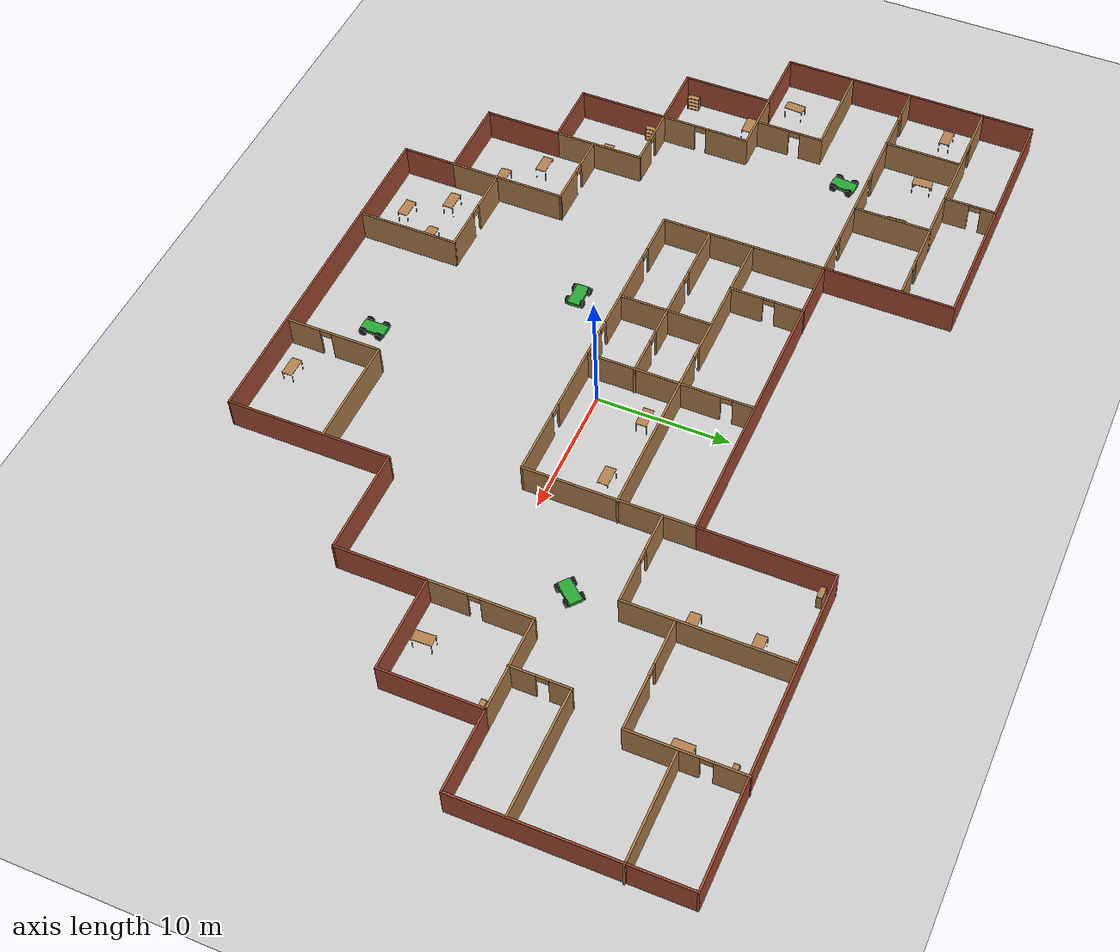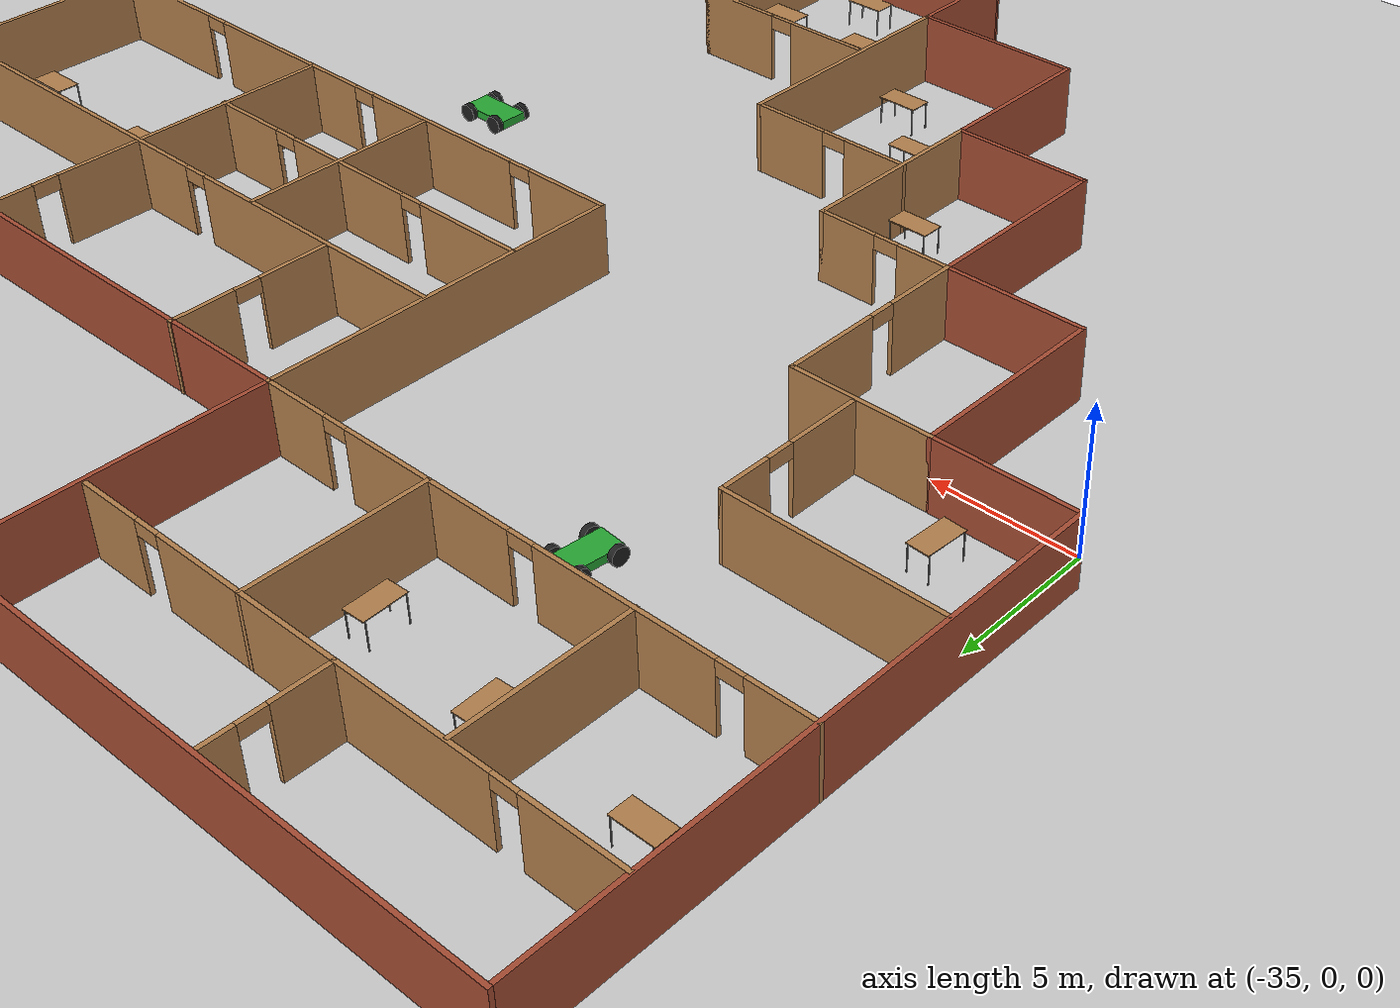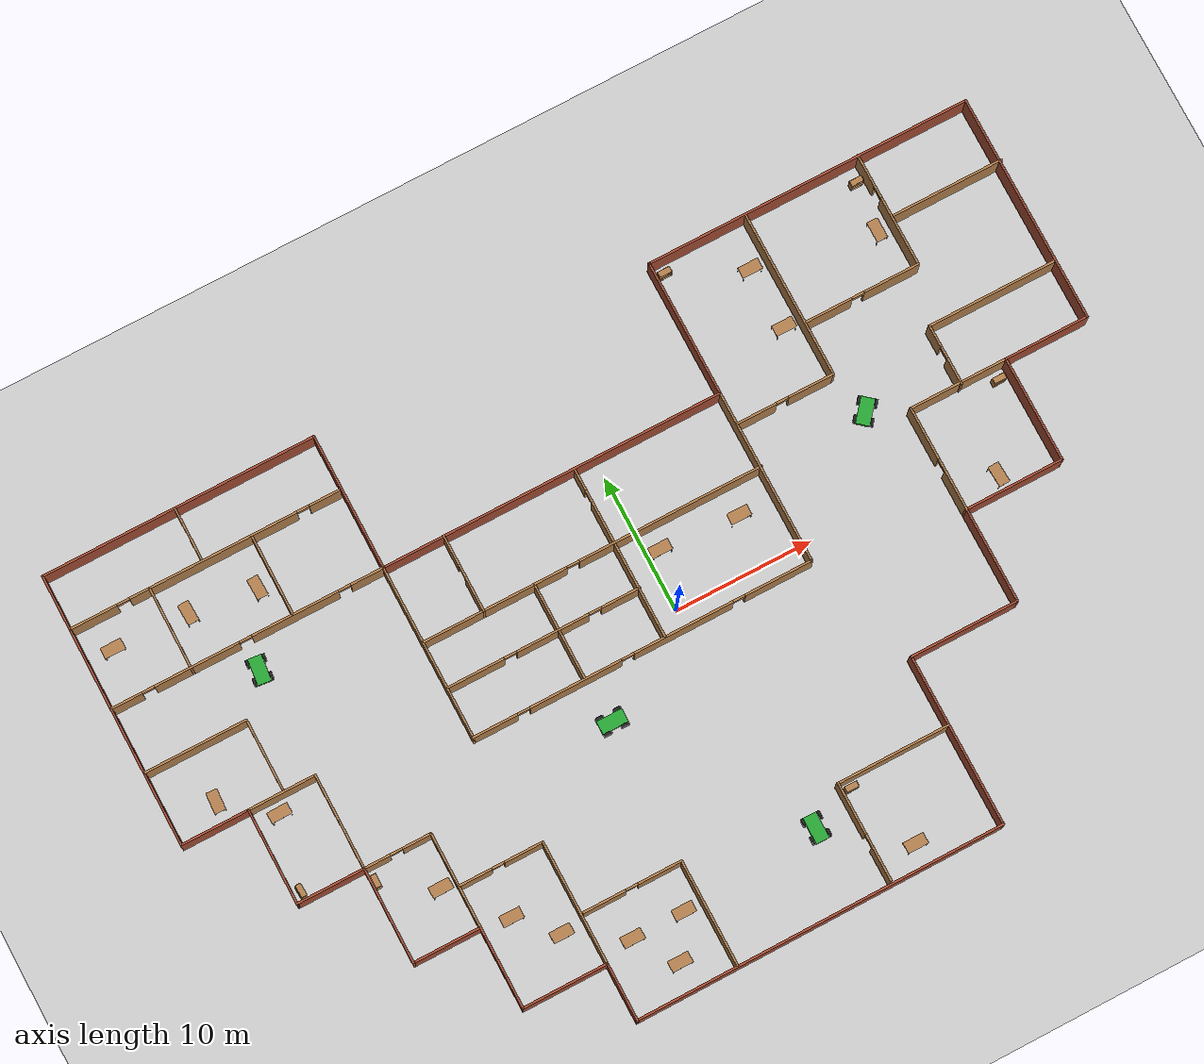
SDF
<sdf version="1.6">
 <world name="default">
  <plugin name="hello" filename="libhello.so"/>
  <light name="sun" type="directional">
   <pose>0 0 10 0 -0 0</pose>
   <diffuse>0.8 0.8 0.8 1</diffuse>
   <specular>0.2 0.2 0.2 1</specular>
   <attenuation>
    <range>1000</range>
    <constant>0.9</constant>
    <linear>0.01</linear>
    <quadratic>0.001</quadratic>
   </attenuation>
   <direction>-0.5 0.1 -0.9</direction>
  </light>
  <model name="ground_plane">
   <static>1</static>
   <link name="link">
    <collision name="collision">
     <geometry><plane><normal>0 0 1</normal><size>100 100</size></plane></geometry>
     <surface><friction><ode><mu>100</mu><mu2>50</mu2></ode></friction></surface>
    </collision>
    <visual name="visual">
     <cast_shadows>0</cast_shadows>
     <geometry><plane><normal>0 0 1</normal><size>100 100</size></plane></geometry>
     <material>
      <script><uri>file://media/materials/scripts/gazebo.material</uri><name>Gazebo/Grey</name></script>
     </material>
    </visual>
   </link>
  </model>
  <gravity>0 0 -9.8</gravity>
  <magnetic_field>6e-06 2.3e-05 -4.2e-05</magnetic_field>
  <atmosphere type="adiabatic"/>
  <physics name="default_physics" default="0" type="ode">
   <max_step_size>0.001</max_step_size>
   <real_time_factor>1</real_time_factor>
   <real_time_update_rate>1000</real_time_update_rate>
  </physics>
  <scene><ambient>0.4 0.4 0.4 1</ambient><background>0.7 0.7 0.7 1</background><shadows>1</shadows></scene>
  <spherical_coordinates>
   <surface_model>EARTH_WGS84</surface_model>
   <latitude_deg>0</latitude_deg>
   <longitude_deg>0</longitude_deg>
   <elevation>0</elevation>
   <heading_deg>0</heading_deg>
  </spherical_coordinates>
  <model name="Untitled">
   <model name="My_building">
    <pose>1.97709 0.760805 -1.16245 0 -0 0</pose>
    <link name="Wall_104">
     <collision name="Wall_104_Collision">
      <geometry><box><size>7.25 0.15 2.5</size></box></geometry>
      <pose>0 0 1.25 0 -0 0</pose>
     </collision>
     <visual name="Wall_104_Visual">
      <pose>0 0 1.25 0 -0 0</pose>
      <geometry><box><size>7.25 0.15 2.5</size></box></geometry>
      <material>
       <script><uri>file://media/materials/scripts/gazebo.material</uri><name>Gazebo/Bricks</name></script>
       <ambient>0.333333 1 1 1</ambient>
      </material>
      <meta><layer>0</layer></meta>
     </visual>
     <pose>24.508 -2.47483 0 0 -0 0</pose>
    </link>
    <link name="Wall_105">
     <collision name="Wall_105_Collision">
      <geometry><box><size>7.75 0.15 2.5</size></box></geometry>
      <pose>0 0 1.25 0 -0 0</pose>
     </collision>
     <visual name="Wall_105_Visual">
      <pose>0 0 1.25 0 -0 0</pose>
      <geometry><box><size>7.75 0.15 2.5</size></box></geometry>
      <material>
       <script><uri>file://media/materials/scripts/gazebo.material</uri><name>Gazebo/Bricks</name></script>
       <ambient>0.333333 1 1 1</ambient>
      </material>
      <meta><layer>0</layer></meta>
     </visual>
     <pose>28.058 1.32517 0 0 -0 1.5708</pose>
    </link>
    <link name="Wall_106">
     <collision name="Wall_106_Collision">
      <geometry><box><size>6.25 0.15 2.5</size></box></geometry>
      <pose>0 0 1.25 0 -0 0</pose>
     </collision>
     <visual name="Wall_106_Visual">
      <pose>0 0 1.25 0 -0 0</pose>
      <geometry><box><size>6.25 0.15 2.5</size></box></geometry>
      <material>
       <script><uri>file://media/materials/scripts/gazebo.material</uri><name>Gazebo/Bricks</name></script>
       <ambient>0.333333 1 1 1</ambient>
      </material>
      <meta><layer>0</layer></meta>
     </visual>
     <pose>31.108 5.12517 0 0 -0 0</pose>
    </link>
    <link name="Wall_107">
     <collision name="Wall_107_Collision">
      <geometry><box><size>16.75 0.15 2.5</size></box></geometry>
      <pose>0 0 1.25 0 -0 0</pose>
     </collision>
     <visual name="Wall_107_Visual">
      <pose>0 0 1.25 0 -0 0</pose>
      <geometry><box><size>16.75 0.15 2.5</size></box></geometry>
      <material>
       <script><uri>file://media/materials/scripts/gazebo.material</uri><name>Gazebo/Bricks</name></script>
       <ambient>0.333333 1 1 1</ambient>
      </material>
      <meta><layer>0</layer></meta>
     </visual>
     <pose>34.158 13.4252 0 0 -0 1.5708</pose>
    </link>
    <link name="Wall_110">
     <collision name="Wall_110_Collision">
      <geometry><box><size>23.9 0.15 2.5</size></box></geometry>
      <pose>0 0 1.25 0 -0 0</pose>
     </collision>
     <visual name="Wall_110_Visual">
      <pose>0 0 1.25 0 -0 0</pose>
      <geometry><box><size>23.9 0.15 2.5</size></box></geometry>
      <material>
       <script><uri>file://media/materials/scripts/gazebo.material</uri><name>Gazebo/Bricks</name></script>
       <ambient>0.333333 1 1 1</ambient>
      </material>
      <meta><layer>0</layer></meta>
     </visual>
     <pose>22.283 21.7252 0 0 -0 0</pose>
    </link>
    <link name="Wall_112">
     <collision name="Wall_112_Collision">
      <geometry><box><size>12.75 0.15 2.5</size></box></geometry>
      <pose>0 0 1.25 0 -0 0</pose>
     </collision>
     <visual name="Wall_112_Visual">
      <pose>0 0 1.25 0 -0 0</pose>
      <geometry><box><size>12.75 0.15 2.5</size></box></geometry>
      <material>
       <script><uri>file://media/materials/scripts/gazebo.material</uri><name>Gazebo/Wood</name></script>
       <ambient>0.435294 0.796078 0.67451 1</ambient>
      </material>
      <meta><layer>0</layer></meta>
     </visual>
     <pose>-14.442 5.57517 0 0 0 -1.5708</pose>
    </link>
    <link name="Wall_115">
     <collision name="Wall_115_Collision">
      <geometry><box><size>12.75 0.15 2.5</size></box></geometry>
      <pose>0 0 1.25 0 -0 0</pose>
     </collision>
     <visual name="Wall_115_Visual">
      <pose>0 0 1.25 0 -0 0</pose>
      <geometry><box><size>12.75 0.15 2.5</size></box></geometry>
      <material>
       <script><uri>file://media/materials/scripts/gazebo.material</uri><name>Gazebo/Wood</name></script>
       <ambient>0.435294 0.796078 0.67451 1</ambient>
      </material>
      <meta><layer>0</layer></meta>
     </visual>
     <pose>10.408 5.57517 0 0 0 -1.5708</pose>
    </link>
    <link name="Wall_120">
     <pose>-2.017 -0.724831 0 0 -0 0</pose>
     <visual name="Wall_120_Visual_0">
      <pose>-10.8536 0 1.25 0 -0 0</pose>
      <geometry><box><size>3.29273 0.15 2.5</size></box></geometry>
      <material>
       <script><uri>file://media/materials/scripts/gazebo.material</uri><name>Gazebo/Wood</name></script>
       <ambient>0.435294 0.796078 0.67451 1</ambient>
      </material>
      <meta><layer>0</layer></meta>
     </visual>
     <collision name="Wall_120_Collision_0">
      <geometry><box><size>3.29273 0.15 2.5</size></box></geometry>
      <pose>-10.8536 0 1.25 0 -0 0</pose>
     </collision>
     <visual name="Wall_120_Visual_1">
      <pose>-4.93656 0 1.25 0 -0 0</pose>
      <geometry><box><size>6.74143 0.15 2.5</size></box></geometry>
      <material>
       <script><uri>file://media/materials/scripts/gazebo.material</uri><name>Gazebo/Wood</name></script>
       <ambient>0.435294 0.796078 0.67451 1</ambient>
      </material>
      <meta><layer>0</layer></meta>
     </visual>
     <collision name="Wall_120_Collision_1">
      <geometry><box><size>6.74143 0.15 2.5</size></box></geometry>
      <pose>-4.93656 0 1.25 0 -0 0</pose>
     </collision>
     <visual name="Wall_120_Visual_2">
      <pose>2.97536 0 1.25 0 -0 0</pose>
      <geometry><box><size>7.28242 0.15 2.5</size></box></geometry>
      <material>
       <script><uri>file://media/materials/scripts/gazebo.material</uri><name>Gazebo/Wood</name></script>
       <ambient>0.435294 0.796078 0.67451 1</ambient>
      </material>
      <meta><layer>0</layer></meta>
     </visual>
     <collision name="Wall_120_Collision_2">
      <geometry><box><size>7.28242 0.15 2.5</size></box></geometry>
      <pose>2.97536 0 1.25 0 -0 0</pose>
     </collision>
     <visual name="Wall_120_Visual_3">
      <pose>10.0083 0 1.25 0 -0 0</pose>
      <geometry><box><size>4.98343 0.15 2.5</size></box></geometry>
      <material>
       <script><uri>file://media/materials/scripts/gazebo.material</uri><name>Gazebo/Wood</name></script>
       <ambient>0.435294 0.796078 0.67451 1</ambient>
      </material>
      <meta><layer>0</layer></meta>
     </visual>
     <collision name="Wall_120_Collision_3">
      <geometry><box><size>4.98343 0.15 2.5</size></box></geometry>
      <pose>10.0083 0 1.25 0 -0 0</pose>
     </collision>
     <visual name="Wall_120_Visual_4">
      <pose>-8.75727 0 2.25 0 -0 0</pose>
      <geometry><box><size>0.9 0.15 0.5</size></box></geometry>
      <material>
       <script><uri>file://media/materials/scripts/gazebo.material</uri><name>Gazebo/Wood</name></script>
       <ambient>0.435294 0.796078 0.67451 1</ambient>
      </material>
      <meta><layer>0</layer></meta>
     </visual>
     <collision name="Wall_120_Collision_4">
      <geometry><box><size>0.9 0.15 0.5</size></box></geometry>
      <pose>-8.75727 0 2.25 0 -0 0</pose>
     </collision>
     <visual name="Wall_120_Visual_5">
      <pose>-1.11584 0 2.25 0 -0 0</pose>
      <geometry><box><size>0.9 0.15 0.5</size></box></geometry>
      <material>
       <script><uri>file://media/materials/scripts/gazebo.material</uri><name>Gazebo/Wood</name></script>
       <ambient>0.435294 0.796078 0.67451 1</ambient>
      </material>
      <meta><layer>0</layer></meta>
     </visual>
     <collision name="Wall_120_Collision_5">
      <geometry><box><size>0.9 0.15 0.5</size></box></geometry>
      <pose>-1.11584 0 2.25 0 -0 0</pose>
     </collision>
     <visual name="Wall_120_Visual_6">
      <pose>7.06657 0 2.25 0 -0 0</pose>
      <geometry><box><size>0.9 0.15 0.5</size></box></geometry>
      <material>
       <script><uri>file://media/materials/scripts/gazebo.material</uri><name>Gazebo/Wood</name></script>
       <ambient>0.435294 0.796078 0.67451 1</ambient>
      </material>
      <meta><layer>0</layer></meta>
     </visual>
     <collision name="Wall_120_Collision_6">
      <geometry><box><size>0.9 0.15 0.5</size></box></geometry>
      <pose>7.06657 0 2.25 0 -0 0</pose>
     </collision>
    </link>
    <link name="Wall_122">
     <pose>-1.93956 6.30992 0 0 -0 0</pose>
     <visual name="Wall_122_Visual_0">
      <pose>-7.21918 0 1.25 0 -0 0</pose>
      <geometry><box><size>10.5616 0.15 2.5</size></box></geometry>
      <material>
       <script><uri>file://media/materials/scripts/gazebo.material</uri><name>Gazebo/Wood</name></script>
       <ambient>0.435294 0.796078 0.67451 1</ambient>
      </material>
      <meta><layer>0</layer></meta>
     </visual>
     <collision name="Wall_122_Collision_0">
      <geometry><box><size>10.5616 0.15 2.5</size></box></geometry>
      <pose>-7.21918 0 1.25 0 -0 0</pose>
     </collision>
     <visual name="Wall_122_Visual_1">
      <pose>5.73082 0 1.25 0 -0 0</pose>
      <geometry><box><size>13.5384 0.15 2.5</size></box></geometry>
      <material>
       <script><uri>file://media/materials/scripts/gazebo.material</uri><name>Gazebo/Wood</name></script>
       <ambient>0.435294 0.796078 0.67451 1</ambient>
      </material>
      <meta><layer>0</layer></meta>
     </visual>
     <collision name="Wall_122_Collision_1">
      <geometry><box><size>13.5384 0.15 2.5</size></box></geometry>
      <pose>5.73082 0 1.25 0 -0 0</pose>
     </collision>
     <visual name="Wall_122_Visual_2">
      <pose>-1.48836 0 2.25 0 -0 0</pose>
      <geometry><box><size>0.9 0.15 0.5</size></box></geometry>
      <material>
       <script><uri>file://media/materials/scripts/gazebo.material</uri><name>Gazebo/Wood</name></script>
       <ambient>0.435294 0.796078 0.67451 1</ambient>
      </material>
      <meta><layer>0</layer></meta>
     </visual>
     <collision name="Wall_122_Collision_2">
      <geometry><box><size>0.9 0.15 0.5</size></box></geometry>
      <pose>-1.48836 0 2.25 0 -0 0</pose>
     </collision>
    </link>
    <link name="Wall_124">
     <collision name="Wall_124_Collision">
      <geometry><box><size>7 0.15 2.5</size></box></geometry>
      <pose>0 0 1.25 0 -0 0</pose>
     </collision>
     <visual name="Wall_124_Visual">
      <pose>0 0 1.25 0 -0 0</pose>
      <geometry><box><size>7 0.15 2.5</size></box></geometry>
      <material>
       <script><uri>file://media/materials/scripts/gazebo.material</uri><name>Gazebo/Wood</name></script>
       <ambient>0.435294 0.796078 0.67451 1</ambient>
      </material>
      <meta><layer>0</layer></meta>
     </visual>
     <pose>-0.391735 2.74657 0 0 0 -1.5708</pose>
    </link>
    <link name="Wall_126">
     <collision name="Wall_126_Collision">
      <geometry><box><size>7 0.15 2.5</size></box></geometry>
      <pose>0 0 1.25 0 -0 0</pose>
     </collision>
     <visual name="Wall_126_Visual">
      <pose>0 0 1.25 0 -0 0</pose>
      <geometry><box><size>7 0.15 2.5</size></box></geometry>
      <material>
       <script><uri>file://media/materials/scripts/gazebo.material</uri><name>Gazebo/Wood</name></script>
       <ambient>0.435294 0.796078 0.67451 1</ambient>
      </material>
      <meta><layer>0</layer></meta>
     </visual>
     <pose>-6.27139 2.81575 0 0 0 -1.5708</pose>
    </link>
    <link name="Wall_128">
     <pose>-7.38373 2.92047 0 0 -0 0</pose>
     <visual name="Wall_128_Visual_0">
      <pose>-5.00941 0 1.25 0 -0 0</pose>
      <geometry><box><size>4.23118 0.15 2.5</size></box></geometry>
      <material>
       <script><uri>file://media/materials/scripts/gazebo.material</uri><name>Gazebo/Wood</name></script>
       <ambient>0.435294 0.796078 0.67451 1</ambient>
      </material>
      <meta><layer>0</layer></meta>
     </visual>
     <collision name="Wall_128_Collision_0">
      <geometry><box><size>4.23118 0.15 2.5</size></box></geometry>
      <pose>-5.00941 0 1.25 0 -0 0</pose>
     </collision>
     <visual name="Wall_128_Visual_1">
      <pose>0.666855 0 1.25 0 -0 0</pose>
      <geometry><box><size>5.32134 0.15 2.5</size></box></geometry>
      <material>
       <script><uri>file://media/materials/scripts/gazebo.material</uri><name>Gazebo/Wood</name></script>
       <ambient>0.435294 0.796078 0.67451 1</ambient>
      </material>
      <meta><layer>0</layer></meta>
     </visual>
     <collision name="Wall_128_Collision_1">
      <geometry><box><size>5.32134 0.15 2.5</size></box></geometry>
      <pose>0.666855 0 1.25 0 -0 0</pose>
     </collision>
     <visual name="Wall_128_Visual_2">
      <pose>5.67626 0 1.25 0 -0 0</pose>
      <geometry><box><size>2.89748 0.15 2.5</size></box></geometry>
      <material>
       <script><uri>file://media/materials/scripts/gazebo.material</uri><name>Gazebo/Wood</name></script>
       <ambient>0.435294 0.796078 0.67451 1</ambient>
      </material>
      <meta><layer>0</layer></meta>
     </visual>
     <collision name="Wall_128_Collision_2">
      <geometry><box><size>2.89748 0.15 2.5</size></box></geometry>
      <pose>5.67626 0 1.25 0 -0 0</pose>
     </collision>
     <visual name="Wall_128_Visual_3">
      <pose>-2.44382 0 2.25 0 -0 0</pose>
      <geometry><box><size>0.9 0.15 0.5</size></box></geometry>
      <material>
       <script><uri>file://media/materials/scripts/gazebo.material</uri><name>Gazebo/Wood</name></script>
       <ambient>0.435294 0.796078 0.67451 1</ambient>
      </material>
      <meta><layer>0</layer></meta>
     </visual>
     <collision name="Wall_128_Collision_3">
      <geometry><box><size>0.9 0.15 0.5</size></box></geometry>
      <pose>-2.44382 0 2.25 0 -0 0</pose>
     </collision>
     <visual name="Wall_128_Visual_4">
      <pose>3.77752 0 2.25 0 -0 0</pose>
      <geometry><box><size>0.9 0.15 0.5</size></box></geometry>
      <material>
       <script><uri>file://media/materials/scripts/gazebo.material</uri><name>Gazebo/Wood</name></script>
       <ambient>0.435294 0.796078 0.67451 1</ambient>
      </material>
      <meta><layer>0</layer></meta>
     </visual>
     <collision name="Wall_128_Collision_4">
      <geometry><box><size>0.9 0.15 0.5</size></box></geometry>
      <pose>3.77752 0 2.25 0 -0 0</pose>
     </collision>
    </link>
    <link name="Wall_130">
     <pose>-0.391735 9.12326 0 0 -0 1.5708</pose>
     <visual name="Wall_130_Visual_0">
      <pose>-1.25641 0 1.25 0 -0 0</pose>
      <geometry><box><size>2.98718 0.15 2.5</size></box></geometry>
      <material>
       <script><uri>file://media/materials/scripts/gazebo.material</uri><name>Gazebo/Wood</name></script>
       <ambient>0.435294 0.796078 0.67451 1</ambient>
      </material>
      <meta><layer>0</layer></meta>
     </visual>
     <collision name="Wall_130_Collision_0">
      <geometry><box><size>2.98718 0.15 2.5</size></box></geometry>
      <pose>-1.25641 0 1.25 0 -0 0</pose>
     </collision>
     <visual name="Wall_130_Visual_1">
      <pose>1.94359 0 1.25 0 -0 0</pose>
      <geometry><box><size>1.61282 0.15 2.5</size></box></geometry>
      <material>
       <script><uri>file://media/materials/scripts/gazebo.material</uri><name>Gazebo/Wood</name></script>
       <ambient>0.435294 0.796078 0.67451 1</ambient>
      </material>
      <meta><layer>0</layer></meta>
     </visual>
     <collision name="Wall_130_Collision_1">
      <geometry><box><size>1.61282 0.15 2.5</size></box></geometry>
      <pose>1.94359 0 1.25 0 -0 0</pose>
     </collision>
     <visual name="Wall_130_Visual_2">
      <pose>0.687178 0 2.25 0 -0 0</pose>
      <geometry><box><size>0.9 0.15 0.5</size></box></geometry>
      <material>
       <script><uri>file://media/materials/scripts/gazebo.material</uri><name>Gazebo/Wood</name></script>
       <ambient>0.435294 0.796078 0.67451 1</ambient>
      </material>
      <meta><layer>0</layer></meta>
     </visual>
     <collision name="Wall_130_Collision_2">
      <geometry><box><size>0.9 0.15 0.5</size></box></geometry>
      <pose>0.687178 0 2.25 0 -0 0</pose>
     </collision>
    </link>
    <link name="Wall_134">
     <pose>-9.99647 9.10326 0 0 0 -1.5708</pose>
     <visual name="Wall_134_Visual_0">
      <pose>-1.74931 0 1.25 0 -0 0</pose>
      <geometry><box><size>2.25138 0.15 2.5</size></box></geometry>
      <material>
       <script><uri>file://media/materials/scripts/gazebo.material</uri><name>Gazebo/Wood</name></script>
       <ambient>0.435294 0.796078 0.67451 1</ambient>
      </material>
      <meta><layer>0</layer></meta>
     </visual>
     <collision name="Wall_134_Collision_0">
      <geometry><box><size>2.25138 0.15 2.5</size></box></geometry>
      <pose>-1.74931 0 1.25 0 -0 0</pose>
     </collision>
     <visual name="Wall_134_Visual_1">
      <pose>1.57569 0 1.25 0 -0 0</pose>
      <geometry><box><size>2.59862 0.15 2.5</size></box></geometry>
      <material>
       <script><uri>file://media/materials/scripts/gazebo.material</uri><name>Gazebo/Wood</name></script>
       <ambient>0.435294 0.796078 0.67451 1</ambient>
      </material>
      <meta><layer>0</layer></meta>
     </visual>
     <collision name="Wall_134_Collision_1">
      <geometry><box><size>2.59862 0.15 2.5</size></box></geometry>
      <pose>1.57569 0 1.25 0 -0 0</pose>
     </collision>
     <visual name="Wall_134_Visual_2">
      <pose>-0.17362 0 2.25 0 -0 0</pose>
      <geometry><box><size>0.9 0.15 0.5</size></box></geometry>
      <material>
       <script><uri>file://media/materials/scripts/gazebo.material</uri><name>Gazebo/Wood</name></script>
       <ambient>0.435294 0.796078 0.67451 1</ambient>
      </material>
      <meta><layer>0</layer></meta>
     </visual>
     <collision name="Wall_134_Collision_2">
      <geometry><box><size>0.9 0.15 0.5</size></box></geometry>
      <pose>-0.17362 0 2.25 0 -0 0</pose>
     </collision>
    </link>
    <link name="Wall_137">
     <collision name="Wall_137_Collision">
      <geometry><box><size>5 0.15 2.5</size></box></geometry>
      <pose>0 0 1.25 0 -0 0</pose>
     </collision>
     <visual name="Wall_137_Visual">
      <pose>0 0 1.25 0 -0 0</pose>
      <geometry><box><size>5 0.15 2.5</size></box></geometry>
      <material>
       <script><uri>file://media/materials/scripts/gazebo.material</uri><name>Gazebo/Wood</name></script>
       <ambient>1 1 0 1</ambient>
      </material>
      <meta><layer>0</layer></meta>
     </visual>
     <pose>-27.017 1.87517 0 0 -0 0</pose>
    </link>
    <link name="Wall_139">
     <pose>-24.592 -1.54983 0 0 0 -1.5708</pose>
     <visual name="Wall_139_Visual_0">
      <pose>-1.78358 0 1.25 0 -0 0</pose>
      <geometry><box><size>3.43283 0.15 2.5</size></box></geometry>
      <material>
       <script><uri>file://media/materials/scripts/gazebo.material</uri><name>Gazebo/Wood</name></script>
       <ambient>1 1 0 1</ambient>
      </material>
      <meta><layer>0</layer></meta>
     </visual>
     <collision name="Wall_139_Collision_0">
      <geometry><box><size>3.43283 0.15 2.5</size></box></geometry>
      <pose>-1.78358 0 1.25 0 -0 0</pose>
     </collision>
     <visual name="Wall_139_Visual_1">
      <pose>2.16642 0 1.25 0 -0 0</pose>
      <geometry><box><size>2.66717 0.15 2.5</size></box></geometry>
      <material>
       <script><uri>file://media/materials/scripts/gazebo.material</uri><name>Gazebo/Wood</name></script>
       <ambient>1 1 0 1</ambient>
      </material>
      <meta><layer>0</layer></meta>
     </visual>
     <collision name="Wall_139_Collision_1">
      <geometry><box><size>2.66717 0.15 2.5</size></box></geometry>
      <pose>2.16642 0 1.25 0 -0 0</pose>
     </collision>
     <visual name="Wall_139_Visual_2">
      <pose>0.382831 0 2.25 0 -0 0</pose>
      <geometry><box><size>0.9 0.15 0.5</size></box></geometry>
      <material>
       <script><uri>file://media/materials/scripts/gazebo.material</uri><name>Gazebo/Wood</name></script>
       <ambient>1 1 0 1</ambient>
      </material>
      <meta><layer>0</layer></meta>
     </visual>
     <collision name="Wall_139_Collision_2">
      <geometry><box><size>0.9 0.15 0.5</size></box></geometry>
      <pose>0.382831 0 2.25 0 -0 0</pose>
     </collision>
    </link>
    <link name="Wall_143">
     <pose>-22.167 -4.97483 0 0 -0 0</pose>
     <visual name="Wall_143_Visual_0">
      <pose>-1.52696 0 1.25 0 -0 0</pose>
      <geometry><box><size>1.94607 0.15 2.5</size></box></geometry>
      <material>
       <script><uri>file://media/materials/scripts/gazebo.material</uri><name>Gazebo/Wood</name></script>
       <ambient>1 1 0 1</ambient>
      </material>
      <meta><layer>0</layer></meta>
     </visual>
     <collision name="Wall_143_Collision_0">
      <geometry><box><size>1.94607 0.15 2.5</size></box></geometry>
      <pose>-1.52696 0 1.25 0 -0 0</pose>
     </collision>
     <visual name="Wall_143_Visual_1">
      <pose>1.42304 0 1.25 0 -0 0</pose>
      <geometry><box><size>2.15393 0.15 2.5</size></box></geometry>
      <material>
       <script><uri>file://media/materials/scripts/gazebo.material</uri><name>Gazebo/Wood</name></script>
       <ambient>1 1 0 1</ambient>
      </material>
      <meta><layer>0</layer></meta>
     </visual>
     <collision name="Wall_143_Collision_1">
      <geometry><box><size>2.15393 0.15 2.5</size></box></geometry>
      <pose>1.42304 0 1.25 0 -0 0</pose>
     </collision>
     <visual name="Wall_143_Visual_2">
      <pose>-0.10393 0 2.25 0 -0 0</pose>
      <geometry><box><size>0.9 0.15 0.5</size></box></geometry>
      <material>
       <script><uri>file://media/materials/scripts/gazebo.material</uri><name>Gazebo/Wood</name></script>
       <ambient>1 1 0 1</ambient>
      </material>
      <meta><layer>0</layer></meta>
     </visual>
     <collision name="Wall_143_Collision_2">
      <geometry><box><size>0.9 0.15 0.5</size></box></geometry>
      <pose>-0.10393 0 2.25 0 -0 0</pose>
     </collision>
    </link>
    <link name="Wall_145">
     <collision name="Wall_145_Collision">
      <geometry><box><size>7 0.15 2.5</size></box></geometry>
      <pose>0 0 1.25 0 -0 0</pose>
     </collision>
     <visual name="Wall_145_Visual">
      <pose>0 0 1.25 0 -0 0</pose>
      <geometry><box><size>7 0.15 2.5</size></box></geometry>
      <material>
       <script><uri>file://media/materials/scripts/gazebo.material</uri><name>Gazebo/Wood</name></script>
       <ambient>1 1 0 1</ambient>
      </material>
      <meta><layer>0</layer></meta>
     </visual>
     <pose>-19.742 -8.39983 0 0 0 -1.5708</pose>
    </link>
    <link name="Wall_151">
     <collision name="Wall_151_Collision">
      <geometry><box><size>5 0.15 2.5</size></box></geometry>
      <pose>0 0 1.25 0 -0 0</pose>
     </collision>
     <visual name="Wall_151_Visual">
      <pose>0 0 1.25 0 -0 0</pose>
      <geometry><box><size>5 0.15 2.5</size></box></geometry>
      <material>
       <script><uri>file://media/materials/scripts/gazebo.material</uri><name>Gazebo/Bricks</name></script>
       <ambient>0.333333 1 1 1</ambient>
      </material>
      <meta><layer>0</layer></meta>
     </visual>
     <pose>-22.167 -11.8248 0 0 -0 0</pose>
    </link>
    <link name="Wall_152">
     <collision name="Wall_152_Collision">
      <geometry><box><size>6 0.15 2.5</size></box></geometry>
      <pose>0 0 1.25 0 -0 0</pose>
     </collision>
     <visual name="Wall_152_Visual">
      <pose>0 0 1.25 0 -0 0</pose>
      <geometry><box><size>6 0.15 2.5</size></box></geometry>
      <material>
       <script><uri>file://media/materials/scripts/gazebo.material</uri><name>Gazebo/Bricks</name></script>
       <ambient>0.333333 1 1 1</ambient>
      </material>
      <meta><layer>0</layer></meta>
     </visual>
     <pose>-19.742 -14.7498 0 0 0 -1.5708</pose>
    </link>
    <link name="Wall_153">
     <collision name="Wall_153_Collision">
      <geometry><box><size>6.25 0.15 2.5</size></box></geometry>
      <pose>0 0 1.25 0 -0 0</pose>
     </collision>
     <visual name="Wall_153_Visual">
      <pose>0 0 1.25 0 -0 0</pose>
      <geometry><box><size>6.25 0.15 2.5</size></box></geometry>
      <material>
       <script><uri>file://media/materials/scripts/gazebo.material</uri><name>Gazebo/Bricks</name></script>
       <ambient>0.333333 1 1 1</ambient>
      </material>
      <meta><layer>0</layer></meta>
     </visual>
     <pose>-16.692 -17.6748 0 0 -0 0</pose>
    </link>
    <link name="Wall_154">
     <collision name="Wall_154_Collision">
      <geometry><box><size>4.25 0.15 2.5</size></box></geometry>
      <pose>0 0 1.25 0 -0 0</pose>
     </collision>
     <visual name="Wall_154_Visual">
      <pose>0 0 1.25 0 -0 0</pose>
      <geometry><box><size>4.25 0.15 2.5</size></box></geometry>
      <material>
       <script><uri>file://media/materials/scripts/gazebo.material</uri><name>Gazebo/Bricks</name></script>
       <ambient>0.333333 1 1 1</ambient>
      </material>
      <meta><layer>0</layer></meta>
     </visual>
     <pose>-13.642 -19.7248 0 0 0 -1.5708</pose>
    </link>
    <link name="Wall_175">
     <collision name="Wall_175_Collision">
      <geometry><box><size>9 0.15 2.5</size></box></geometry>
      <pose>0 0 1.25 0 -0 0</pose>
     </collision>
     <visual name="Wall_175_Visual">
      <pose>0 0 1.25 0 -0 0</pose>
      <geometry><box><size>9 0.15 2.5</size></box></geometry>
      <material>
       <script><uri>file://media/materials/scripts/gazebo.material</uri><name>Gazebo/Wood</name></script>
       <ambient>1 1 0 1</ambient>
      </material>
      <meta><layer>0</layer></meta>
     </visual>
     <pose>-13.642 -13.2498 0 0 -0 1.5708</pose>
    </link>
    <link name="Wall_176">
     <pose>-16.692 -8.82483 0 0 -0 3.14159</pose>
     <visual name="Wall_176_Visual_0">
      <pose>-1.68139 0 1.25 0 -0 0</pose>
      <geometry><box><size>2.88721 0.15 2.5</size></box></geometry>
      <material>
       <script><uri>file://media/materials/scripts/gazebo.material</uri><name>Gazebo/Wood</name></script>
       <ambient>1 1 0 1</ambient>
      </material>
      <meta><layer>0</layer></meta>
     </visual>
     <collision name="Wall_176_Collision_0">
      <geometry><box><size>2.88721 0.15 2.5</size></box></geometry>
      <pose>-1.68139 0 1.25 0 -0 0</pose>
     </collision>
     <visual name="Wall_176_Visual_1">
      <pose>1.89361 0 1.25 0 -0 0</pose>
      <geometry><box><size>2.46279 0.15 2.5</size></box></geometry>
      <material>
       <script><uri>file://media/materials/scripts/gazebo.material</uri><name>Gazebo/Wood</name></script>
       <ambient>1 1 0 1</ambient>
      </material>
      <meta><layer>0</layer></meta>
     </visual>
     <collision name="Wall_176_Collision_1">
      <geometry><box><size>2.46279 0.15 2.5</size></box></geometry>
      <pose>1.89361 0 1.25 0 -0 0</pose>
     </collision>
     <visual name="Wall_176_Visual_2">
      <pose>0.212214 0 2.25 0 -0 0</pose>
      <geometry><box><size>0.9 0.15 0.5</size></box></geometry>
      <material>
       <script><uri>file://media/materials/scripts/gazebo.material</uri><name>Gazebo/Wood</name></script>
       <ambient>1 1 0 1</ambient>
      </material>
      <meta><layer>0</layer></meta>
     </visual>
     <collision name="Wall_176_Collision_2">
      <geometry><box><size>0.9 0.15 0.5</size></box></geometry>
      <pose>0.212214 0 2.25 0 -0 0</pose>
     </collision>
    </link>
    <link name="Wall_183">
     <collision name="Wall_183_Collision">
      <geometry><box><size>26.9002 0.15 2.5</size></box></geometry>
      <pose>0 0 1.25 0 -0 0</pose>
     </collision>
     <visual name="Wall_183_Visual">
      <pose>0 0 1.25 0 -0 0</pose>
      <geometry><box><size>26.9002 0.15 2.5</size></box></geometry>
      <material>
       <script><uri>file://media/materials/scripts/gazebo.material</uri><name>Gazebo/Bricks</name></script>
       <ambient>0.333333 1 1 1</ambient>
      </material>
      <meta><layer>0</layer></meta>
     </visual>
     <pose>-0.267003 -21.7248 0 0 -0 0.003738</pose>
    </link>
    <link name="Wall_185">
     <pose>-9.87539 -14.0695 0 0 -0 0</pose>
     <visual name="Wall_185_Visual_0">
      <pose>-2.06665 0 1.25 0 -0 0</pose>
      <geometry><box><size>3.1167 0.15 2.5</size></box></geometry>
      <material>
       <script><uri>file://media/materials/scripts/gazebo.material</uri><name>Gazebo/Wood</name></script>
       <ambient>0.760784 0.662745 0.627451 1</ambient>
      </material>
      <meta><layer>0</layer></meta>
     </visual>
     <collision name="Wall_185_Collision_0">
      <geometry><box><size>3.1167 0.15 2.5</size></box></geometry>
      <pose>-2.06665 0 1.25 0 -0 0</pose>
     </collision>
     <visual name="Wall_185_Visual_1">
      <pose>2.00835 0 1.25 0 -0 0</pose>
      <geometry><box><size>3.2333 0.15 2.5</size></box></geometry>
      <material>
       <script><uri>file://media/materials/scripts/gazebo.material</uri><name>Gazebo/Wood</name></script>
       <ambient>0.760784 0.662745 0.627451 1</ambient>
      </material>
      <meta><layer>0</layer></meta>
     </visual>
     <collision name="Wall_185_Collision_1">
      <geometry><box><size>3.2333 0.15 2.5</size></box></geometry>
      <pose>2.00835 0 1.25 0 -0 0</pose>
     </collision>
     <visual name="Wall_185_Visual_2">
      <pose>-0.058299 0 2.25 0 -0 0</pose>
      <geometry><box><size>0.9 0.15 0.5</size></box></geometry>
      <material>
       <script><uri>file://media/materials/scripts/gazebo.material</uri><name>Gazebo/Wood</name></script>
       <ambient>0.760784 0.662745 0.627451 1</ambient>
      </material>
      <meta><layer>0</layer></meta>
     </visual>
     <collision name="Wall_185_Collision_2">
      <geometry><box><size>0.9 0.15 0.5</size></box></geometry>
      <pose>-0.058299 0 2.25 0 -0 0</pose>
     </collision>
    </link>
    <link name="Wall_186">
     <collision name="Wall_186_Collision">
      <geometry><box><size>7.75 0.15 2.5</size></box></geometry>
      <pose>0 0 1.25 0 -0 0</pose>
     </collision>
     <visual name="Wall_186_Visual">
      <pose>0 0 1.25 0 -0 0</pose>
      <geometry><box><size>7.75 0.15 2.5</size></box></geometry>
      <material>
       <script><uri>file://media/materials/scripts/gazebo.material</uri><name>Gazebo/Wood</name></script>
       <ambient>0.760784 0.662745 0.627451 1</ambient>
      </material>
      <meta><layer>0</layer></meta>
     </visual>
     <pose>-6.32539 -17.8695 0 0 0 -1.5708</pose>
    </link>
    <link name="Wall_190">
     <pose>20.958 1.32517 0 0 -0 1.5708</pose>
     <visual name="Wall_190_Visual_0">
      <pose>-2.39061 0 1.25 0 -0 0</pose>
      <geometry><box><size>2.96878 0.15 2.5</size></box></geometry>
      <material>
       <script><uri>file://media/materials/scripts/gazebo.material</uri><name>Gazebo/Wood</name></script>
       <ambient>1 1 0 1</ambient>
      </material>
      <meta><layer>0</layer></meta>
     </visual>
     <collision name="Wall_190_Collision_0">
      <geometry><box><size>2.96878 0.15 2.5</size></box></geometry>
      <pose>-2.39061 0 1.25 0 -0 0</pose>
     </collision>
     <visual name="Wall_190_Visual_1">
      <pose>1.93439 0 1.25 0 -0 0</pose>
      <geometry><box><size>3.88122 0.15 2.5</size></box></geometry>
      <material>
       <script><uri>file://media/materials/scripts/gazebo.material</uri><name>Gazebo/Wood</name></script>
       <ambient>1 1 0 1</ambient>
      </material>
      <meta><layer>0</layer></meta>
     </visual>
     <collision name="Wall_190_Collision_1">
      <geometry><box><size>3.88122 0.15 2.5</size></box></geometry>
      <pose>1.93439 0 1.25 0 -0 0</pose>
     </collision>
     <visual name="Wall_190_Visual_2">
      <pose>-0.456219 0 2.25 0 -0 0</pose>
      <geometry><box><size>0.9 0.15 0.5</size></box></geometry>
      <material>
       <script><uri>file://media/materials/scripts/gazebo.material</uri><name>Gazebo/Wood</name></script>
       <ambient>1 1 0 1</ambient>
      </material>
      <meta><layer>0</layer></meta>
     </visual>
     <collision name="Wall_190_Collision_2">
      <geometry><box><size>0.9 0.15 0.5</size></box></geometry>
      <pose>-0.456219 0 2.25 0 -0 0</pose>
     </collision>
    </link>
    <link name="Wall_192">
     <collision name="Wall_192_Collision">
      <geometry><box><size>7.25 0.15 2.5</size></box></geometry>
      <pose>0 0 1.25 0 -0 0</pose>
     </collision>
     <visual name="Wall_192_Visual">
      <pose>0 0 1.25 0 -0 0</pose>
      <geometry><box><size>7.25 0.15 2.5</size></box></geometry>
      <material>
       <script><uri>file://media/materials/scripts/gazebo.material</uri><name>Gazebo/Wood</name></script>
       <ambient>1 1 0 1</ambient>
      </material>
      <meta><layer>0</layer></meta>
     </visual>
     <pose>24.508 5.12517 0 0 -0 0</pose>
    </link>
    <link name="Wall_196">
     <pose>4.97312 -17.9193 0 0 -0 1.5708</pose>
     <visual name="Wall_196_Visual_0">
      <pose>-2.36842 0 1.25 0 -0 0</pose>
      <geometry><box><size>2.51317 0.15 2.5</size></box></geometry>
      <material>
       <script><uri>file://media/materials/scripts/gazebo.material</uri><name>Gazebo/Wood</name></script>
       <ambient>0.760784 0.662745 0.627451 1</ambient>
      </material>
      <meta><layer>0</layer></meta>
     </visual>
     <collision name="Wall_196_Collision_0">
      <geometry><box><size>2.51317 0.15 2.5</size></box></geometry>
      <pose>-2.36842 0 1.25 0 -0 0</pose>
     </collision>
     <visual name="Wall_196_Visual_1">
      <pose>1.70659 0 1.25 0 -0 0</pose>
      <geometry><box><size>3.83683 0.15 2.5</size></box></geometry>
      <material>
       <script><uri>file://media/materials/scripts/gazebo.material</uri><name>Gazebo/Wood</name></script>
       <ambient>0.760784 0.662745 0.627451 1</ambient>
      </material>
      <meta><layer>0</layer></meta>
     </visual>
     <collision name="Wall_196_Collision_1">
      <geometry><box><size>3.83683 0.15 2.5</size></box></geometry>
      <pose>1.70659 0 1.25 0 -0 0</pose>
     </collision>
     <visual name="Wall_196_Visual_2">
      <pose>-0.661831 0 2.25 0 -0 0</pose>
      <geometry><box><size>0.9 0.15 0.5</size></box></geometry>
      <material>
       <script><uri>file://media/materials/scripts/gazebo.material</uri><name>Gazebo/Wood</name></script>
       <ambient>0.760784 0.662745 0.627451 1</ambient>
      </material>
      <meta><layer>0</layer></meta>
     </visual>
     <collision name="Wall_196_Collision_2">
      <geometry><box><size>0.9 0.15 0.5</size></box></geometry>
      <pose>-0.661831 0 2.25 0 -0 0</pose>
     </collision>
    </link>
    <link name="Wall_197">
     <collision name="Wall_197_Collision">
      <geometry><box><size>8.25 0.15 2.5</size></box></geometry>
      <pose>0 0 1.25 0 -0 0</pose>
     </collision>
     <visual name="Wall_197_Visual">
      <pose>0 0 1.25 0 -0 0</pose>
      <geometry><box><size>8.25 0.15 2.5</size></box></geometry>
      <material>
       <script><uri>file://media/materials/scripts/gazebo.material</uri><name>Gazebo/Wood</name></script>
       <ambient>0.760784 0.662745 0.627451 1</ambient>
      </material>
      <meta><layer>0</layer></meta>
     </visual>
     <pose>9.02312 -14.3693 0 0 -0 0</pose>
    </link>
    <link name="Wall_200">
     <collision name="Wall_200_Collision">
      <geometry><box><size>12.5 0.15 2.5</size></box></geometry>
      <pose>0 0 1.25 0 -0 0</pose>
     </collision>
     <visual name="Wall_200_Visual">
      <pose>0 0 1.25 0 -0 0</pose>
      <geometry><box><size>12.5 0.15 2.5</size></box></geometry>
      <material>
       <script><uri>file://media/materials/scripts/gazebo.material</uri><name>Gazebo/Bricks</name></script>
       <ambient>0.333333 1 1 1</ambient>
      </material>
      <meta><layer>0</layer></meta>
     </visual>
     <pose>13.108 -15.4998 0 0 -0 1.5708</pose>
    </link>
    <link name="Wall_205">
     <collision name="Wall_205_Collision">
      <geometry><box><size>7 0.15 2.5</size></box></geometry>
      <pose>0 0 1.25 0 -0 0</pose>
     </collision>
     <visual name="Wall_205_Visual">
      <pose>0 0 1.25 0 -0 0</pose>
      <geometry><box><size>7 0.15 2.5</size></box></geometry>
      <material>
       <script><uri>file://media/materials/scripts/gazebo.material</uri><name>Gazebo/Bricks</name></script>
       <ambient>0.333333 1 1 1</ambient>
      </material>
      <meta><layer>0</layer></meta>
     </visual>
     <pose>20.958 -5.89983 0 0 0 -1.5708</pose>
    </link>
    <link name="Wall_207">
     <collision name="Wall_207_Collision">
      <geometry><box><size>8 0.15 2.5</size></box></geometry>
      <pose>0 0 1.25 0 -0 0</pose>
     </collision>
     <visual name="Wall_207_Visual">
      <pose>0 0 1.25 0 -0 0</pose>
      <geometry><box><size>8 0.15 2.5</size></box></geometry>
      <material>
       <script><uri>file://media/materials/scripts/gazebo.material</uri><name>Gazebo/Bricks</name></script>
       <ambient>0.333333 1 1 1</ambient>
      </material>
      <meta><layer>0</layer></meta>
     </visual>
     <pose>17.033 -9.32483 0 0 -0 0</pose>
    </link>
    <link name="Wall_209">
     <pose>-24.367 11.8752 0 0 -0 3.14159</pose>
     <visual name="Wall_209_Visual_0">
      <pose>-8.7635 0 1.25 0 -0 0</pose>
      <geometry><box><size>2.47301 0.15 2.5</size></box></geometry>
      <material>
       <script><uri>file://media/materials/scripts/gazebo.material</uri><name>Gazebo/Wood</name></script>
       <ambient>0.996078 0.47451 0.0196078 1</ambient>
      </material>
      <meta><layer>0</layer></meta>
     </visual>
     <collision name="Wall_209_Collision_0">
      <geometry><box><size>2.47301 0.15 2.5</size></box></geometry>
      <pose>-8.7635 0 1.25 0 -0 0</pose>
     </collision>
     <visual name="Wall_209_Visual_1">
      <pose>-3.46084 0 1.25 0 -0 0</pose>
      <geometry><box><size>6.33231 0.15 2.5</size></box></geometry>
      <material>
       <script><uri>file://media/materials/scripts/gazebo.material</uri><name>Gazebo/Wood</name></script>
       <ambient>0.996078 0.47451 0.0196078 1</ambient>
      </material>
      <meta><layer>0</layer></meta>
     </visual>
     <collision name="Wall_209_Collision_1">
      <geometry><box><size>6.33231 0.15 2.5</size></box></geometry>
      <pose>-3.46084 0 1.25 0 -0 0</pose>
     </collision>
     <visual name="Wall_209_Visual_2">
      <pose>3.69371 0 1.25 0 -0 0</pose>
      <geometry><box><size>6.17677 0.15 2.5</size></box></geometry>
      <material>
       <script><uri>file://media/materials/scripts/gazebo.material</uri><name>Gazebo/Wood</name></script>
       <ambient>0.996078 0.47451 0.0196078 1</ambient>
      </material>
      <meta><layer>0</layer></meta>
     </visual>
     <collision name="Wall_209_Collision_2">
      <geometry><box><size>6.17677 0.15 2.5</size></box></geometry>
      <pose>3.69371 0 1.25 0 -0 0</pose>
     </collision>
     <visual name="Wall_209_Visual_3">
      <pose>8.84105 0 1.25 0 -0 0</pose>
      <geometry><box><size>2.31791 0.15 2.5</size></box></geometry>
      <material>
       <script><uri>file://media/materials/scripts/gazebo.material</uri><name>Gazebo/Wood</name></script>
       <ambient>0.996078 0.47451 0.0196078 1</ambient>
      </material>
      <meta><layer>0</layer></meta>
     </visual>
     <collision name="Wall_209_Collision_3">
      <geometry><box><size>2.31791 0.15 2.5</size></box></geometry>
      <pose>8.84105 0 1.25 0 -0 0</pose>
     </collision>
     <visual name="Wall_209_Visual_4">
      <pose>-7.07699 0 2.25 0 -0 0</pose>
      <geometry><box><size>0.9 0.15 0.5</size></box></geometry>
      <material>
       <script><uri>file://media/materials/scripts/gazebo.material</uri><name>Gazebo/Wood</name></script>
       <ambient>0.996078 0.47451 0.0196078 1</ambient>
      </material>
      <meta><layer>0</layer></meta>
     </visual>
     <collision name="Wall_209_Collision_4">
      <geometry><box><size>0.9 0.15 0.5</size></box></geometry>
      <pose>-7.07699 0 2.25 0 -0 0</pose>
     </collision>
     <visual name="Wall_209_Visual_5">
      <pose>0.155318 0 2.25 0 -0 0</pose>
      <geometry><box><size>0.9 0.15 0.5</size></box></geometry>
      <material>
       <script><uri>file://media/materials/scripts/gazebo.material</uri><name>Gazebo/Wood</name></script>
       <ambient>0.996078 0.47451 0.0196078 1</ambient>
      </material>
      <meta><layer>0</layer></meta>
     </visual>
     <collision name="Wall_209_Collision_5">
      <geometry><box><size>0.9 0.15 0.5</size></box></geometry>
      <pose>0.155318 0 2.25 0 -0 0</pose>
     </collision>
     <visual name="Wall_209_Visual_6">
      <pose>7.23209 0 2.25 0 -0 0</pose>
      <geometry><box><size>0.9 0.15 0.5</size></box></geometry>
      <material>
       <script><uri>file://media/materials/scripts/gazebo.material</uri><name>Gazebo/Wood</name></script>
       <ambient>0.996078 0.47451 0.0196078 1</ambient>
      </material>
      <meta><layer>0</layer></meta>
     </visual>
     <collision name="Wall_209_Collision_6">
      <geometry><box><size>0.9 0.15 0.5</size></box></geometry>
      <pose>7.23209 0 2.25 0 -0 0</pose>
     </collision>
    </link>
    <link name="Wall_211">
     <pose>-24.4385 17.778 0 0 -0 0</pose>
     <visual name="Wall_211_Visual_0">
      <pose>-8.15955 0 1.25 0 -0 0</pose>
      <geometry><box><size>3.43091 0.15 2.5</size></box></geometry>
      <material>
       <script><uri>file://media/materials/scripts/gazebo.material</uri><name>Gazebo/Wood</name></script>
       <ambient>0.996078 0.47451 0.0196078 1</ambient>
      </material>
      <meta><layer>0</layer></meta>
     </visual>
     <collision name="Wall_211_Collision_0">
      <geometry><box><size>3.43091 0.15 2.5</size></box></geometry>
      <pose>-8.15955 0 1.25 0 -0 0</pose>
     </collision>
     <visual name="Wall_211_Visual_1">
      <pose>0.577197 0 1.25 0 -0 0</pose>
      <geometry><box><size>12.2426 0.15 2.5</size></box></geometry>
      <material>
       <script><uri>file://media/materials/scripts/gazebo.material</uri><name>Gazebo/Wood</name></script>
       <ambient>0.996078 0.47451 0.0196078 1</ambient>
      </material>
      <meta><layer>0</layer></meta>
     </visual>
     <collision name="Wall_211_Collision_1">
      <geometry><box><size>12.2426 0.15 2.5</size></box></geometry>
      <pose>0.577197 0 1.25 0 -0 0</pose>
     </collision>
     <visual name="Wall_211_Visual_2">
      <pose>8.73674 0 1.25 0 -0 0</pose>
      <geometry><box><size>2.27651 0.15 2.5</size></box></geometry>
      <material>
       <script><uri>file://media/materials/scripts/gazebo.material</uri><name>Gazebo/Wood</name></script>
       <ambient>0.996078 0.47451 0.0196078 1</ambient>
      </material>
      <meta><layer>0</layer></meta>
     </visual>
     <collision name="Wall_211_Collision_2">
      <geometry><box><size>2.27651 0.15 2.5</size></box></geometry>
      <pose>8.73674 0 1.25 0 -0 0</pose>
     </collision>
     <visual name="Wall_211_Visual_3">
      <pose>-5.99409 0 2.25 0 -0 0</pose>
      <geometry><box><size>0.9 0.15 0.5</size></box></geometry>
      <material>
       <script><uri>file://media/materials/scripts/gazebo.material</uri><name>Gazebo/Wood</name></script>
       <ambient>0.996078 0.47451 0.0196078 1</ambient>
      </material>
      <meta><layer>0</layer></meta>
     </visual>
     <collision name="Wall_211_Collision_3">
      <geometry><box><size>0.9 0.15 0.5</size></box></geometry>
      <pose>-5.99409 0 2.25 0 -0 0</pose>
     </collision>
     <visual name="Wall_211_Visual_4">
      <pose>7.14849 0 2.25 0 -0 0</pose>
      <geometry><box><size>0.9 0.15 0.5</size></box></geometry>
      <material>
       <script><uri>file://media/materials/scripts/gazebo.material</uri><name>Gazebo/Wood</name></script>
       <ambient>0.996078 0.47451 0.0196078 1</ambient>
      </material>
      <meta><layer>0</layer></meta>
     </visual>
     <collision name="Wall_211_Collision_4">
      <geometry><box><size>0.9 0.15 0.5</size></box></geometry>
      <pose>7.14849 0 2.25 0 -0 0</pose>
     </collision>
    </link>
    <link name="Wall_221">
     <collision name="Wall_221_Collision">
      <geometry><box><size>6 0.15 2.5</size></box></geometry>
      <pose>0 0 1.25 0 -0 0</pose>
     </collision>
     <visual name="Wall_221_Visual">
      <pose>0 0 1.25 0 -0 0</pose>
      <geometry><box><size>6 0.15 2.5</size></box></geometry>
      <material>
       <script><uri>file://media/materials/scripts/gazebo.material</uri><name>Gazebo/Wood</name></script>
       <ambient>0.996078 0.47451 0.0196078 1</ambient>
      </material>
      <meta><layer>0</layer></meta>
     </visual>
     <pose>-28.499 14.7819 0 0 0 -1.5708</pose>
    </link>
    <link name="Wall_223">
     <collision name="Wall_223_Collision">
      <geometry><box><size>6 0.15 2.5</size></box></geometry>
      <pose>0 0 1.25 0 -0 0</pose>
     </collision>
     <visual name="Wall_223_Visual">
      <pose>0 0 1.25 0 -0 0</pose>
      <geometry><box><size>6 0.15 2.5</size></box></geometry>
      <material>
       <script><uri>file://media/materials/scripts/gazebo.material</uri><name>Gazebo/Wood</name></script>
       <ambient>0.996078 0.47451 0.0196078 1</ambient>
      </material>
      <meta><layer>0</layer></meta>
     </visual>
     <pose>-21.0484 14.8536 0 0 0 -1.5708</pose>
    </link>
    <link name="Wall_225">
     <pose>-24.6467 19.7138 0 0 -0 1.5708</pose>
     <visual name="Wall_225_Visual_0">
      <pose>-1.01007 0 1.25 0 -0 0</pose>
      <geometry><box><size>1.97986 0.15 2.5</size></box></geometry>
      <material>
       <script><uri>file://media/materials/scripts/gazebo.material</uri><name>Gazebo/Wood</name></script>
       <ambient>0.996078 0.47451 0.0196078 1</ambient>
      </material>
      <meta><layer>0</layer></meta>
     </visual>
     <collision name="Wall_225_Collision_0">
      <geometry><box><size>1.97986 0.15 2.5</size></box></geometry>
      <pose>-1.01007 0 1.25 0 -0 0</pose>
     </collision>
     <visual name="Wall_225_Visual_1">
      <pose>1.43993 0 1.25 0 -0 0</pose>
      <geometry><box><size>1.12014 0.15 2.5</size></box></geometry>
      <material>
       <script><uri>file://media/materials/scripts/gazebo.material</uri><name>Gazebo/Wood</name></script>
       <ambient>0.996078 0.47451 0.0196078 1</ambient>
      </material>
      <meta><layer>0</layer></meta>
     </visual>
     <collision name="Wall_225_Collision_1">
      <geometry><box><size>1.12014 0.15 2.5</size></box></geometry>
      <pose>1.43993 0 1.25 0 -0 0</pose>
     </collision>
     <visual name="Wall_225_Visual_2">
      <pose>0.429862 0 2.25 0 -0 0</pose>
      <geometry><box><size>0.9 0.15 0.5</size></box></geometry>
      <material>
       <script><uri>file://media/materials/scripts/gazebo.material</uri><name>Gazebo/Wood</name></script>
       <ambient>0.996078 0.47451 0.0196078 1</ambient>
      </material>
      <meta><layer>0</layer></meta>
     </visual>
     <collision name="Wall_225_Collision_2">
      <geometry><box><size>0.9 0.15 0.5</size></box></geometry>
      <pose>0.429862 0 2.25 0 -0 0</pose>
     </collision>
    </link>
    <link name="Wall_229">
     <collision name="Wall_229_Collision">
      <geometry><box><size>7.5 0.15 2.5</size></box></geometry>
      <pose>0 0 1.25 0 -0 0</pose>
     </collision>
     <visual name="Wall_229_Visual">
      <pose>0 0 1.25 0 -0 0</pose>
      <geometry><box><size>7.5 0.15 2.5</size></box></geometry>
      <material>
       <script><uri>file://media/materials/scripts/gazebo.material</uri><name>Gazebo/Wood</name></script>
       <ambient>1 1 0 1</ambient>
      </material>
      <meta><layer>0</layer></meta>
     </visual>
     <pose>-30.5536 7.14467 0 0 -0 0</pose>
    </link>
    <link name="Wall_230">
     <pose>-26.8786 4.59467 0 0 0 -1.5708</pose>
     <visual name="Wall_230_Visual_0">
      <pose>-1.71919 0 1.25 0 -0 0</pose>
      <geometry><box><size>1.81162 0.15 2.5</size></box></geometry>
      <material>
       <script><uri>file://media/materials/scripts/gazebo.material</uri><name>Gazebo/Wood</name></script>
       <ambient>1 1 0 1</ambient>
      </material>
      <meta><layer>0</layer></meta>
     </visual>
     <collision name="Wall_230_Collision_0">
      <geometry><box><size>1.81162 0.15 2.5</size></box></geometry>
      <pose>-1.71919 0 1.25 0 -0 0</pose>
     </collision>
     <visual name="Wall_230_Visual_1">
      <pose>1.35581 0 1.25 0 -0 0</pose>
      <geometry><box><size>2.53838 0.15 2.5</size></box></geometry>
      <material>
       <script><uri>file://media/materials/scripts/gazebo.material</uri><name>Gazebo/Wood</name></script>
       <ambient>1 1 0 1</ambient>
      </material>
      <meta><layer>0</layer></meta>
     </visual>
     <collision name="Wall_230_Collision_1">
      <geometry><box><size>2.53838 0.15 2.5</size></box></geometry>
      <pose>1.35581 0 1.25 0 -0 0</pose>
     </collision>
     <visual name="Wall_230_Visual_2">
      <pose>-0.363384 0 2.25 0 -0 0</pose>
      <geometry><box><size>0.9 0.15 0.5</size></box></geometry>
      <material>
       <script><uri>file://media/materials/scripts/gazebo.material</uri><name>Gazebo/Wood</name></script>
       <ambient>1 1 0 1</ambient>
      </material>
      <meta><layer>0</layer></meta>
     </visual>
     <collision name="Wall_230_Collision_2">
      <geometry><box><size>0.9 0.15 0.5</size></box></geometry>
      <pose>-0.363384 0 2.25 0 -0 0</pose>
     </collision>
    </link>
    <link name="Wall_232">
     <pose>14.0255 9.52883 0 0 -0 0</pose>
     <visual name="Wall_232_Visual_0">
      <pose>-2.16007 0 1.25 0 -0 0</pose>
      <geometry><box><size>2.92986 0.15 2.5</size></box></geometry>
      <material>
       <script><uri>file://media/materials/scripts/gazebo.material</uri><name>Gazebo/Wood</name></script>
       <ambient>0.996078 0.47451 0.0196078 1</ambient>
      </material>
      <meta><layer>0</layer></meta>
     </visual>
     <collision name="Wall_232_Collision_0">
      <geometry><box><size>2.92986 0.15 2.5</size></box></geometry>
      <pose>-2.16007 0 1.25 0 -0 0</pose>
     </collision>
     <visual name="Wall_232_Visual_1">
      <pose>1.91493 0 1.25 0 -0 0</pose>
      <geometry><box><size>3.42014 0.15 2.5</size></box></geometry>
      <material>
       <script><uri>file://media/materials/scripts/gazebo.material</uri><name>Gazebo/Wood</name></script>
       <ambient>0.996078 0.47451 0.0196078 1</ambient>
      </material>
      <meta><layer>0</layer></meta>
     </visual>
     <collision name="Wall_232_Collision_1">
      <geometry><box><size>3.42014 0.15 2.5</size></box></geometry>
      <pose>1.91493 0 1.25 0 -0 0</pose>
     </collision>
     <visual name="Wall_232_Visual_2">
      <pose>-0.245138 0 2.25 0 -0 0</pose>
      <geometry><box><size>0.9 0.15 0.5</size></box></geometry>
      <material>
       <script><uri>file://media/materials/scripts/gazebo.material</uri><name>Gazebo/Wood</name></script>
       <ambient>0.996078 0.47451 0.0196078 1</ambient>
      </material>
      <meta><layer>0</layer></meta>
     </visual>
     <collision name="Wall_232_Collision_2">
      <geometry><box><size>0.9 0.15 0.5</size></box></geometry>
      <pose>-0.245138 0 2.25 0 -0 0</pose>
     </collision>
    </link>
    <link name="Wall_233">
     <collision name="Wall_233_Collision">
      <geometry><box><size>12.25 0.15 2.5</size></box></geometry>
      <pose>0 0 1.25 0 -0 0</pose>
     </collision>
     <visual name="Wall_233_Visual">
      <pose>0 0 1.25 0 -0 0</pose>
      <geometry><box><size>12.25 0.15 2.5</size></box></geometry>
      <material>
       <script><uri>file://media/materials/scripts/gazebo.material</uri><name>Gazebo/Wood</name></script>
       <ambient>0.996078 0.47451 0.0196078 1</ambient>
      </material>
      <meta><layer>0</layer></meta>
     </visual>
     <pose>17.5755 15.5788 0 0 -0 1.5708</pose>
    </link>
    <link name="Wall_235">
     <pose>21.875 13.4251 0 0 -0 0</pose>
     <visual name="Wall_235_Visual_0">
      <pose>-2.52091 0 1.25 0 -0 0</pose>
      <geometry><box><size>3.45818 0.15 2.5</size></box></geometry>
      <material>
       <script><uri>file://media/materials/scripts/gazebo.material</uri><name>Gazebo/Wood</name></script>
       <ambient>0.996078 0.47451 0.0196078 1</ambient>
      </material>
      <meta><layer>0</layer></meta>
     </visual>
     <collision name="Wall_235_Collision_0">
      <geometry><box><size>3.45818 0.15 2.5</size></box></geometry>
      <pose>-2.52091 0 1.25 0 -0 0</pose>
     </collision>
     <visual name="Wall_235_Visual_1">
      <pose>2.17909 0 1.25 0 -0 0</pose>
      <geometry><box><size>4.14182 0.15 2.5</size></box></geometry>
      <material>
       <script><uri>file://media/materials/scripts/gazebo.material</uri><name>Gazebo/Wood</name></script>
       <ambient>0.996078 0.47451 0.0196078 1</ambient>
      </material>
      <meta><layer>0</layer></meta>
     </visual>
     <collision name="Wall_235_Collision_1">
      <geometry><box><size>4.14182 0.15 2.5</size></box></geometry>
      <pose>2.17909 0 1.25 0 -0 0</pose>
     </collision>
     <visual name="Wall_235_Visual_2">
      <pose>-0.34182 0 2.25 0 -0 0</pose>
      <geometry><box><size>0.9 0.15 0.5</size></box></geometry>
      <material>
       <script><uri>file://media/materials/scripts/gazebo.material</uri><name>Gazebo/Wood</name></script>
       <ambient>0.996078 0.47451 0.0196078 1</ambient>
      </material>
      <meta><layer>0</layer></meta>
     </visual>
     <collision name="Wall_235_Collision_2">
      <geometry><box><size>0.9 0.15 0.5</size></box></geometry>
      <pose>-0.34182 0 2.25 0 -0 0</pose>
     </collision>
    </link>
    <link name="Wall_236">
     <pose>26.05 17.6001 0 0 -0 1.5708</pose>
     <visual name="Wall_236_Visual_0">
      <pose>-1.67061 0 1.25 0 -0 0</pose>
      <geometry><box><size>5.15877 0.15 2.5</size></box></geometry>
      <material>
       <script><uri>file://media/materials/scripts/gazebo.material</uri><name>Gazebo/Wood</name></script>
       <ambient>1 1 1 1</ambient>
      </material>
      <meta><layer>0</layer></meta>
     </visual>
     <collision name="Wall_236_Collision_0">
      <geometry><box><size>5.15877 0.15 2.5</size></box></geometry>
      <pose>-1.67061 0 1.25 0 -0 0</pose>
     </collision>
     <visual name="Wall_236_Visual_1">
      <pose>3.02939 0 1.25 0 -0 0</pose>
      <geometry><box><size>2.44123 0.15 2.5</size></box></geometry>
      <material>
       <script><uri>file://media/materials/scripts/gazebo.material</uri><name>Gazebo/Wood</name></script>
       <ambient>1 1 1 1</ambient>
      </material>
      <meta><layer>0</layer></meta>
     </visual>
     <collision name="Wall_236_Collision_1">
      <geometry><box><size>2.44123 0.15 2.5</size></box></geometry>
      <pose>3.02939 0 1.25 0 -0 0</pose>
     </collision>
     <visual name="Wall_236_Visual_2">
      <pose>1.35877 0 2.25 0 -0 0</pose>
      <geometry><box><size>0.9 0.15 0.5</size></box></geometry>
      <material>
       <script><uri>file://media/materials/scripts/gazebo.material</uri><name>Gazebo/Wood</name></script>
       <ambient>1 1 1 1</ambient>
      </material>
      <meta><layer>0</layer></meta>
     </visual>
     <collision name="Wall_236_Collision_2">
      <geometry><box><size>0.9 0.15 0.5</size></box></geometry>
      <pose>1.35877 0 2.25 0 -0 0</pose>
     </collision>
    </link>
    <link name="Wall_238">
     <collision name="Wall_238_Collision">
      <geometry><box><size>8.25 0.15 2.5</size></box></geometry>
      <pose>0 0 1.25 0 -0 0</pose>
     </collision>
     <visual name="Wall_238_Visual">
      <pose>0 0 1.25 0 -0 0</pose>
      <geometry><box><size>8.25 0.15 2.5</size></box></geometry>
      <material>
       <script><uri>file://media/materials/scripts/gazebo.material</uri><name>Gazebo/Wood</name></script>
       <ambient>0.996078 0.47451 0.0196078 1</ambient>
      </material>
      <meta><layer>0</layer></meta>
     </visual>
     <pose>30.242 17.0773 0 0 -0 0</pose>
    </link>
    <link name="Wall_244">
     <pose>24.704 7.23189 0 0 -0 1.5708</pose>
     <visual name="Wall_244_Visual_0">
      <pose>-1.26712 0 1.25 0 -0 0</pose>
      <geometry><box><size>1.96576 0.15 2.5</size></box></geometry>
      <material>
       <script><uri>file://media/materials/scripts/gazebo.material</uri><name>Gazebo/Wood</name></script>
       <ambient>1 1 0 1</ambient>
      </material>
      <meta><layer>0</layer></meta>
     </visual>
     <collision name="Wall_244_Collision_0">
      <geometry><box><size>1.96576 0.15 2.5</size></box></geometry>
      <pose>-1.26712 0 1.25 0 -0 0</pose>
     </collision>
     <visual name="Wall_244_Visual_1">
      <pose>1.43288 0 1.25 0 -0 0</pose>
      <geometry><box><size>1.63424 0.15 2.5</size></box></geometry>
      <material>
       <script><uri>file://media/materials/scripts/gazebo.material</uri><name>Gazebo/Wood</name></script>
       <ambient>1 1 0 1</ambient>
      </material>
      <meta><layer>0</layer></meta>
     </visual>
     <collision name="Wall_244_Collision_1">
      <geometry><box><size>1.63424 0.15 2.5</size></box></geometry>
      <pose>1.43288 0 1.25 0 -0 0</pose>
     </collision>
     <visual name="Wall_244_Visual_2">
      <pose>0.165758 0 2.25 0 -0 0</pose>
      <geometry><box><size>0.9 0.15 0.5</size></box></geometry>
      <material>
       <script><uri>file://media/materials/scripts/gazebo.material</uri><name>Gazebo/Wood</name></script>
       <ambient>1 1 0 1</ambient>
      </material>
      <meta><layer>0</layer></meta>
     </visual>
     <collision name="Wall_244_Collision_2">
      <geometry><box><size>0.9 0.15 0.5</size></box></geometry>
      <pose>0.165758 0 2.25 0 -0 0</pose>
     </collision>
    </link>
    <link name="Wall_245">
     <collision name="Wall_245_Collision">
      <geometry><box><size>9.5 0.15 2.5</size></box></geometry>
      <pose>0 0 1.25 0 -0 0</pose>
     </collision>
     <visual name="Wall_245_Visual">
      <pose>0 0 1.25 0 -0 0</pose>
      <geometry><box><size>9.5 0.15 2.5</size></box></geometry>
      <material>
       <script><uri>file://media/materials/scripts/gazebo.material</uri><name>Gazebo/Wood</name></script>
       <ambient>1 1 1 1</ambient>
      </material>
      <meta><layer>0</layer></meta>
     </visual>
     <pose>29.379 9.40689 0 0 -0 0</pose>
    </link>
    <link name="Wall_67">
     <collision name="Wall_67_Collision">
      <geometry><box><size>20 0.15 2.5</size></box></geometry>
      <pose>0 0 1.25 0 -0 0</pose>
     </collision>
     <visual name="Wall_67_Visual">
      <pose>0 0 1.25 0 -0 0</pose>
      <geometry><box><size>20 0.15 2.5</size></box></geometry>
      <material>
       <script><uri>file://media/materials/scripts/gazebo.material</uri><name>Gazebo/Bricks</name></script>
       <ambient>0.333333 1 1 1</ambient>
      </material>
      <meta><layer>0</layer></meta>
     </visual>
     <pose>-24.367 21.7252 0 0 -0 0</pose>
    </link>
    <link name="Wall_72">
     <collision name="Wall_72_Collision">
      <geometry><box><size>10 0.15 2.5</size></box></geometry>
      <pose>0 0 1.25 0 -0 0</pose>
     </collision>
     <visual name="Wall_72_Visual">
      <pose>0 0 1.25 0 -0 0</pose>
      <geometry><box><size>10 0.15 2.5</size></box></geometry>
      <material>
       <script><uri>file://media/materials/scripts/gazebo.material</uri><name>Gazebo/Bricks</name></script>
       <ambient>0.333333 1 1 1</ambient>
      </material>
      <meta><layer>0</layer></meta>
     </visual>
     <pose>-14.442 16.8002 0 0 0 -1.5708</pose>
    </link>
    <link name="Wall_74">
     <collision name="Wall_74_Collision">
      <geometry><box><size>25 0.15 2.5</size></box></geometry>
      <pose>0 0 1.25 0 -0 0</pose>
     </collision>
     <visual name="Wall_74_Visual">
      <pose>0 0 1.25 0 -0 0</pose>
      <geometry><box><size>25 0.15 2.5</size></box></geometry>
      <material>
       <script><uri>file://media/materials/scripts/gazebo.material</uri><name>Gazebo/Bricks</name></script>
       <ambient>0.333333 1 1 1</ambient>
      </material>
      <meta><layer>0</layer></meta>
     </visual>
     <pose>-2.017 11.8752 0 0 -0 0</pose>
    </link>
    <link name="Wall_80">
     <collision name="Wall_80_Collision">
      <geometry><box><size>10 0.15 2.5</size></box></geometry>
      <pose>0 0 1.25 0 -0 0</pose>
     </collision>
     <visual name="Wall_80_Visual">
      <pose>0 0 1.25 0 -0 0</pose>
      <geometry><box><size>10 0.15 2.5</size></box></geometry>
      <material>
       <script><uri>file://media/materials/scripts/gazebo.material</uri><name>Gazebo/Bricks</name></script>
       <ambient>0.333333 1 1 1</ambient>
      </material>
      <meta><layer>0</layer></meta>
     </visual>
     <pose>10.408 16.8002 0 0 -0 1.5708</pose>
    </link>
    <link name="Wall_84">
     <collision name="Wall_84_Collision">
      <geometry><box><size>20 0.15 2.5</size></box></geometry>
      <pose>0 0 1.25 0 -0 0</pose>
     </collision>
     <visual name="Wall_84_Visual">
      <pose>0 0 1.25 0 -0 0</pose>
      <geometry><box><size>20 0.15 2.5</size></box></geometry>
      <material>
       <script><uri>file://media/materials/scripts/gazebo.material</uri><name>Gazebo/Bricks</name></script>
       <ambient>0.333333 1 1 1</ambient>
      </material>
      <meta><layer>0</layer></meta>
     </visual>
     <pose>-34.292 11.8002 0 0 0 -1.5708</pose>
    </link>
    <link name="Wall_86">
     <collision name="Wall_86_Collision">
      <geometry><box><size>5 0.15 2.5</size></box></geometry>
      <pose>0 0 1.25 0 -0 0</pose>
     </collision>
     <visual name="Wall_86_Visual">
      <pose>0 0 1.25 0 -0 0</pose>
      <geometry><box><size>5 0.15 2.5</size></box></geometry>
      <material>
       <script><uri>file://media/materials/scripts/gazebo.material</uri><name>Gazebo/Bricks</name></script>
       <ambient>0.333333 1 1 1</ambient>
      </material>
      <meta><layer>0</layer></meta>
     </visual>
     <pose>-31.867 1.87517 0 0 -0 0</pose>
    </link>
    <link name="Wall_88">
     <collision name="Wall_88_Collision">
      <geometry><box><size>7 0.15 2.5</size></box></geometry>
      <pose>0 0 1.25 0 -0 0</pose>
     </collision>
     <visual name="Wall_88_Visual">
      <pose>0 0 1.25 0 -0 0</pose>
      <geometry><box><size>7 0.15 2.5</size></box></geometry>
      <material>
       <script><uri>file://media/materials/scripts/gazebo.material</uri><name>Gazebo/Bricks</name></script>
       <ambient>0.333333 1 1 1</ambient>
      </material>
      <meta><layer>0</layer></meta>
     </visual>
     <pose>-29.442 -1.54983 0 0 0 -1.5708</pose>
    </link>
    <link name="Wall_91">
     <collision name="Wall_91_Collision">
      <geometry><box><size>5 0.15 2.5</size></box></geometry>
      <pose>0 0 1.25 0 -0 0</pose>
     </collision>
     <visual name="Wall_91_Visual">
      <pose>0 0 1.25 0 -0 0</pose>
      <geometry><box><size>5 0.15 2.5</size></box></geometry>
      <material>
       <script><uri>file://media/materials/scripts/gazebo.material</uri><name>Gazebo/Bricks</name></script>
       <ambient>0.333333 1 1 1</ambient>
      </material>
      <meta><layer>0</layer></meta>
     </visual>
     <pose>-27.017 -4.97483 0 0 -0 0</pose>
    </link>
    <link name="Wall_93">
     <collision name="Wall_93_Collision">
      <geometry><box><size>7 0.15 2.5</size></box></geometry>
      <pose>0 0 1.25 0 -0 0</pose>
     </collision>
     <visual name="Wall_93_Visual">
      <pose>0 0 1.25 0 -0 0</pose>
      <geometry><box><size>7 0.15 2.5</size></box></geometry>
      <material>
       <script><uri>file://media/materials/scripts/gazebo.material</uri><name>Gazebo/Bricks</name></script>
       <ambient>0.333333 1 1 1</ambient>
      </material>
      <meta><layer>0</layer></meta>
     </visual>
     <pose>-24.592 -8.39983 0 0 0 -1.5708</pose>
    </link>
    <static>1</static>
   </model>
   <model name="my_robot">
    <link name="link_2">
     <inertial>
      <mass>0.334412</mass>
      <inertia>
       <ixx>0.0200489</ixx>
       <ixy>0</ixy>
       <ixz>0</ixz>
       <iyy>0.0331759</iyy>
       <iyz>0</iyz>
       <izz>0.0360631</izz>
      </inertia>
     </inertial>
     <visual name="visual">
      <geometry><box><size>1.8789 0.962232 0.277472</size></box></geometry>
      <material>
       <lighting>1</lighting>
       <script><uri>file://media/materials/scripts/gazebo.material</uri><name>Gazebo/Green</name></script>
       <ambient>1 0 0 1</ambient>
       <diffuse>1 0 0 1</diffuse>
       <specular>0 0 0 0</specular>
       <emissive>0 0 0 1</emissive>
       <shader type="vertex"><normal_map>__default__</normal_map></shader>
      </material>
     </visual>
     <collision name="collision">
      <geometry><box><size>1.8789 0.962232 0.277472</size></box></geometry>
      <surface>
       <friction>
        <ode><mu>1</mu><mu2>1</mu2><fdir1>0 0 0</fdir1><slip1>0</slip1><slip2>0</slip2></ode>
        <torsional>
         <coefficient>1</coefficient>
         <patch_radius>0</patch_radius>
         <surface_radius>0</surface_radius>
         <use_patch_radius>1</use_patch_radius>
         <ode><slip>0</slip></ode>
        </torsional>
       </friction>
       <bounce><restitution_coefficient>0</restitution_coefficient><threshold>1e+06</threshold></bounce>
       <contact>
        <collide_without_contact>0</collide_without_contact>
        <collide_without_contact_bitmask>1</collide_without_contact_bitmask>
        <collide_bitmask>1</collide_bitmask>
        <ode>
         <soft_cfm>0</soft_cfm>
         <soft_erp>0.2</soft_erp>
         <kp>1e+13</kp>
         <kd>1</kd>
         <max_vel>0.01</max_vel>
         <min_depth>0</min_depth>
        </ode>
        <bullet>
         <split_impulse>1</split_impulse>
         <split_impulse_penetration_threshold>-0.01</split_impulse_penetration_threshold>
         <soft_cfm>0</soft_cfm>
         <soft_erp>0.2</soft_erp>
         <kp>1e+13</kp>
         <kd>1</kd>
        </bullet>
       </contact>
      </surface>
     </collision>
    </link>
    <link name="link_3">
     <pose>-0.639449 -0.581145 0 1.5707 -0 0</pose>
     <inertial>
      <mass>1</mass>
      <inertia><ixx>0.145833</ixx><ixy>0</ixy><ixz>0</ixz><iyy>0.145833</iyy><iyz>0</iyz><izz>0.125</izz></inertia>
     </inertial>
     <visual name="visual">
      <geometry><cylinder><radius>0.3</radius><length>0.2</length></cylinder></geometry>
      <material>
       <lighting>1</lighting>
       <script><uri>file://media/materials/scripts/gazebo.material</uri><name>Gazebo/black</name></script>
       <ambient>0 0 0 0</ambient>
       <diffuse>0 0 0 0</diffuse>
       <specular>0 0 0 0</specular>
       <emissive>0 0 0 1</emissive>
       <shader type="vertex"><normal_map>__default__</normal_map></shader>
      </material>
     </visual>
     <collision name="collision">
      <geometry><cylinder><radius>0.3</radius><length>0.2</length></cylinder></geometry>
      <surface>
       <friction>
        <ode><mu>1</mu><mu2>1</mu2><fdir1>0 0 0</fdir1><slip1>0</slip1><slip2>0</slip2></ode>
        <torsional>
         <coefficient>1</coefficient>
         <patch_radius>0</patch_radius>
         <surface_radius>0</surface_radius>
         <use_patch_radius>1</use_patch_radius>
         <ode><slip>0</slip></ode>
        </torsional>
       </friction>
       <bounce><restitution_coefficient>0</restitution_coefficient><threshold>1e+06</threshold></bounce>
       <contact>
        <collide_without_contact>0</collide_without_contact>
        <collide_without_contact_bitmask>1</collide_without_contact_bitmask>
        <collide_bitmask>1</collide_bitmask>
        <ode>
         <soft_cfm>0</soft_cfm>
         <soft_erp>0.2</soft_erp>
         <kp>1e+13</kp>
         <kd>1</kd>
         <max_vel>0.01</max_vel>
         <min_depth>0</min_depth>
        </ode>
        <bullet>
         <split_impulse>1</split_impulse>
         <split_impulse_penetration_threshold>-0.01</split_impulse_penetration_threshold>
         <soft_cfm>0</soft_cfm>
         <soft_erp>0.2</soft_erp>
         <kp>1e+13</kp>
         <kd>1</kd>
        </bullet>
       </contact>
      </surface>
     </collision>
    </link>
    <link name="link_3_clone">
     <pose>0.639449 -0.581145 0 1.5707 -0 0</pose>
     <inertial>
      <mass>1</mass>
      <inertia><ixx>0.145833</ixx><ixy>0</ixy><ixz>0</ixz><iyy>0.145833</iyy><iyz>0</iyz><izz>0.125</izz></inertia>
     </inertial>
     <visual name="visual">
      <geometry><cylinder><radius>0.3</radius><length>0.2</length></cylinder></geometry>
      <material>
       <lighting>1</lighting>
       <script><uri>file://media/materials/scripts/gazebo.material</uri><name>Gazebo/black</name></script>
       <ambient>0 0 0 0</ambient>
       <diffuse>0 0 0 0</diffuse>
       <specular>0 0 0 0</specular>
       <emissive>0 0 0 1</emissive>
       <shader type="vertex"><normal_map>__default__</normal_map></shader>
      </material>
     </visual>
     <collision name="collision">
      <geometry><cylinder><radius>0.3</radius><length>0.2</length></cylinder></geometry>
      <surface>
       <friction>
        <ode><mu>1</mu><mu2>1</mu2><fdir1>0 0 0</fdir1><slip1>0</slip1><slip2>0</slip2></ode>
        <torsional>
         <coefficient>1</coefficient>
         <patch_radius>0</patch_radius>
         <surface_radius>0</surface_radius>
         <use_patch_radius>1</use_patch_radius>
         <ode><slip>0</slip></ode>
        </torsional>
       </friction>
       <bounce><restitution_coefficient>0</restitution_coefficient><threshold>1e+06</threshold></bounce>
       <contact>
        <collide_without_contact>0</collide_without_contact>
        <collide_without_contact_bitmask>1</collide_without_contact_bitmask>
        <collide_bitmask>1</collide_bitmask>
        <ode>
         <soft_cfm>0</soft_cfm>
         <soft_erp>0.2</soft_erp>
         <kp>1e+13</kp>
         <kd>1</kd>
         <max_vel>0.01</max_vel>
         <min_depth>0</min_depth>
        </ode>
        <bullet>
         <split_impulse>1</split_impulse>
         <split_impulse_penetration_threshold>-0.01</split_impulse_penetration_threshold>
         <soft_cfm>0</soft_cfm>
         <soft_erp>0.2</soft_erp>
         <kp>1e+13</kp>
         <kd>1</kd>
        </bullet>
       </contact>
      </surface>
     </collision>
    </link>
    <link name="link_3_clone_0">
     <pose>0.639449 0.581145 0 1.5707 -0 0</pose>
     <inertial>
      <mass>1</mass>
      <inertia><ixx>0.145833</ixx><ixy>0</ixy><ixz>0</ixz><iyy>0.145833</iyy><iyz>0</iyz><izz>0.125</izz></inertia>
     </inertial>
     <visual name="visual">
      <geometry><cylinder><radius>0.3</radius><length>0.2</length></cylinder></geometry>
      <material>
       <lighting>1</lighting>
       <script><uri>file://media/materials/scripts/gazebo.material</uri><name>Gazebo/black</name></script>
       <ambient>0 0 0 0</ambient>
       <diffuse>0 0 0 0</diffuse>
       <specular>0 0 0 0</specular>
       <emissive>0 0 0 1</emissive>
       <shader type="vertex"><normal_map>__default__</normal_map></shader>
      </material>
     </visual>
     <collision name="collision">
      <geometry><cylinder><radius>0.3</radius><length>0.2</length></cylinder></geometry>
      <surface>
       <friction>
        <ode><mu>1</mu><mu2>1</mu2><fdir1>0 0 0</fdir1><slip1>0</slip1><slip2>0</slip2></ode>
        <torsional>
         <coefficient>1</coefficient>
         <patch_radius>0</patch_radius>
         <surface_radius>0</surface_radius>
         <use_patch_radius>1</use_patch_radius>
         <ode><slip>0</slip></ode>
        </torsional>
       </friction>
       <bounce><restitution_coefficient>0</restitution_coefficient><threshold>1e+06</threshold></bounce>
       <contact>
        <collide_without_contact>0</collide_without_contact>
        <collide_without_contact_bitmask>1</collide_without_contact_bitmask>
        <collide_bitmask>1</collide_bitmask>
        <ode>
         <soft_cfm>0</soft_cfm>
         <soft_erp>0.2</soft_erp>
         <kp>1e+13</kp>
         <kd>1</kd>
         <max_vel>0.01</max_vel>
         <min_depth>0</min_depth>
        </ode>
        <bullet>
         <split_impulse>1</split_impulse>
         <split_impulse_penetration_threshold>-0.01</split_impulse_penetration_threshold>
         <soft_cfm>0</soft_cfm>
         <soft_erp>0.2</soft_erp>
         <kp>1e+13</kp>
         <kd>1</kd>
        </bullet>
       </contact>
      </surface>
     </collision>
    </link>
    <link name="link_3_clone_1">
     <pose>-0.639449 0.581145 0 1.5707 -0 0</pose>
     <inertial>
      <mass>1</mass>
      <inertia><ixx>0.145833</ixx><ixy>0</ixy><ixz>0</ixz><iyy>0.145833</iyy><iyz>0</iyz><izz>0.125</izz></inertia>
     </inertial>
     <visual name="visual">
      <geometry><cylinder><radius>0.3</radius><length>0.2</length></cylinder></geometry>
      <material>
       <lighting>1</lighting>
       <script><uri>file://media/materials/scripts/gazebo.material</uri><name>Gazebo/black</name></script>
       <ambient>0 0 0 0</ambient>
       <diffuse>0 0 0 0</diffuse>
       <specular>0 0 0 0</specular>
       <emissive>0 0 0 1</emissive>
       <shader type="vertex"><normal_map>__default__</normal_map></shader>
      </material>
     </visual>
     <collision name="collision">
      <geometry><cylinder><radius>0.3</radius><length>0.2</length></cylinder></geometry>
      <surface>
       <friction>
        <ode><mu>1</mu><mu2>1</mu2><fdir1>0 0 0</fdir1><slip1>0</slip1><slip2>0</slip2></ode>
        <torsional>
         <coefficient>1</coefficient>
         <patch_radius>0</patch_radius>
         <surface_radius>0</surface_radius>
         <use_patch_radius>1</use_patch_radius>
         <ode><slip>0</slip></ode>
        </torsional>
       </friction>
       <bounce><restitution_coefficient>0</restitution_coefficient><threshold>1e+06</threshold></bounce>
       <contact>
        <collide_without_contact>0</collide_without_contact>
        <collide_without_contact_bitmask>1</collide_without_contact_bitmask>
        <collide_bitmask>1</collide_bitmask>
        <ode>
         <soft_cfm>0</soft_cfm>
         <soft_erp>0.2</soft_erp>
         <kp>1e+13</kp>
         <kd>1</kd>
         <max_vel>0.01</max_vel>
         <min_depth>0</min_depth>
        </ode>
        <bullet>
         <split_impulse>1</split_impulse>
         <split_impulse_penetration_threshold>-0.01</split_impulse_penetration_threshold>
         <soft_cfm>0</soft_cfm>
         <soft_erp>0.2</soft_erp>
         <kp>1e+13</kp>
         <kd>1</kd>
        </bullet>
       </contact>
      </surface>
     </collision>
    </link>
    <joint name="link_2_JOINT_5" type="revolute">
     <parent>link_2</parent>
     <child>link_3_clone</child>
     <axis>
      <xyz>0 0 1</xyz>
      <use_parent_model_frame>0</use_parent_model_frame>
      <limit>
       <lower>-1.79769e+308</lower>
       <upper>1.79769e+308</upper>
       <effort>-1</effort>
       <velocity>-1</velocity>
      </limit>
      <dynamics>
       <spring_reference>0</spring_reference>
       <spring_stiffness>0</spring_stiffness>
       <damping>0</damping>
      </dynamics>
     </axis>
     <physics>
      <ode><limit><cfm>0</cfm><erp>0.2</erp></limit><suspension><cfm>0</cfm><erp>0.2</erp></suspension></ode>
     </physics>
    </joint>
    <joint name="link_2_JOINT_6" type="revolute">
     <parent>link_2</parent>
     <child>link_3_clone_0</child>
     <axis>
      <xyz>0 0 1</xyz>
      <use_parent_model_frame>0</use_parent_model_frame>
      <limit>
       <lower>-1.79769e+308</lower>
       <upper>1.79769e+308</upper>
       <effort>-1</effort>
       <velocity>-1</velocity>
      </limit>
      <dynamics>
       <spring_reference>0</spring_reference>
       <spring_stiffness>0</spring_stiffness>
       <damping>0</damping>
      </dynamics>
     </axis>
     <physics>
      <ode><limit><cfm>0</cfm><erp>0.2</erp></limit><suspension><cfm>0</cfm><erp>0.2</erp></suspension></ode>
     </physics>
    </joint>
    <joint name="link_2_JOINT_7" type="revolute">
     <parent>link_2</parent>
     <child>link_3</child>
     <axis>
      <xyz>0 0 1</xyz>
      <use_parent_model_frame>0</use_parent_model_frame>
      <limit>
       <lower>-1.79769e+308</lower>
       <upper>1.79769e+308</upper>
       <effort>-1</effort>
       <velocity>-1</velocity>
      </limit>
      <dynamics>
       <spring_reference>0</spring_reference>
       <spring_stiffness>0</spring_stiffness>
       <damping>0</damping>
      </dynamics>
     </axis>
     <physics>
      <ode><limit><cfm>0</cfm><erp>0.2</erp></limit><suspension><cfm>0</cfm><erp>0.2</erp></suspension></ode>
     </physics>
    </joint>
    <joint name="link_2_JOINT_8" type="revolute">
     <parent>link_2</parent>
     <child>link_3_clone_1</child>
     <axis>
      <xyz>0 0 1</xyz>
      <use_parent_model_frame>0</use_parent_model_frame>
      <limit>
       <lower>-1.79769e+308</lower>
       <upper>1.79769e+308</upper>
       <effort>-1</effort>
       <velocity>-1</velocity>
      </limit>
      <dynamics>
       <spring_reference>0</spring_reference>
       <spring_stiffness>0</spring_stiffness>
       <damping>0</damping>
      </dynamics>
     </axis>
     <physics>
      <ode><limit><cfm>0</cfm><erp>0.2</erp></limit><suspension><cfm>0</cfm><erp>0.2</erp></suspension></ode>
     </physics>
    </joint>
    <static>0</static>
    <pose>-3.97048 -3.14765 0.249635 0 -0 0</pose>
   </model>
   <model name="my_robot_clone">
    <link name="link_2">
     <inertial>
      <mass>0.334412</mass>
      <inertia>
       <ixx>0.0200489</ixx>
       <ixy>0</ixy>
       <ixz>0</ixz>
       <iyy>0.0331759</iyy>
       <iyz>0</iyz>
       <izz>0.0360631</izz>
      </inertia>
     </inertial>
     <visual name="visual">
      <geometry><box><size>1.8789 0.962232 0.277472</size></box></geometry>
      <material>
       <lighting>1</lighting>
       <script><uri>file://media/materials/scripts/gazebo.material</uri><name>Gazebo/Green</name></script>
       <ambient>1 0 0 1</ambient>
       <diffuse>1 0 0 1</diffuse>
       <specular>0 0 0 0</specular>
       <emissive>0 0 0 1</emissive>
       <shader type="vertex"><normal_map>__default__</normal_map></shader>
      </material>
     </visual>
     <collision name="collision">
      <geometry><box><size>1.8789 0.962232 0.277472</size></box></geometry>
      <surface>
       <friction>
        <ode><mu>1</mu><mu2>1</mu2><fdir1>0 0 0</fdir1><slip1>0</slip1><slip2>0</slip2></ode>
        <torsional>
         <coefficient>1</coefficient>
         <patch_radius>0</patch_radius>
         <surface_radius>0</surface_radius>
         <use_patch_radius>1</use_patch_radius>
         <ode><slip>0</slip></ode>
        </torsional>
       </friction>
       <bounce><restitution_coefficient>0</restitution_coefficient><threshold>1e+06</threshold></bounce>
       <contact>
        <collide_without_contact>0</collide_without_contact>
        <collide_without_contact_bitmask>1</collide_without_contact_bitmask>
        <collide_bitmask>1</collide_bitmask>
        <ode>
         <soft_cfm>0</soft_cfm>
         <soft_erp>0.2</soft_erp>
         <kp>1e+13</kp>
         <kd>1</kd>
         <max_vel>0.01</max_vel>
         <min_depth>0</min_depth>
        </ode>
        <bullet>
         <split_impulse>1</split_impulse>
         <split_impulse_penetration_threshold>-0.01</split_impulse_penetration_threshold>
         <soft_cfm>0</soft_cfm>
         <soft_erp>0.2</soft_erp>
         <kp>1e+13</kp>
         <kd>1</kd>
        </bullet>
       </contact>
      </surface>
     </collision>
    </link>
    <link name="link_3">
     <pose>-0.639449 -0.581145 0 1.5707 -0 0</pose>
     <inertial>
      <mass>1</mass>
      <inertia><ixx>0.145833</ixx><ixy>0</ixy><ixz>0</ixz><iyy>0.145833</iyy><iyz>0</iyz><izz>0.125</izz></inertia>
     </inertial>
     <visual name="visual">
      <geometry><cylinder><radius>0.3</radius><length>0.2</length></cylinder></geometry>
      <material>
       <lighting>1</lighting>
       <script><uri>file://media/materials/scripts/gazebo.material</uri><name>Gazebo/black</name></script>
       <ambient>0 0 0 0</ambient>
       <diffuse>0 0 0 0</diffuse>
       <specular>0 0 0 0</specular>
       <emissive>0 0 0 1</emissive>
       <shader type="vertex"><normal_map>__default__</normal_map></shader>
      </material>
     </visual>
     <collision name="collision">
      <geometry><cylinder><radius>0.3</radius><length>0.2</length></cylinder></geometry>
      <surface>
       <friction>
        <ode><mu>1</mu><mu2>1</mu2><fdir1>0 0 0</fdir1><slip1>0</slip1><slip2>0</slip2></ode>
        <torsional>
         <coefficient>1</coefficient>
         <patch_radius>0</patch_radius>
         <surface_radius>0</surface_radius>
         <use_patch_radius>1</use_patch_radius>
         <ode><slip>0</slip></ode>
        </torsional>
       </friction>
       <bounce><restitution_coefficient>0</restitution_coefficient><threshold>1e+06</threshold></bounce>
       <contact>
        <collide_without_contact>0</collide_without_contact>
        <collide_without_contact_bitmask>1</collide_without_contact_bitmask>
        <collide_bitmask>1</collide_bitmask>
        <ode>
         <soft_cfm>0</soft_cfm>
         <soft_erp>0.2</soft_erp>
         <kp>1e+13</kp>
         <kd>1</kd>
         <max_vel>0.01</max_vel>
         <min_depth>0</min_depth>
        </ode>
        <bullet>
         <split_impulse>1</split_impulse>
         <split_impulse_penetration_threshold>-0.01</split_impulse_penetration_threshold>
         <soft_cfm>0</soft_cfm>
         <soft_erp>0.2</soft_erp>
         <kp>1e+13</kp>
         <kd>1</kd>
        </bullet>
       </contact>
      </surface>
     </collision>
    </link>
    <link name="link_3_clone">
     <pose>0.639449 -0.581145 0 1.5707 -0 0</pose>
     <inertial>
      <mass>1</mass>
      <inertia><ixx>0.145833</ixx><ixy>0</ixy><ixz>0</ixz><iyy>0.145833</iyy><iyz>0</iyz><izz>0.125</izz></inertia>
     </inertial>
     <visual name="visual">
      <geometry><cylinder><radius>0.3</radius><length>0.2</length></cylinder></geometry>
      <material>
       <lighting>1</lighting>
       <script><uri>file://media/materials/scripts/gazebo.material</uri><name>Gazebo/black</name></script>
       <ambient>0 0 0 0</ambient>
       <diffuse>0 0 0 0</diffuse>
       <specular>0 0 0 0</specular>
       <emissive>0 0 0 1</emissive>
       <shader type="vertex"><normal_map>__default__</normal_map></shader>
      </material>
     </visual>
     <collision name="collision">
      <geometry><cylinder><radius>0.3</radius><length>0.2</length></cylinder></geometry>
      <surface>
       <friction>
        <ode><mu>1</mu><mu2>1</mu2><fdir1>0 0 0</fdir1><slip1>0</slip1><slip2>0</slip2></ode>
        <torsional>
         <coefficient>1</coefficient>
         <patch_radius>0</patch_radius>
         <surface_radius>0</surface_radius>
         <use_patch_radius>1</use_patch_radius>
         <ode><slip>0</slip></ode>
        </torsional>
       </friction>
       <bounce><restitution_coefficient>0</restitution_coefficient><threshold>1e+06</threshold></bounce>
       <contact>
        <collide_without_contact>0</collide_without_contact>
        <collide_without_contact_bitmask>1</collide_without_contact_bitmask>
        <collide_bitmask>1</collide_bitmask>
        <ode>
         <soft_cfm>0</soft_cfm>
         <soft_erp>0.2</soft_erp>
         <kp>1e+13</kp>
         <kd>1</kd>
         <max_vel>0.01</max_vel>
         <min_depth>0</min_depth>
        </ode>
        <bullet>
         <split_impulse>1</split_impulse>
         <split_impulse_penetration_threshold>-0.01</split_impulse_penetration_threshold>
         <soft_cfm>0</soft_cfm>
         <soft_erp>0.2</soft_erp>
         <kp>1e+13</kp>
         <kd>1</kd>
        </bullet>
       </contact>
      </surface>
     </collision>
    </link>
    <link name="link_3_clone_0">
     <pose>0.639449 0.581145 0 1.5707 -0 0</pose>
     <inertial>
      <mass>1</mass>
      <inertia><ixx>0.145833</ixx><ixy>0</ixy><ixz>0</ixz><iyy>0.145833</iyy><iyz>0</iyz><izz>0.125</izz></inertia>
     </inertial>
     <visual name="visual">
      <geometry><cylinder><radius>0.3</radius><length>0.2</length></cylinder></geometry>
      <material>
       <lighting>1</lighting>
       <script><uri>file://media/materials/scripts/gazebo.material</uri><name>Gazebo/black</name></script>
       <ambient>0 0 0 0</ambient>
       <diffuse>0 0 0 0</diffuse>
       <specular>0 0 0 0</specular>
       <emissive>0 0 0 1</emissive>
       <shader type="vertex"><normal_map>__default__</normal_map></shader>
      </material>
     </visual>
     <collision name="collision">
      <geometry><cylinder><radius>0.3</radius><length>0.2</length></cylinder></geometry>
      <surface>
       <friction>
        <ode><mu>1</mu><mu2>1</mu2><fdir1>0 0 0</fdir1><slip1>0</slip1><slip2>0</slip2></ode>
        <torsional>
         <coefficient>1</coefficient>
         <patch_radius>0</patch_radius>
         <surface_radius>0</surface_radius>
         <use_patch_radius>1</use_patch_radius>
         <ode><slip>0</slip></ode>
        </torsional>
       </friction>
       <bounce><restitution_coefficient>0</restitution_coefficient><threshold>1e+06</threshold></bounce>
       <contact>
        <collide_without_contact>0</collide_without_contact>
        <collide_without_contact_bitmask>1</collide_without_contact_bitmask>
        <collide_bitmask>1</collide_bitmask>
        <ode>
         <soft_cfm>0</soft_cfm>
         <soft_erp>0.2</soft_erp>
         <kp>1e+13</kp>
         <kd>1</kd>
         <max_vel>0.01</max_vel>
         <min_depth>0</min_depth>
        </ode>
        <bullet>
         <split_impulse>1</split_impulse>
         <split_impulse_penetration_threshold>-0.01</split_impulse_penetration_threshold>
         <soft_cfm>0</soft_cfm>
         <soft_erp>0.2</soft_erp>
         <kp>1e+13</kp>
         <kd>1</kd>
        </bullet>
       </contact>
      </surface>
     </collision>
    </link>
    <link name="link_3_clone_1">
     <pose>-0.639449 0.581145 0 1.5707 -0 0</pose>
     <inertial>
      <mass>1</mass>
      <inertia><ixx>0.145833</ixx><ixy>0</ixy><ixz>0</ixz><iyy>0.145833</iyy><iyz>0</iyz><izz>0.125</izz></inertia>
     </inertial>
     <visual name="visual">
      <geometry><cylinder><radius>0.3</radius><length>0.2</length></cylinder></geometry>
      <material>
       <lighting>1</lighting>
       <script><uri>file://media/materials/scripts/gazebo.material</uri><name>Gazebo/black</name></script>
       <ambient>0 0 0 0</ambient>
       <diffuse>0 0 0 0</diffuse>
       <specular>0 0 0 0</specular>
       <emissive>0 0 0 1</emissive>
       <shader type="vertex"><normal_map>__default__</normal_map></shader>
      </material>
     </visual>
     <collision name="collision">
      <geometry><cylinder><radius>0.3</radius><length>0.2</length></cylinder></geometry>
      <surface>
       <friction>
        <ode><mu>1</mu><mu2>1</mu2><fdir1>0 0 0</fdir1><slip1>0</slip1><slip2>0</slip2></ode>
        <torsional>
         <coefficient>1</coefficient>
         <patch_radius>0</patch_radius>
         <surface_radius>0</surface_radius>
         <use_patch_radius>1</use_patch_radius>
         <ode><slip>0</slip></ode>
        </torsional>
       </friction>
       <bounce><restitution_coefficient>0</restitution_coefficient><threshold>1e+06</threshold></bounce>
       <contact>
        <collide_without_contact>0</collide_without_contact>
        <collide_without_contact_bitmask>1</collide_without_contact_bitmask>
        <collide_bitmask>1</collide_bitmask>
        <ode>
         <soft_cfm>0</soft_cfm>
         <soft_erp>0.2</soft_erp>
         <kp>1e+13</kp>
         <kd>1</kd>
         <max_vel>0.01</max_vel>
         <min_depth>0</min_depth>
        </ode>
        <bullet>
         <split_impulse>1</split_impulse>
         <split_impulse_penetration_threshold>-0.01</split_impulse_penetration_threshold>
         <soft_cfm>0</soft_cfm>
         <soft_erp>0.2</soft_erp>
         <kp>1e+13</kp>
         <kd>1</kd>
        </bullet>
       </contact>
      </surface>
     </collision>
    </link>
    <joint name="link_2_JOINT_5" type="revolute">
     <parent>link_2</parent>
     <child>link_3_clone</child>
     <axis>
      <xyz>0 0 1</xyz>
      <use_parent_model_frame>0</use_parent_model_frame>
      <limit>
       <lower>-1.79769e+308</lower>
       <upper>1.79769e+308</upper>
       <effort>-1</effort>
       <velocity>-1</velocity>
      </limit>
      <dynamics>
       <spring_reference>0</spring_reference>
       <spring_stiffness>0</spring_stiffness>
       <damping>0</damping>
      </dynamics>
     </axis>
     <physics>
      <ode><limit><cfm>0</cfm><erp>0.2</erp></limit><suspension><cfm>0</cfm><erp>0.2</erp></suspension></ode>
     </physics>
    </joint>
    <joint name="link_2_JOINT_6" type="revolute">
     <parent>link_2</parent>
     <child>link_3_clone_0</child>
     <axis>
      <xyz>0 0 1</xyz>
      <use_parent_model_frame>0</use_parent_model_frame>
      <limit>
       <lower>-1.79769e+308</lower>
       <upper>1.79769e+308</upper>
       <effort>-1</effort>
       <velocity>-1</velocity>
      </limit>
      <dynamics>
       <spring_reference>0</spring_reference>
       <spring_stiffness>0</spring_stiffness>
       <damping>0</damping>
      </dynamics>
     </axis>
     <physics>
      <ode><limit><cfm>0</cfm><erp>0.2</erp></limit><suspension><cfm>0</cfm><erp>0.2</erp></suspension></ode>
     </physics>
    </joint>
    <joint name="link_2_JOINT_7" type="revolute">
     <parent>link_2</parent>
     <child>link_3</child>
     <axis>
      <xyz>0 0 1</xyz>
      <use_parent_model_frame>0</use_parent_model_frame>
      <limit>
       <lower>-1.79769e+308</lower>
       <upper>1.79769e+308</upper>
       <effort>-1</effort>
       <velocity>-1</velocity>
      </limit>
      <dynamics>
       <spring_reference>0</spring_reference>
       <spring_stiffness>0</spring_stiffness>
       <damping>0</damping>
      </dynamics>
     </axis>
     <physics>
      <ode><limit><cfm>0</cfm><erp>0.2</erp></limit><suspension><cfm>0</cfm><erp>0.2</erp></suspension></ode>
     </physics>
    </joint>
    <joint name="link_2_JOINT_8" type="revolute">
     <parent>link_2</parent>
     <child>link_3_clone_1</child>
     <axis>
      <xyz>0 0 1</xyz>
      <use_parent_model_frame>0</use_parent_model_frame>
      <limit>
       <lower>-1.79769e+308</lower>
       <upper>1.79769e+308</upper>
       <effort>-1</effort>
       <velocity>-1</velocity>
      </limit>
      <dynamics>
       <spring_reference>0</spring_reference>
       <spring_stiffness>0</spring_stiffness>
       <damping>0</damping>
      </dynamics>
     </axis>
     <physics>
      <ode><limit><cfm>0</cfm><erp>0.2</erp></limit><suspension><cfm>0</cfm><erp>0.2</erp></suspension></ode>
     </physics>
    </joint>
    <static>0</static>
    <pose>4.42598 -15.4017 0.077969 0 0 -1.58594</pose>
   </model>
   <model name="my_robot_clone_0">
    <link name="link_2">
     <inertial>
      <mass>0.334412</mass>
      <inertia>
       <ixx>0.0200489</ixx>
       <ixy>0</ixy>
       <ixz>0</ixz>
       <iyy>0.0331759</iyy>
       <iyz>0</iyz>
       <izz>0.0360631</izz>
      </inertia>
     </inertial>
     <visual name="visual">
      <geometry><box><size>1.8789 0.962232 0.277472</size></box></geometry>
      <material>
       <lighting>1</lighting>
       <script><uri>file://media/materials/scripts/gazebo.material</uri><name>Gazebo/Green</name></script>
       <ambient>1 0 0 1</ambient>
       <diffuse>1 0 0 1</diffuse>
       <specular>0 0 0 0</specular>
       <emissive>0 0 0 1</emissive>
       <shader type="vertex"><normal_map>__default__</normal_map></shader>
      </material>
     </visual>
     <collision name="collision">
      <geometry><box><size>1.8789 0.962232 0.277472</size></box></geometry>
      <surface>
       <friction>
        <ode><mu>1</mu><mu2>1</mu2><fdir1>0 0 0</fdir1><slip1>0</slip1><slip2>0</slip2></ode>
        <torsional>
         <coefficient>1</coefficient>
         <patch_radius>0</patch_radius>
         <surface_radius>0</surface_radius>
         <use_patch_radius>1</use_patch_radius>
         <ode><slip>0</slip></ode>
        </torsional>
       </friction>
       <bounce><restitution_coefficient>0</restitution_coefficient><threshold>1e+06</threshold></bounce>
       <contact>
        <collide_without_contact>0</collide_without_contact>
        <collide_without_contact_bitmask>1</collide_without_contact_bitmask>
        <collide_bitmask>1</collide_bitmask>
        <ode>
         <soft_cfm>0</soft_cfm>
         <soft_erp>0.2</soft_erp>
         <kp>1e+13</kp>
         <kd>1</kd>
         <max_vel>0.01</max_vel>
         <min_depth>0</min_depth>
        </ode>
        <bullet>
         <split_impulse>1</split_impulse>
         <split_impulse_penetration_threshold>-0.01</split_impulse_penetration_threshold>
         <soft_cfm>0</soft_cfm>
         <soft_erp>0.2</soft_erp>
         <kp>1e+13</kp>
         <kd>1</kd>
        </bullet>
       </contact>
      </surface>
     </collision>
    </link>
    <link name="link_3">
     <pose>-0.639449 -0.581145 0 1.5707 -0 0</pose>
     <inertial>
      <mass>1</mass>
      <inertia><ixx>0.145833</ixx><ixy>0</ixy><ixz>0</ixz><iyy>0.145833</iyy><iyz>0</iyz><izz>0.125</izz></inertia>
     </inertial>
     <visual name="visual">
      <geometry><cylinder><radius>0.3</radius><length>0.2</length></cylinder></geometry>
      <material>
       <lighting>1</lighting>
       <script><uri>file://media/materials/scripts/gazebo.material</uri><name>Gazebo/black</name></script>
       <ambient>0 0 0 0</ambient>
       <diffuse>0 0 0 0</diffuse>
       <specular>0 0 0 0</specular>
       <emissive>0 0 0 1</emissive>
       <shader type="vertex"><normal_map>__default__</normal_map></shader>
      </material>
     </visual>
     <collision name="collision">
      <geometry><cylinder><radius>0.3</radius><length>0.2</length></cylinder></geometry>
      <surface>
       <friction>
        <ode><mu>1</mu><mu2>1</mu2><fdir1>0 0 0</fdir1><slip1>0</slip1><slip2>0</slip2></ode>
        <torsional>
         <coefficient>1</coefficient>
         <patch_radius>0</patch_radius>
         <surface_radius>0</surface_radius>
         <use_patch_radius>1</use_patch_radius>
         <ode><slip>0</slip></ode>
        </torsional>
       </friction>
       <bounce><restitution_coefficient>0</restitution_coefficient><threshold>1e+06</threshold></bounce>
       <contact>
        <collide_without_contact>0</collide_without_contact>
        <collide_without_contact_bitmask>1</collide_without_contact_bitmask>
        <collide_bitmask>1</collide_bitmask>
        <ode>
         <soft_cfm>0</soft_cfm>
         <soft_erp>0.2</soft_erp>
         <kp>1e+13</kp>
         <kd>1</kd>
         <max_vel>0.01</max_vel>
         <min_depth>0</min_depth>
        </ode>
        <bullet>
         <split_impulse>1</split_impulse>
         <split_impulse_penetration_threshold>-0.01</split_impulse_penetration_threshold>
         <soft_cfm>0</soft_cfm>
         <soft_erp>0.2</soft_erp>
         <kp>1e+13</kp>
         <kd>1</kd>
        </bullet>
       </contact>
      </surface>
     </collision>
    </link>
    <link name="link_3_clone">
     <pose>0.639449 -0.581145 0 1.5707 -0 0</pose>
     <inertial>
      <mass>1</mass>
      <inertia><ixx>0.145833</ixx><ixy>0</ixy><ixz>0</ixz><iyy>0.145833</iyy><iyz>0</iyz><izz>0.125</izz></inertia>
     </inertial>
     <visual name="visual">
      <geometry><cylinder><radius>0.3</radius><length>0.2</length></cylinder></geometry>
      <material>
       <lighting>1</lighting>
       <script><uri>file://media/materials/scripts/gazebo.material</uri><name>Gazebo/black</name></script>
       <ambient>0 0 0 0</ambient>
       <diffuse>0 0 0 0</diffuse>
       <specular>0 0 0 0</specular>
       <emissive>0 0 0 1</emissive>
       <shader type="vertex"><normal_map>__default__</normal_map></shader>
      </material>
     </visual>
     <collision name="collision">
      <geometry><cylinder><radius>0.3</radius><length>0.2</length></cylinder></geometry>
      <surface>
       <friction>
        <ode><mu>1</mu><mu2>1</mu2><fdir1>0 0 0</fdir1><slip1>0</slip1><slip2>0</slip2></ode>
        <torsional>
         <coefficient>1</coefficient>
         <patch_radius>0</patch_radius>
         <surface_radius>0</surface_radius>
         <use_patch_radius>1</use_patch_radius>
         <ode><slip>0</slip></ode>
        </torsional>
       </friction>
       <bounce><restitution_coefficient>0</restitution_coefficient><threshold>1e+06</threshold></bounce>
       <contact>
        <collide_without_contact>0</collide_without_contact>
        <collide_without_contact_bitmask>1</collide_without_contact_bitmask>
        <collide_bitmask>1</collide_bitmask>
        <ode>
         <soft_cfm>0</soft_cfm>
         <soft_erp>0.2</soft_erp>
         <kp>1e+13</kp>
         <kd>1</kd>
         <max_vel>0.01</max_vel>
         <min_depth>0</min_depth>
        </ode>
        <bullet>
         <split_impulse>1</split_impulse>
         <split_impulse_penetration_threshold>-0.01</split_impulse_penetration_threshold>
         <soft_cfm>0</soft_cfm>
         <soft_erp>0.2</soft_erp>
         <kp>1e+13</kp>
         <kd>1</kd>
        </bullet>
       </contact>
      </surface>
     </collision>
    </link>
    <link name="link_3_clone_0">
     <pose>0.639449 0.581145 0 1.5707 -0 0</pose>
     <inertial>
      <mass>1</mass>
      <inertia><ixx>0.145833</ixx><ixy>0</ixy><ixz>0</ixz><iyy>0.145833</iyy><iyz>0</iyz><izz>0.125</izz></inertia>
     </inertial>
     <visual name="visual">
      <geometry><cylinder><radius>0.3</radius><length>0.2</length></cylinder></geometry>
      <material>
       <lighting>1</lighting>
       <script><uri>file://media/materials/scripts/gazebo.material</uri><name>Gazebo/black</name></script>
       <ambient>0 0 0 0</ambient>
       <diffuse>0 0 0 0</diffuse>
       <specular>0 0 0 0</specular>
       <emissive>0 0 0 1</emissive>
       <shader type="vertex"><normal_map>__default__</normal_map></shader>
      </material>
     </visual>
     <collision name="collision">
      <geometry><cylinder><radius>0.3</radius><length>0.2</length></cylinder></geometry>
      <surface>
       <friction>
        <ode><mu>1</mu><mu2>1</mu2><fdir1>0 0 0</fdir1><slip1>0</slip1><slip2>0</slip2></ode>
        <torsional>
         <coefficient>1</coefficient>
         <patch_radius>0</patch_radius>
         <surface_radius>0</surface_radius>
         <use_patch_radius>1</use_patch_radius>
         <ode><slip>0</slip></ode>
        </torsional>
       </friction>
       <bounce><restitution_coefficient>0</restitution_coefficient><threshold>1e+06</threshold></bounce>
       <contact>
        <collide_without_contact>0</collide_without_contact>
        <collide_without_contact_bitmask>1</collide_without_contact_bitmask>
        <collide_bitmask>1</collide_bitmask>
        <ode>
         <soft_cfm>0</soft_cfm>
         <soft_erp>0.2</soft_erp>
         <kp>1e+13</kp>
         <kd>1</kd>
         <max_vel>0.01</max_vel>
         <min_depth>0</min_depth>
        </ode>
        <bullet>
         <split_impulse>1</split_impulse>
         <split_impulse_penetration_threshold>-0.01</split_impulse_penetration_threshold>
         <soft_cfm>0</soft_cfm>
         <soft_erp>0.2</soft_erp>
         <kp>1e+13</kp>
         <kd>1</kd>
        </bullet>
       </contact>
      </surface>
     </collision>
    </link>
    <link name="link_3_clone_1">
     <pose>-0.639449 0.581145 0 1.5707 -0 0</pose>
     <inertial>
      <mass>1</mass>
      <inertia><ixx>0.145833</ixx><ixy>0</ixy><ixz>0</ixz><iyy>0.145833</iyy><iyz>0</iyz><izz>0.125</izz></inertia>
     </inertial>
     <visual name="visual">
      <geometry><cylinder><radius>0.3</radius><length>0.2</length></cylinder></geometry>
      <material>
       <lighting>1</lighting>
       <script><uri>file://media/materials/scripts/gazebo.material</uri><name>Gazebo/black</name></script>
       <ambient>0 0 0 0</ambient>
       <diffuse>0 0 0 0</diffuse>
       <specular>0 0 0 0</specular>
       <emissive>0 0 0 1</emissive>
       <shader type="vertex"><normal_map>__default__</normal_map></shader>
      </material>
     </visual>
     <collision name="collision">
      <geometry><cylinder><radius>0.3</radius><length>0.2</length></cylinder></geometry>
      <surface>
       <friction>
        <ode><mu>1</mu><mu2>1</mu2><fdir1>0 0 0</fdir1><slip1>0</slip1><slip2>0</slip2></ode>
        <torsional>
         <coefficient>1</coefficient>
         <patch_radius>0</patch_radius>
         <surface_radius>0</surface_radius>
         <use_patch_radius>1</use_patch_radius>
         <ode><slip>0</slip></ode>
        </torsional>
       </friction>
       <bounce><restitution_coefficient>0</restitution_coefficient><threshold>1e+06</threshold></bounce>
       <contact>
        <collide_without_contact>0</collide_without_contact>
        <collide_without_contact_bitmask>1</collide_without_contact_bitmask>
        <collide_bitmask>1</collide_bitmask>
        <ode>
         <soft_cfm>0</soft_cfm>
         <soft_erp>0.2</soft_erp>
         <kp>1e+13</kp>
         <kd>1</kd>
         <max_vel>0.01</max_vel>
         <min_depth>0</min_depth>
        </ode>
        <bullet>
         <split_impulse>1</split_impulse>
         <split_impulse_penetration_threshold>-0.01</split_impulse_penetration_threshold>
         <soft_cfm>0</soft_cfm>
         <soft_erp>0.2</soft_erp>
         <kp>1e+13</kp>
         <kd>1</kd>
        </bullet>
       </contact>
      </surface>
     </collision>
    </link>
    <joint name="link_2_JOINT_5" type="revolute">
     <parent>link_2</parent>
     <child>link_3_clone</child>
     <axis>
      <xyz>0 0 1</xyz>
      <use_parent_model_frame>0</use_parent_model_frame>
      <limit>
       <lower>-1.79769e+308</lower>
       <upper>1.79769e+308</upper>
       <effort>-1</effort>
       <velocity>-1</velocity>
      </limit>
      <dynamics>
       <spring_reference>0</spring_reference>
       <spring_stiffness>0</spring_stiffness>
       <damping>0</damping>
      </dynamics>
     </axis>
     <physics>
      <ode><limit><cfm>0</cfm><erp>0.2</erp></limit><suspension><cfm>0</cfm><erp>0.2</erp></suspension></ode>
     </physics>
    </joint>
    <joint name="link_2_JOINT_6" type="revolute">
     <parent>link_2</parent>
     <child>link_3_clone_0</child>
     <axis>
      <xyz>0 0 1</xyz>
      <use_parent_model_frame>0</use_parent_model_frame>
      <limit>
       <lower>-1.79769e+308</lower>
       <upper>1.79769e+308</upper>
       <effort>-1</effort>
       <velocity>-1</velocity>
      </limit>
      <dynamics>
       <spring_reference>0</spring_reference>
       <spring_stiffness>0</spring_stiffness>
       <damping>0</damping>
      </dynamics>
     </axis>
     <physics>
      <ode><limit><cfm>0</cfm><erp>0.2</erp></limit><suspension><cfm>0</cfm><erp>0.2</erp></suspension></ode>
     </physics>
    </joint>
    <joint name="link_2_JOINT_7" type="revolute">
     <parent>link_2</parent>
     <child>link_3</child>
     <axis>
      <xyz>0 0 1</xyz>
      <use_parent_model_frame>0</use_parent_model_frame>
      <limit>
       <lower>-1.79769e+308</lower>
       <upper>1.79769e+308</upper>
       <effort>-1</effort>
       <velocity>-1</velocity>
      </limit>
      <dynamics>
       <spring_reference>0</spring_reference>
       <spring_stiffness>0</spring_stiffness>
       <damping>0</damping>
      </dynamics>
     </axis>
     <physics>
      <ode><limit><cfm>0</cfm><erp>0.2</erp></limit><suspension><cfm>0</cfm><erp>0.2</erp></suspension></ode>
     </physics>
    </joint>
    <joint name="link_2_JOINT_8" type="revolute">
     <parent>link_2</parent>
     <child>link_3_clone_1</child>
     <axis>
      <xyz>0 0 1</xyz>
      <use_parent_model_frame>0</use_parent_model_frame>
      <limit>
       <lower>-1.79769e+308</lower>
       <upper>1.79769e+308</upper>
       <effort>-1</effort>
       <velocity>-1</velocity>
      </limit>
      <dynamics>
       <spring_reference>0</spring_reference>
       <spring_stiffness>0</spring_stiffness>
       <damping>0</damping>
      </dynamics>
     </axis>
     <physics>
      <ode><limit><cfm>0</cfm><erp>0.2</erp></limit><suspension><cfm>0</cfm><erp>0.2</erp></suspension></ode>
     </physics>
    </joint>
    <static>0</static>
    <pose>20.2124 7.11008 1.24586 0 -0 0.870574</pose>
   </model>
   <model name="my_robot_clone_1">
    <link name="link_2">
     <inertial>
      <mass>0.334412</mass>
      <inertia>
       <ixx>0.0200489</ixx>
       <ixy>0</ixy>
       <ixz>0</ixz>
       <iyy>0.0331759</iyy>
       <iyz>0</iyz>
       <izz>0.0360631</izz>
      </inertia>
     </inertial>
     <visual name="visual">
      <geometry><box><size>1.8789 0.962232 0.277472</size></box></geometry>
      <material>
       <lighting>1</lighting>
       <script><uri>file://media/materials/scripts/gazebo.material</uri><name>Gazebo/Green</name></script>
       <ambient>1 0 0 1</ambient>
       <diffuse>1 0 0 1</diffuse>
       <specular>0 0 0 0</specular>
       <emissive>0 0 0 1</emissive>
       <shader type="vertex"><normal_map>__default__</normal_map></shader>
      </material>
     </visual>
     <collision name="collision">
      <geometry><box><size>1.8789 0.962232 0.277472</size></box></geometry>
      <surface>
       <friction>
        <ode><mu>1</mu><mu2>1</mu2><fdir1>0 0 0</fdir1><slip1>0</slip1><slip2>0</slip2></ode>
        <torsional>
         <coefficient>1</coefficient>
         <patch_radius>0</patch_radius>
         <surface_radius>0</surface_radius>
         <use_patch_radius>1</use_patch_radius>
         <ode><slip>0</slip></ode>
        </torsional>
       </friction>
       <bounce><restitution_coefficient>0</restitution_coefficient><threshold>1e+06</threshold></bounce>
       <contact>
        <collide_without_contact>0</collide_without_contact>
        <collide_without_contact_bitmask>1</collide_without_contact_bitmask>
        <collide_bitmask>1</collide_bitmask>
        <ode>
         <soft_cfm>0</soft_cfm>
         <soft_erp>0.2</soft_erp>
         <kp>1e+13</kp>
         <kd>1</kd>
         <max_vel>0.01</max_vel>
         <min_depth>0</min_depth>
        </ode>
        <bullet>
         <split_impulse>1</split_impulse>
         <split_impulse_penetration_threshold>-0.01</split_impulse_penetration_threshold>
         <soft_cfm>0</soft_cfm>
         <soft_erp>0.2</soft_erp>
         <kp>1e+13</kp>
         <kd>1</kd>
        </bullet>
       </contact>
      </surface>
     </collision>
    </link>
    <link name="link_3">
     <pose>-0.639449 -0.581145 0 1.5707 -0 0</pose>
     <inertial>
      <mass>1</mass>
      <inertia><ixx>0.145833</ixx><ixy>0</ixy><ixz>0</ixz><iyy>0.145833</iyy><iyz>0</iyz><izz>0.125</izz></inertia>
     </inertial>
     <visual name="visual">
      <geometry><cylinder><radius>0.3</radius><length>0.2</length></cylinder></geometry>
      <material>
       <lighting>1</lighting>
       <script><uri>file://media/materials/scripts/gazebo.material</uri><name>Gazebo/black</name></script>
       <ambient>0 0 0 0</ambient>
       <diffuse>0 0 0 0</diffuse>
       <specular>0 0 0 0</specular>
       <emissive>0 0 0 1</emissive>
       <shader type="vertex"><normal_map>__default__</normal_map></shader>
      </material>
     </visual>
     <collision name="collision">
      <geometry><cylinder><radius>0.3</radius><length>0.2</length></cylinder></geometry>
      <surface>
       <friction>
        <ode><mu>1</mu><mu2>1</mu2><fdir1>0 0 0</fdir1><slip1>0</slip1><slip2>0</slip2></ode>
        <torsional>
         <coefficient>1</coefficient>
         <patch_radius>0</patch_radius>
         <surface_radius>0</surface_radius>
         <use_patch_radius>1</use_patch_radius>
         <ode><slip>0</slip></ode>
        </torsional>
       </friction>
       <bounce><restitution_coefficient>0</restitution_coefficient><threshold>1e+06</threshold></bounce>
       <contact>
        <collide_without_contact>0</collide_without_contact>
        <collide_without_contact_bitmask>1</collide_without_contact_bitmask>
        <collide_bitmask>1</collide_bitmask>
        <ode>
         <soft_cfm>0</soft_cfm>
         <soft_erp>0.2</soft_erp>
         <kp>1e+13</kp>
         <kd>1</kd>
         <max_vel>0.01</max_vel>
         <min_depth>0</min_depth>
        </ode>
        <bullet>
         <split_impulse>1</split_impulse>
         <split_impulse_penetration_threshold>-0.01</split_impulse_penetration_threshold>
         <soft_cfm>0</soft_cfm>
         <soft_erp>0.2</soft_erp>
         <kp>1e+13</kp>
         <kd>1</kd>
        </bullet>
       </contact>
      </surface>
     </collision>
    </link>
    <link name="link_3_clone">
     <pose>0.639449 -0.581145 0 1.5707 -0 0</pose>
     <inertial>
      <mass>1</mass>
      <inertia><ixx>0.145833</ixx><ixy>0</ixy><ixz>0</ixz><iyy>0.145833</iyy><iyz>0</iyz><izz>0.125</izz></inertia>
     </inertial>
     <visual name="visual">
      <geometry><cylinder><radius>0.3</radius><length>0.2</length></cylinder></geometry>
      <material>
       <lighting>1</lighting>
       <script><uri>file://media/materials/scripts/gazebo.material</uri><name>Gazebo/black</name></script>
       <ambient>0 0 0 0</ambient>
       <diffuse>0 0 0 0</diffuse>
       <specular>0 0 0 0</specular>
       <emissive>0 0 0 1</emissive>
       <shader type="vertex"><normal_map>__default__</normal_map></shader>
      </material>
     </visual>
     <collision name="collision">
      <geometry><cylinder><radius>0.3</radius><length>0.2</length></cylinder></geometry>
      <surface>
       <friction>
        <ode><mu>1</mu><mu2>1</mu2><fdir1>0 0 0</fdir1><slip1>0</slip1><slip2>0</slip2></ode>
        <torsional>
         <coefficient>1</coefficient>
         <patch_radius>0</patch_radius>
         <surface_radius>0</surface_radius>
         <use_patch_radius>1</use_patch_radius>
         <ode><slip>0</slip></ode>
        </torsional>
       </friction>
       <bounce><restitution_coefficient>0</restitution_coefficient><threshold>1e+06</threshold></bounce>
       <contact>
        <collide_without_contact>0</collide_without_contact>
        <collide_without_contact_bitmask>1</collide_without_contact_bitmask>
        <collide_bitmask>1</collide_bitmask>
        <ode>
         <soft_cfm>0</soft_cfm>
         <soft_erp>0.2</soft_erp>
         <kp>1e+13</kp>
         <kd>1</kd>
         <max_vel>0.01</max_vel>
         <min_depth>0</min_depth>
        </ode>
        <bullet>
         <split_impulse>1</split_impulse>
         <split_impulse_penetration_threshold>-0.01</split_impulse_penetration_threshold>
         <soft_cfm>0</soft_cfm>
         <soft_erp>0.2</soft_erp>
         <kp>1e+13</kp>
         <kd>1</kd>
        </bullet>
       </contact>
      </surface>
     </collision>
    </link>
    <link name="link_3_clone_0">
     <pose>0.639449 0.581145 0 1.5707 -0 0</pose>
     <inertial>
      <mass>1</mass>
      <inertia><ixx>0.145833</ixx><ixy>0</ixy><ixz>0</ixz><iyy>0.145833</iyy><iyz>0</iyz><izz>0.125</izz></inertia>
     </inertial>
     <visual name="visual">
      <geometry><cylinder><radius>0.3</radius><length>0.2</length></cylinder></geometry>
      <material>
       <lighting>1</lighting>
       <script><uri>file://media/materials/scripts/gazebo.material</uri><name>Gazebo/black</name></script>
       <ambient>0 0 0 0</ambient>
       <diffuse>0 0 0 0</diffuse>
       <specular>0 0 0 0</specular>
       <emissive>0 0 0 1</emissive>
       <shader type="vertex"><normal_map>__default__</normal_map></shader>
      </material>
     </visual>
     <collision name="collision">
      <geometry><cylinder><radius>0.3</radius><length>0.2</length></cylinder></geometry>
      <surface>
       <friction>
        <ode><mu>1</mu><mu2>1</mu2><fdir1>0 0 0</fdir1><slip1>0</slip1><slip2>0</slip2></ode>
        <torsional>
         <coefficient>1</coefficient>
         <patch_radius>0</patch_radius>
         <surface_radius>0</surface_radius>
         <use_patch_radius>1</use_patch_radius>
         <ode><slip>0</slip></ode>
        </torsional>
       </friction>
       <bounce><restitution_coefficient>0</restitution_coefficient><threshold>1e+06</threshold></bounce>
       <contact>
        <collide_without_contact>0</collide_without_contact>
        <collide_without_contact_bitmask>1</collide_without_contact_bitmask>
        <collide_bitmask>1</collide_bitmask>
        <ode>
         <soft_cfm>0</soft_cfm>
         <soft_erp>0.2</soft_erp>
         <kp>1e+13</kp>
         <kd>1</kd>
         <max_vel>0.01</max_vel>
         <min_depth>0</min_depth>
        </ode>
        <bullet>
         <split_impulse>1</split_impulse>
         <split_impulse_penetration_threshold>-0.01</split_impulse_penetration_threshold>
         <soft_cfm>0</soft_cfm>
         <soft_erp>0.2</soft_erp>
         <kp>1e+13</kp>
         <kd>1</kd>
        </bullet>
       </contact>
      </surface>
     </collision>
    </link>
    <link name="link_3_clone_1">
     <pose>-0.639449 0.581145 0 1.5707 -0 0</pose>
     <inertial>
      <mass>1</mass>
      <inertia><ixx>0.145833</ixx><ixy>0</ixy><ixz>0</ixz><iyy>0.145833</iyy><iyz>0</iyz><izz>0.125</izz></inertia>
     </inertial>
     <visual name="visual">
      <geometry><cylinder><radius>0.3</radius><length>0.2</length></cylinder></geometry>
      <material>
       <lighting>1</lighting>
       <script><uri>file://media/materials/scripts/gazebo.material</uri><name>Gazebo/black</name></script>
       <ambient>0 0 0 0</ambient>
       <diffuse>0 0 0 0</diffuse>
       <specular>0 0 0 0</specular>
       <emissive>0 0 0 1</emissive>
       <shader type="vertex"><normal_map>__default__</normal_map></shader>
      </material>
     </visual>
     <collision name="collision">
      <geometry><cylinder><radius>0.3</radius><length>0.2</length></cylinder></geometry>
      <surface>
       <friction>
        <ode><mu>1</mu><mu2>1</mu2><fdir1>0 0 0</fdir1><slip1>0</slip1><slip2>0</slip2></ode>
        <torsional>
         <coefficient>1</coefficient>
         <patch_radius>0</patch_radius>
         <surface_radius>0</surface_radius>
         <use_patch_radius>1</use_patch_radius>
         <ode><slip>0</slip></ode>
        </torsional>
       </friction>
       <bounce><restitution_coefficient>0</restitution_coefficient><threshold>1e+06</threshold></bounce>
       <contact>
        <collide_without_contact>0</collide_without_contact>
        <collide_without_contact_bitmask>1</collide_without_contact_bitmask>
        <collide_bitmask>1</collide_bitmask>
        <ode>
         <soft_cfm>0</soft_cfm>
         <soft_erp>0.2</soft_erp>
         <kp>1e+13</kp>
         <kd>1</kd>
         <max_vel>0.01</max_vel>
         <min_depth>0</min_depth>
        </ode>
        <bullet>
         <split_impulse>1</split_impulse>
         <split_impulse_penetration_threshold>-0.01</split_impulse_penetration_threshold>
         <soft_cfm>0</soft_cfm>
         <soft_erp>0.2</soft_erp>
         <kp>1e+13</kp>
         <kd>1</kd>
        </bullet>
       </contact>
      </surface>
     </collision>
    </link>
    <joint name="link_2_JOINT_5" type="revolute">
     <parent>link_2</parent>
     <child>link_3_clone</child>
     <axis>
      <xyz>0 0 1</xyz>
      <use_parent_model_frame>0</use_parent_model_frame>
      <limit>
       <lower>-1.79769e+308</lower>
       <upper>1.79769e+308</upper>
       <effort>-1</effort>
       <velocity>-1</velocity>
      </limit>
      <dynamics>
       <spring_reference>0</spring_reference>
       <spring_stiffness>0</spring_stiffness>
       <damping>0</damping>
      </dynamics>
     </axis>
     <physics>
      <ode><limit><cfm>0</cfm><erp>0.2</erp></limit><suspension><cfm>0</cfm><erp>0.2</erp></suspension></ode>
     </physics>
    </joint>
    <joint name="link_2_JOINT_6" type="revolute">
     <parent>link_2</parent>
     <child>link_3_clone_0</child>
     <axis>
      <xyz>0 0 1</xyz>
      <use_parent_model_frame>0</use_parent_model_frame>
      <limit>
       <lower>-1.79769e+308</lower>
       <upper>1.79769e+308</upper>
       <effort>-1</effort>
       <velocity>-1</velocity>
      </limit>
      <dynamics>
       <spring_reference>0</spring_reference>
       <spring_stiffness>0</spring_stiffness>
       <damping>0</damping>
      </dynamics>
     </axis>
     <physics>
      <ode><limit><cfm>0</cfm><erp>0.2</erp></limit><suspension><cfm>0</cfm><erp>0.2</erp></suspension></ode>
     </physics>
    </joint>
    <joint name="link_2_JOINT_7" type="revolute">
     <parent>link_2</parent>
     <child>link_3</child>
     <axis>
      <xyz>0 0 1</xyz>
      <use_parent_model_frame>0</use_parent_model_frame>
      <limit>
       <lower>-1.79769e+308</lower>
       <upper>1.79769e+308</upper>
       <effort>-1</effort>
       <velocity>-1</velocity>
      </limit>
      <dynamics>
       <spring_reference>0</spring_reference>
       <spring_stiffness>0</spring_stiffness>
       <damping>0</damping>
      </dynamics>
     </axis>
     <physics>
      <ode><limit><cfm>0</cfm><erp>0.2</erp></limit><suspension><cfm>0</cfm><erp>0.2</erp></suspension></ode>
     </physics>
    </joint>
    <joint name="link_2_JOINT_8" type="revolute">
     <parent>link_2</parent>
     <child>link_3_clone_1</child>
     <axis>
      <xyz>0 0 1</xyz>
      <use_parent_model_frame>0</use_parent_model_frame>
      <limit>
       <lower>-1.79769e+308</lower>
       <upper>1.79769e+308</upper>
       <effort>-1</effort>
       <velocity>-1</velocity>
      </limit>
      <dynamics>
       <spring_reference>0</spring_reference>
       <spring_stiffness>0</spring_stiffness>
       <damping>0</damping>
      </dynamics>
     </axis>
     <physics>
      <ode><limit><cfm>0</cfm><erp>0.2</erp></limit><suspension><cfm>0</cfm><erp>0.2</erp></suspension></ode>
     </physics>
    </joint>
    <static>0</static>
    <pose>-22.6451 10.6785 -0.411015 0 0 -1.67017</pose>
   </model>
   <static>0</static>
   <pose>-3.2919 -1.52164 1.16245 0 -0 0</pose>
  </model>
  <model name="table">
   <static>1</static>
   <link name="link">
    <collision name="surface">
     <pose>0 0 1 0 -0 0</pose>
     <geometry><box><size>1.5 0.8 0.03</size></box></geometry>
     <surface><friction><ode><mu>0.6</mu><mu2>0.6</mu2></ode></friction></surface>
    </collision>
    <visual name="visual1">
     <pose>0 0 1 0 -0 0</pose>
     <geometry><box><size>1.5 0.8 0.03</size></box></geometry>
     <material>
      <script><uri>file://media/materials/scripts/gazebo.material</uri><name>Gazebo/Wood</name></script>
     </material>
    </visual>
    <collision name="front_left_leg">
     <pose>0.68 0.38 0.5 0 -0 0</pose>
     <geometry><cylinder><radius>0.02</radius><length>1</length></cylinder></geometry>
    </collision>
    <visual name="front_left_leg">
     <pose>0.68 0.38 0.5 0 -0 0</pose>
     <geometry><cylinder><radius>0.02</radius><length>1</length></cylinder></geometry>
     <material>
      <script><uri>file://media/materials/scripts/gazebo.material</uri><name>Gazebo/Grey</name></script>
     </material>
    </visual>
    <collision name="front_right_leg">
     <pose>0.68 -0.38 0.5 0 -0 0</pose>
     <geometry><cylinder><radius>0.02</radius><length>1</length></cylinder></geometry>
    </collision>
    <visual name="front_right_leg">
     <pose>0.68 -0.38 0.5 0 -0 0</pose>
     <geometry><cylinder><radius>0.02</radius><length>1</length></cylinder></geometry>
     <material>
      <script><uri>file://media/materials/scripts/gazebo.material</uri><name>Gazebo/Grey</name></script>
     </material>
    </visual>
    <collision name="back_right_leg">
     <pose>-0.68 -0.38 0.5 0 -0 0</pose>
     <geometry><cylinder><radius>0.02</radius><length>1</length></cylinder></geometry>
    </collision>
    <visual name="back_right_leg">
     <pose>-0.68 -0.38 0.5 0 -0 0</pose>
     <geometry><cylinder><radius>0.02</radius><length>1</length></cylinder></geometry>
     <material>
      <script><uri>file://media/materials/scripts/gazebo.material</uri><name>Gazebo/Grey</name></script>
     </material>
    </visual>
    <collision name="back_left_leg">
     <pose>-0.68 0.38 0.5 0 -0 0</pose>
     <geometry><cylinder><radius>0.02</radius><length>1</length></cylinder></geometry>
    </collision>
    <visual name="back_left_leg">
     <pose>-0.68 0.38 0.5 0 -0 0</pose>
     <geometry><cylinder><radius>0.02</radius><length>1</length></cylinder></geometry>
     <material>
      <script><uri>file://media/materials/scripts/gazebo.material</uri><name>Gazebo/Grey</name></script>
     </material>
    </visual>
   </link>
   <pose>-12.6784 -17.6437 0 0 -0 0</pose>
  </model>
  <model name="table_clone">
   <static>1</static>
   <link name="link">
    <collision name="surface">
     <pose>0 0 1 0 -0 0</pose>
     <geometry><box><size>1.5 0.8 0.03</size></box></geometry>
     <surface><friction><ode><mu>0.6</mu><mu2>0.6</mu2></ode></friction></surface>
    </collision>
    <visual name="visual1">
     <pose>0 0 1 0 -0 0</pose>
     <geometry><box><size>1.5 0.8 0.03</size></box></geometry>
     <material>
      <script><uri>file://media/materials/scripts/gazebo.material</uri><name>Gazebo/Wood</name></script>
     </material>
    </visual>
    <collision name="front_left_leg">
     <pose>0.68 0.38 0.5 0 -0 0</pose>
     <geometry><cylinder><radius>0.02</radius><length>1</length></cylinder></geometry>
    </collision>
    <visual name="front_left_leg">
     <pose>0.68 0.38 0.5 0 -0 0</pose>
     <geometry><cylinder><radius>0.02</radius><length>1</length></cylinder></geometry>
     <material>
      <script><uri>file://media/materials/scripts/gazebo.material</uri><name>Gazebo/Grey</name></script>
     </material>
    </visual>
    <collision name="front_right_leg">
     <pose>0.68 -0.38 0.5 0 -0 0</pose>
     <geometry><cylinder><radius>0.02</radius><length>1</length></cylinder></geometry>
    </collision>
    <visual name="front_right_leg">
     <pose>0.68 -0.38 0.5 0 -0 0</pose>
     <geometry><cylinder><radius>0.02</radius><length>1</length></cylinder></geometry>
     <material>
      <script><uri>file://media/materials/scripts/gazebo.material</uri><name>Gazebo/Grey</name></script>
     </material>
    </visual>
    <collision name="back_right_leg">
     <pose>-0.68 -0.38 0.5 0 -0 0</pose>
     <geometry><cylinder><radius>0.02</radius><length>1</length></cylinder></geometry>
    </collision>
    <visual name="back_right_leg">
     <pose>-0.68 -0.38 0.5 0 -0 0</pose>
     <geometry><cylinder><radius>0.02</radius><length>1</length></cylinder></geometry>
     <material>
      <script><uri>file://media/materials/scripts/gazebo.material</uri><name>Gazebo/Grey</name></script>
     </material>
    </visual>
    <collision name="back_left_leg">
     <pose>-0.68 0.38 0.5 0 -0 0</pose>
     <geometry><cylinder><radius>0.02</radius><length>1</length></cylinder></geometry>
    </collision>
    <visual name="back_left_leg">
     <pose>-0.68 0.38 0.5 0 -0 0</pose>
     <geometry><cylinder><radius>0.02</radius><length>1</length></cylinder></geometry>
     <material>
      <script><uri>file://media/materials/scripts/gazebo.material</uri><name>Gazebo/Grey</name></script>
     </material>
    </visual>
   </link>
   <pose>-8.92756 -17.638 0 0 -0 0</pose>
  </model>
  <model name="table_clone_0">
   <static>1</static>
   <link name="link">
    <collision name="surface">
     <pose>0 0 1 0 -0 0</pose>
     <geometry><box><size>1.5 0.8 0.03</size></box></geometry>
     <surface><friction><ode><mu>0.6</mu><mu2>0.6</mu2></ode></friction></surface>
    </collision>
    <visual name="visual1">
     <pose>0 0 1 0 -0 0</pose>
     <geometry><box><size>1.5 0.8 0.03</size></box></geometry>
     <material>
      <script><uri>file://media/materials/scripts/gazebo.material</uri><name>Gazebo/Wood</name></script>
     </material>
    </visual>
    <collision name="front_left_leg">
     <pose>0.68 0.38 0.5 0 -0 0</pose>
     <geometry><cylinder><radius>0.02</radius><length>1</length></cylinder></geometry>
    </collision>
    <visual name="front_left_leg">
     <pose>0.68 0.38 0.5 0 -0 0</pose>
     <geometry><cylinder><radius>0.02</radius><length>1</length></cylinder></geometry>
     <material>
      <script><uri>file://media/materials/scripts/gazebo.material</uri><name>Gazebo/Grey</name></script>
     </material>
    </visual>
    <collision name="front_right_leg">
     <pose>0.68 -0.38 0.5 0 -0 0</pose>
     <geometry><cylinder><radius>0.02</radius><length>1</length></cylinder></geometry>
    </collision>
    <visual name="front_right_leg">
     <pose>0.68 -0.38 0.5 0 -0 0</pose>
     <geometry><cylinder><radius>0.02</radius><length>1</length></cylinder></geometry>
     <material>
      <script><uri>file://media/materials/scripts/gazebo.material</uri><name>Gazebo/Grey</name></script>
     </material>
    </visual>
    <collision name="back_right_leg">
     <pose>-0.68 -0.38 0.5 0 -0 0</pose>
     <geometry><cylinder><radius>0.02</radius><length>1</length></cylinder></geometry>
    </collision>
    <visual name="back_right_leg">
     <pose>-0.68 -0.38 0.5 0 -0 0</pose>
     <geometry><cylinder><radius>0.02</radius><length>1</length></cylinder></geometry>
     <material>
      <script><uri>file://media/materials/scripts/gazebo.material</uri><name>Gazebo/Grey</name></script>
     </material>
    </visual>
    <collision name="back_left_leg">
     <pose>-0.68 0.38 0.5 0 -0 0</pose>
     <geometry><cylinder><radius>0.02</radius><length>1</length></cylinder></geometry>
    </collision>
    <visual name="back_left_leg">
     <pose>-0.68 0.38 0.5 0 -0 0</pose>
     <geometry><cylinder><radius>0.02</radius><length>1</length></cylinder></geometry>
     <material>
      <script><uri>file://media/materials/scripts/gazebo.material</uri><name>Gazebo/Grey</name></script>
     </material>
    </visual>
   </link>
   <pose>-10.6811 -20.4311 0 0 -0 0</pose>
  </model>
  <model name="table_clone_1">
   <static>1</static>
   <link name="link">
    <collision name="surface">
     <pose>0 0 1 0 -0 0</pose>
     <geometry><box><size>1.5 0.8 0.03</size></box></geometry>
     <surface><friction><ode><mu>0.6</mu><mu2>0.6</mu2></ode></friction></surface>
    </collision>
    <visual name="visual1">
     <pose>0 0 1 0 -0 0</pose>
     <geometry><box><size>1.5 0.8 0.03</size></box></geometry>
     <material>
      <script><uri>file://media/materials/scripts/gazebo.material</uri><name>Gazebo/Wood</name></script>
     </material>
    </visual>
    <collision name="front_left_leg">
     <pose>0.68 0.38 0.5 0 -0 0</pose>
     <geometry><cylinder><radius>0.02</radius><length>1</length></cylinder></geometry>
    </collision>
    <visual name="front_left_leg">
     <pose>0.68 0.38 0.5 0 -0 0</pose>
     <geometry><cylinder><radius>0.02</radius><length>1</length></cylinder></geometry>
     <material>
      <script><uri>file://media/materials/scripts/gazebo.material</uri><name>Gazebo/Grey</name></script>
     </material>
    </visual>
    <collision name="front_right_leg">
     <pose>0.68 -0.38 0.5 0 -0 0</pose>
     <geometry><cylinder><radius>0.02</radius><length>1</length></cylinder></geometry>
    </collision>
    <visual name="front_right_leg">
     <pose>0.68 -0.38 0.5 0 -0 0</pose>
     <geometry><cylinder><radius>0.02</radius><length>1</length></cylinder></geometry>
     <material>
      <script><uri>file://media/materials/scripts/gazebo.material</uri><name>Gazebo/Grey</name></script>
     </material>
    </visual>
    <collision name="back_right_leg">
     <pose>-0.68 -0.38 0.5 0 -0 0</pose>
     <geometry><cylinder><radius>0.02</radius><length>1</length></cylinder></geometry>
    </collision>
    <visual name="back_right_leg">
     <pose>-0.68 -0.38 0.5 0 -0 0</pose>
     <geometry><cylinder><radius>0.02</radius><length>1</length></cylinder></geometry>
     <material>
      <script><uri>file://media/materials/scripts/gazebo.material</uri><name>Gazebo/Grey</name></script>
     </material>
    </visual>
    <collision name="back_left_leg">
     <pose>-0.68 0.38 0.5 0 -0 0</pose>
     <geometry><cylinder><radius>0.02</radius><length>1</length></cylinder></geometry>
    </collision>
    <visual name="back_left_leg">
     <pose>-0.68 0.38 0.5 0 -0 0</pose>
     <geometry><cylinder><radius>0.02</radius><length>1</length></cylinder></geometry>
     <material>
      <script><uri>file://media/materials/scripts/gazebo.material</uri><name>Gazebo/Grey</name></script>
     </material>
    </visual>
   </link>
   <pose>-18.9375 -12.7961 0 0 -0 0</pose>
  </model>
  <model name="table_clone_2">
   <static>1</static>
   <link name="link">
    <collision name="surface">
     <pose>0 0 1 0 -0 0</pose>
     <geometry><box><size>1.5 0.8 0.03</size></box></geometry>
     <surface><friction><ode><mu>0.6</mu><mu2>0.6</mu2></ode></friction></surface>
    </collision>
    <visual name="visual1">
     <pose>0 0 1 0 -0 0</pose>
     <geometry><box><size>1.5 0.8 0.03</size></box></geometry>
     <material>
      <script><uri>file://media/materials/scripts/gazebo.material</uri><name>Gazebo/Wood</name></script>
     </material>
    </visual>
    <collision name="front_left_leg">
     <pose>0.68 0.38 0.5 0 -0 0</pose>
     <geometry><cylinder><radius>0.02</radius><length>1</length></cylinder></geometry>
    </collision>
    <visual name="front_left_leg">
     <pose>0.68 0.38 0.5 0 -0 0</pose>
     <geometry><cylinder><radius>0.02</radius><length>1</length></cylinder></geometry>
     <material>
      <script><uri>file://media/materials/scripts/gazebo.material</uri><name>Gazebo/Grey</name></script>
     </material>
    </visual>
    <collision name="front_right_leg">
     <pose>0.68 -0.38 0.5 0 -0 0</pose>
     <geometry><cylinder><radius>0.02</radius><length>1</length></cylinder></geometry>
    </collision>
    <visual name="front_right_leg">
     <pose>0.68 -0.38 0.5 0 -0 0</pose>
     <geometry><cylinder><radius>0.02</radius><length>1</length></cylinder></geometry>
     <material>
      <script><uri>file://media/materials/scripts/gazebo.material</uri><name>Gazebo/Grey</name></script>
     </material>
    </visual>
    <collision name="back_right_leg">
     <pose>-0.68 -0.38 0.5 0 -0 0</pose>
     <geometry><cylinder><radius>0.02</radius><length>1</length></cylinder></geometry>
    </collision>
    <visual name="back_right_leg">
     <pose>-0.68 -0.38 0.5 0 -0 0</pose>
     <geometry><cylinder><radius>0.02</radius><length>1</length></cylinder></geometry>
     <material>
      <script><uri>file://media/materials/scripts/gazebo.material</uri><name>Gazebo/Grey</name></script>
     </material>
    </visual>
    <collision name="back_left_leg">
     <pose>-0.68 0.38 0.5 0 -0 0</pose>
     <geometry><cylinder><radius>0.02</radius><length>1</length></cylinder></geometry>
    </collision>
    <visual name="back_left_leg">
     <pose>-0.68 0.38 0.5 0 -0 0</pose>
     <geometry><cylinder><radius>0.02</radius><length>1</length></cylinder></geometry>
     <material>
      <script><uri>file://media/materials/scripts/gazebo.material</uri><name>Gazebo/Grey</name></script>
     </material>
    </visual>
   </link>
   <pose>-16.5607 -15.2293 0 0 -0 0</pose>
  </model>
  <model name="table_clone_3">
   <static>1</static>
   <link name="link">
    <collision name="surface">
     <pose>0 0 1 0 -0 0</pose>
     <geometry><box><size>1.5 0.8 0.03</size></box></geometry>
     <surface><friction><ode><mu>0.6</mu><mu2>0.6</mu2></ode></friction></surface>
    </collision>
    <visual name="visual1">
     <pose>0 0 1 0 -0 0</pose>
     <geometry><box><size>1.5 0.8 0.03</size></box></geometry>
     <material>
      <script><uri>file://media/materials/scripts/gazebo.material</uri><name>Gazebo/Wood</name></script>
     </material>
    </visual>
    <collision name="front_left_leg">
     <pose>0.68 0.38 0.5 0 -0 0</pose>
     <geometry><cylinder><radius>0.02</radius><length>1</length></cylinder></geometry>
    </collision>
    <visual name="front_left_leg">
     <pose>0.68 0.38 0.5 0 -0 0</pose>
     <geometry><cylinder><radius>0.02</radius><length>1</length></cylinder></geometry>
     <material>
      <script><uri>file://media/materials/scripts/gazebo.material</uri><name>Gazebo/Grey</name></script>
     </material>
    </visual>
    <collision name="front_right_leg">
     <pose>0.68 -0.38 0.5 0 -0 0</pose>
     <geometry><cylinder><radius>0.02</radius><length>1</length></cylinder></geometry>
    </collision>
    <visual name="front_right_leg">
     <pose>0.68 -0.38 0.5 0 -0 0</pose>
     <geometry><cylinder><radius>0.02</radius><length>1</length></cylinder></geometry>
     <material>
      <script><uri>file://media/materials/scripts/gazebo.material</uri><name>Gazebo/Grey</name></script>
     </material>
    </visual>
    <collision name="back_right_leg">
     <pose>-0.68 -0.38 0.5 0 -0 0</pose>
     <geometry><cylinder><radius>0.02</radius><length>1</length></cylinder></geometry>
    </collision>
    <visual name="back_right_leg">
     <pose>-0.68 -0.38 0.5 0 -0 0</pose>
     <geometry><cylinder><radius>0.02</radius><length>1</length></cylinder></geometry>
     <material>
      <script><uri>file://media/materials/scripts/gazebo.material</uri><name>Gazebo/Grey</name></script>
     </material>
    </visual>
    <collision name="back_left_leg">
     <pose>-0.68 0.38 0.5 0 -0 0</pose>
     <geometry><cylinder><radius>0.02</radius><length>1</length></cylinder></geometry>
    </collision>
    <visual name="back_left_leg">
     <pose>-0.68 0.38 0.5 0 -0 0</pose>
     <geometry><cylinder><radius>0.02</radius><length>1</length></cylinder></geometry>
     <material>
      <script><uri>file://media/materials/scripts/gazebo.material</uri><name>Gazebo/Grey</name></script>
     </material>
    </visual>
   </link>
   <pose>-22.0855 -8.99601 0 0 -0 0</pose>
  </model>
  <model name="table_clone_4">
   <static>1</static>
   <link name="link">
    <collision name="surface">
     <pose>0 0 1 0 -0 0</pose>
     <geometry><box><size>1.5 0.8 0.03</size></box></geometry>
     <surface><friction><ode><mu>0.6</mu><mu2>0.6</mu2></ode></friction></surface>
    </collision>
    <visual name="visual1">
     <pose>0 0 1 0 -0 0</pose>
     <geometry><box><size>1.5 0.8 0.03</size></box></geometry>
     <material>
      <script><uri>file://media/materials/scripts/gazebo.material</uri><name>Gazebo/Wood</name></script>
     </material>
    </visual>
    <collision name="front_left_leg">
     <pose>0.68 0.38 0.5 0 -0 0</pose>
     <geometry><cylinder><radius>0.02</radius><length>1</length></cylinder></geometry>
    </collision>
    <visual name="front_left_leg">
     <pose>0.68 0.38 0.5 0 -0 0</pose>
     <geometry><cylinder><radius>0.02</radius><length>1</length></cylinder></geometry>
     <material>
      <script><uri>file://media/materials/scripts/gazebo.material</uri><name>Gazebo/Grey</name></script>
     </material>
    </visual>
    <collision name="front_right_leg">
     <pose>0.68 -0.38 0.5 0 -0 0</pose>
     <geometry><cylinder><radius>0.02</radius><length>1</length></cylinder></geometry>
    </collision>
    <visual name="front_right_leg">
     <pose>0.68 -0.38 0.5 0 -0 0</pose>
     <geometry><cylinder><radius>0.02</radius><length>1</length></cylinder></geometry>
     <material>
      <script><uri>file://media/materials/scripts/gazebo.material</uri><name>Gazebo/Grey</name></script>
     </material>
    </visual>
    <collision name="back_right_leg">
     <pose>-0.68 -0.38 0.5 0 -0 0</pose>
     <geometry><cylinder><radius>0.02</radius><length>1</length></cylinder></geometry>
    </collision>
    <visual name="back_right_leg">
     <pose>-0.68 -0.38 0.5 0 -0 0</pose>
     <geometry><cylinder><radius>0.02</radius><length>1</length></cylinder></geometry>
     <material>
      <script><uri>file://media/materials/scripts/gazebo.material</uri><name>Gazebo/Grey</name></script>
     </material>
    </visual>
    <collision name="back_left_leg">
     <pose>-0.68 0.38 0.5 0 -0 0</pose>
     <geometry><cylinder><radius>0.02</radius><length>1</length></cylinder></geometry>
    </collision>
    <visual name="back_left_leg">
     <pose>-0.68 0.38 0.5 0 -0 0</pose>
     <geometry><cylinder><radius>0.02</radius><length>1</length></cylinder></geometry>
     <material>
      <script><uri>file://media/materials/scripts/gazebo.material</uri><name>Gazebo/Grey</name></script>
     </material>
    </visual>
   </link>
   <pose>-29.0781 0.162536 0 0.034518 -0.000999 -3.11266</pose>
  </model>
  <model name="table_clone_5">
   <static>1</static>
   <link name="link">
    <collision name="surface">
     <pose>0 0 1 0 -0 0</pose>
     <geometry><box><size>1.5 0.8 0.03</size></box></geometry>
     <surface><friction><ode><mu>0.6</mu><mu2>0.6</mu2></ode></friction></surface>
    </collision>
    <visual name="visual1">
     <pose>0 0 1 0 -0 0</pose>
     <geometry><box><size>1.5 0.8 0.03</size></box></geometry>
     <material>
      <script><uri>file://media/materials/scripts/gazebo.material</uri><name>Gazebo/Wood</name></script>
     </material>
    </visual>
    <collision name="front_left_leg">
     <pose>0.68 0.38 0.5 0 -0 0</pose>
     <geometry><cylinder><radius>0.02</radius><length>1</length></cylinder></geometry>
    </collision>
    <visual name="front_left_leg">
     <pose>0.68 0.38 0.5 0 -0 0</pose>
     <geometry><cylinder><radius>0.02</radius><length>1</length></cylinder></geometry>
     <material>
      <script><uri>file://media/materials/scripts/gazebo.material</uri><name>Gazebo/Grey</name></script>
     </material>
    </visual>
    <collision name="front_right_leg">
     <pose>0.68 -0.38 0.5 0 -0 0</pose>
     <geometry><cylinder><radius>0.02</radius><length>1</length></cylinder></geometry>
    </collision>
    <visual name="front_right_leg">
     <pose>0.68 -0.38 0.5 0 -0 0</pose>
     <geometry><cylinder><radius>0.02</radius><length>1</length></cylinder></geometry>
     <material>
      <script><uri>file://media/materials/scripts/gazebo.material</uri><name>Gazebo/Grey</name></script>
     </material>
    </visual>
    <collision name="back_right_leg">
     <pose>-0.68 -0.38 0.5 0 -0 0</pose>
     <geometry><cylinder><radius>0.02</radius><length>1</length></cylinder></geometry>
    </collision>
    <visual name="back_right_leg">
     <pose>-0.68 -0.38 0.5 0 -0 0</pose>
     <geometry><cylinder><radius>0.02</radius><length>1</length></cylinder></geometry>
     <material>
      <script><uri>file://media/materials/scripts/gazebo.material</uri><name>Gazebo/Grey</name></script>
     </material>
    </visual>
    <collision name="back_left_leg">
     <pose>-0.68 0.38 0.5 0 -0 0</pose>
     <geometry><cylinder><radius>0.02</radius><length>1</length></cylinder></geometry>
    </collision>
    <visual name="back_left_leg">
     <pose>-0.68 0.38 0.5 0 -0 0</pose>
     <geometry><cylinder><radius>0.02</radius><length>1</length></cylinder></geometry>
     <material>
      <script><uri>file://media/materials/scripts/gazebo.material</uri><name>Gazebo/Grey</name></script>
     </material>
    </visual>
   </link>
   <pose>-32.3756 2.80184 0 0 -0 1.51469</pose>
  </model>
  <model name="table_clone_6">
   <static>1</static>
   <link name="link">
    <collision name="surface">
     <pose>0 0 1 0 -0 0</pose>
     <geometry><box><size>1.5 0.8 0.03</size></box></geometry>
     <surface><friction><ode><mu>0.6</mu><mu2>0.6</mu2></ode></friction></surface>
    </collision>
    <visual name="visual1">
     <pose>0 0 1 0 -0 0</pose>
     <geometry><box><size>1.5 0.8 0.03</size></box></geometry>
     <material>
      <script><uri>file://media/materials/scripts/gazebo.material</uri><name>Gazebo/Wood</name></script>
     </material>
    </visual>
    <collision name="front_left_leg">
     <pose>0.68 0.38 0.5 0 -0 0</pose>
     <geometry><cylinder><radius>0.02</radius><length>1</length></cylinder></geometry>
    </collision>
    <visual name="front_left_leg">
     <pose>0.68 0.38 0.5 0 -0 0</pose>
     <geometry><cylinder><radius>0.02</radius><length>1</length></cylinder></geometry>
     <material>
      <script><uri>file://media/materials/scripts/gazebo.material</uri><name>Gazebo/Grey</name></script>
     </material>
    </visual>
    <collision name="front_right_leg">
     <pose>0.68 -0.38 0.5 0 -0 0</pose>
     <geometry><cylinder><radius>0.02</radius><length>1</length></cylinder></geometry>
    </collision>
    <visual name="front_right_leg">
     <pose>0.68 -0.38 0.5 0 -0 0</pose>
     <geometry><cylinder><radius>0.02</radius><length>1</length></cylinder></geometry>
     <material>
      <script><uri>file://media/materials/scripts/gazebo.material</uri><name>Gazebo/Grey</name></script>
     </material>
    </visual>
    <collision name="back_right_leg">
     <pose>-0.68 -0.38 0.5 0 -0 0</pose>
     <geometry><cylinder><radius>0.02</radius><length>1</length></cylinder></geometry>
    </collision>
    <visual name="back_right_leg">
     <pose>-0.68 -0.38 0.5 0 -0 0</pose>
     <geometry><cylinder><radius>0.02</radius><length>1</length></cylinder></geometry>
     <material>
      <script><uri>file://media/materials/scripts/gazebo.material</uri><name>Gazebo/Grey</name></script>
     </material>
    </visual>
    <collision name="back_left_leg">
     <pose>-0.68 0.38 0.5 0 -0 0</pose>
     <geometry><cylinder><radius>0.02</radius><length>1</length></cylinder></geometry>
    </collision>
    <visual name="back_left_leg">
     <pose>-0.68 0.38 0.5 0 -0 0</pose>
     <geometry><cylinder><radius>0.02</radius><length>1</length></cylinder></geometry>
     <material>
      <script><uri>file://media/materials/scripts/gazebo.material</uri><name>Gazebo/Grey</name></script>
     </material>
    </visual>
   </link>
   <pose>-33.741 14.8653 -0.032493 0 -0 0</pose>
  </model>
  <model name="table_clone_7">
   <static>1</static>
   <link name="link">
    <collision name="surface">
     <pose>0 0 1 0 -0 0</pose>
     <geometry><box><size>1.5 0.8 0.03</size></box></geometry>
     <surface><friction><ode><mu>0.6</mu><mu2>0.6</mu2></ode></friction></surface>
    </collision>
    <visual name="visual1">
     <pose>0 0 1 0 -0 0</pose>
     <geometry><box><size>1.5 0.8 0.03</size></box></geometry>
     <material>
      <script><uri>file://media/materials/scripts/gazebo.material</uri><name>Gazebo/Wood</name></script>
     </material>
    </visual>
    <collision name="front_left_leg">
     <pose>0.68 0.38 0.5 0 -0 0</pose>
     <geometry><cylinder><radius>0.02</radius><length>1</length></cylinder></geometry>
    </collision>
    <visual name="front_left_leg">
     <pose>0.68 0.38 0.5 0 -0 0</pose>
     <geometry><cylinder><radius>0.02</radius><length>1</length></cylinder></geometry>
     <material>
      <script><uri>file://media/materials/scripts/gazebo.material</uri><name>Gazebo/Grey</name></script>
     </material>
    </visual>
    <collision name="front_right_leg">
     <pose>0.68 -0.38 0.5 0 -0 0</pose>
     <geometry><cylinder><radius>0.02</radius><length>1</length></cylinder></geometry>
    </collision>
    <visual name="front_right_leg">
     <pose>0.68 -0.38 0.5 0 -0 0</pose>
     <geometry><cylinder><radius>0.02</radius><length>1</length></cylinder></geometry>
     <material>
      <script><uri>file://media/materials/scripts/gazebo.material</uri><name>Gazebo/Grey</name></script>
     </material>
    </visual>
    <collision name="back_right_leg">
     <pose>-0.68 -0.38 0.5 0 -0 0</pose>
     <geometry><cylinder><radius>0.02</radius><length>1</length></cylinder></geometry>
    </collision>
    <visual name="back_right_leg">
     <pose>-0.68 -0.38 0.5 0 -0 0</pose>
     <geometry><cylinder><radius>0.02</radius><length>1</length></cylinder></geometry>
     <material>
      <script><uri>file://media/materials/scripts/gazebo.material</uri><name>Gazebo/Grey</name></script>
     </material>
    </visual>
    <collision name="back_left_leg">
     <pose>-0.68 0.38 0.5 0 -0 0</pose>
     <geometry><cylinder><radius>0.02</radius><length>1</length></cylinder></geometry>
    </collision>
    <visual name="back_left_leg">
     <pose>-0.68 0.38 0.5 0 -0 0</pose>
     <geometry><cylinder><radius>0.02</radius><length>1</length></cylinder></geometry>
     <material>
      <script><uri>file://media/materials/scripts/gazebo.material</uri><name>Gazebo/Grey</name></script>
     </material>
    </visual>
   </link>
   <pose>-28.3219 14.6638 0 0 -0 1.61052</pose>
  </model>
  <model name="table_clone_8">
   <static>1</static>
   <link name="link">
    <collision name="surface">
     <pose>0 0 1 0 -0 0</pose>
     <geometry><box><size>1.5 0.8 0.03</size></box></geometry>
     <surface><friction><ode><mu>0.6</mu><mu2>0.6</mu2></ode></friction></surface>
    </collision>
    <visual name="visual1">
     <pose>0 0 1 0 -0 0</pose>
     <geometry><box><size>1.5 0.8 0.03</size></box></geometry>
     <material>
      <script><uri>file://media/materials/scripts/gazebo.material</uri><name>Gazebo/Wood</name></script>
     </material>
    </visual>
    <collision name="front_left_leg">
     <pose>0.68 0.38 0.5 0 -0 0</pose>
     <geometry><cylinder><radius>0.02</radius><length>1</length></cylinder></geometry>
    </collision>
    <visual name="front_left_leg">
     <pose>0.68 0.38 0.5 0 -0 0</pose>
     <geometry><cylinder><radius>0.02</radius><length>1</length></cylinder></geometry>
     <material>
      <script><uri>file://media/materials/scripts/gazebo.material</uri><name>Gazebo/Grey</name></script>
     </material>
    </visual>
    <collision name="front_right_leg">
     <pose>0.68 -0.38 0.5 0 -0 0</pose>
     <geometry><cylinder><radius>0.02</radius><length>1</length></cylinder></geometry>
    </collision>
    <visual name="front_right_leg">
     <pose>0.68 -0.38 0.5 0 -0 0</pose>
     <geometry><cylinder><radius>0.02</radius><length>1</length></cylinder></geometry>
     <material>
      <script><uri>file://media/materials/scripts/gazebo.material</uri><name>Gazebo/Grey</name></script>
     </material>
    </visual>
    <collision name="back_right_leg">
     <pose>-0.68 -0.38 0.5 0 -0 0</pose>
     <geometry><cylinder><radius>0.02</radius><length>1</length></cylinder></geometry>
    </collision>
    <visual name="back_right_leg">
     <pose>-0.68 -0.38 0.5 0 -0 0</pose>
     <geometry><cylinder><radius>0.02</radius><length>1</length></cylinder></geometry>
     <material>
      <script><uri>file://media/materials/scripts/gazebo.material</uri><name>Gazebo/Grey</name></script>
     </material>
    </visual>
    <collision name="back_left_leg">
     <pose>-0.68 0.38 0.5 0 -0 0</pose>
     <geometry><cylinder><radius>0.02</radius><length>1</length></cylinder></geometry>
    </collision>
    <visual name="back_left_leg">
     <pose>-0.68 0.38 0.5 0 -0 0</pose>
     <geometry><cylinder><radius>0.02</radius><length>1</length></cylinder></geometry>
     <material>
      <script><uri>file://media/materials/scripts/gazebo.material</uri><name>Gazebo/Grey</name></script>
     </material>
    </visual>
   </link>
   <pose>-23.5593 14.05 0 0 0 -1.53706</pose>
  </model>
  <model name="table_clone_11">
   <static>1</static>
   <link name="link">
    <collision name="surface">
     <pose>0 0 1 0 -0 0</pose>
     <geometry><box><size>1.5 0.8 0.03</size></box></geometry>
     <surface><friction><ode><mu>0.6</mu><mu2>0.6</mu2></ode></friction></surface>
    </collision>
    <visual name="visual1">
     <pose>0 0 1 0 -0 0</pose>
     <geometry><box><size>1.5 0.8 0.03</size></box></geometry>
     <material>
      <script><uri>file://media/materials/scripts/gazebo.material</uri><name>Gazebo/Wood</name></script>
     </material>
    </visual>
    <collision name="front_left_leg">
     <pose>0.68 0.38 0.5 0 -0 0</pose>
     <geometry><cylinder><radius>0.02</radius><length>1</length></cylinder></geometry>
    </collision>
    <visual name="front_left_leg">
     <pose>0.68 0.38 0.5 0 -0 0</pose>
     <geometry><cylinder><radius>0.02</radius><length>1</length></cylinder></geometry>
     <material>
      <script><uri>file://media/materials/scripts/gazebo.material</uri><name>Gazebo/Grey</name></script>
     </material>
    </visual>
    <collision name="front_right_leg">
     <pose>0.68 -0.38 0.5 0 -0 0</pose>
     <geometry><cylinder><radius>0.02</radius><length>1</length></cylinder></geometry>
    </collision>
    <visual name="front_right_leg">
     <pose>0.68 -0.38 0.5 0 -0 0</pose>
     <geometry><cylinder><radius>0.02</radius><length>1</length></cylinder></geometry>
     <material>
      <script><uri>file://media/materials/scripts/gazebo.material</uri><name>Gazebo/Grey</name></script>
     </material>
    </visual>
    <collision name="back_right_leg">
     <pose>-0.68 -0.38 0.5 0 -0 0</pose>
     <geometry><cylinder><radius>0.02</radius><length>1</length></cylinder></geometry>
    </collision>
    <visual name="back_right_leg">
     <pose>-0.68 -0.38 0.5 0 -0 0</pose>
     <geometry><cylinder><radius>0.02</radius><length>1</length></cylinder></geometry>
     <material>
      <script><uri>file://media/materials/scripts/gazebo.material</uri><name>Gazebo/Grey</name></script>
     </material>
    </visual>
    <collision name="back_left_leg">
     <pose>-0.68 0.38 0.5 0 -0 0</pose>
     <geometry><cylinder><radius>0.02</radius><length>1</length></cylinder></geometry>
    </collision>
    <visual name="back_left_leg">
     <pose>-0.68 0.38 0.5 0 -0 0</pose>
     <geometry><cylinder><radius>0.02</radius><length>1</length></cylinder></geometry>
     <material>
      <script><uri>file://media/materials/scripts/gazebo.material</uri><name>Gazebo/Grey</name></script>
     </material>
    </visual>
   </link>
   <pose>0.895091 4.02192 0 0 -0 0</pose>
  </model>
  <model name="table_clone_12">
   <static>1</static>
   <link name="link">
    <collision name="surface">
     <pose>0 0 1 0 -0 0</pose>
     <geometry><box><size>1.5 0.8 0.03</size></box></geometry>
     <surface><friction><ode><mu>0.6</mu><mu2>0.6</mu2></ode></friction></surface>
    </collision>
    <visual name="visual1">
     <pose>0 0 1 0 -0 0</pose>
     <geometry><box><size>1.5 0.8 0.03</size></box></geometry>
     <material>
      <script><uri>file://media/materials/scripts/gazebo.material</uri><name>Gazebo/Wood</name></script>
     </material>
    </visual>
    <collision name="front_left_leg">
     <pose>0.68 0.38 0.5 0 -0 0</pose>
     <geometry><cylinder><radius>0.02</radius><length>1</length></cylinder></geometry>
    </collision>
    <visual name="front_left_leg">
     <pose>0.68 0.38 0.5 0 -0 0</pose>
     <geometry><cylinder><radius>0.02</radius><length>1</length></cylinder></geometry>
     <material>
      <script><uri>file://media/materials/scripts/gazebo.material</uri><name>Gazebo/Grey</name></script>
     </material>
    </visual>
    <collision name="front_right_leg">
     <pose>0.68 -0.38 0.5 0 -0 0</pose>
     <geometry><cylinder><radius>0.02</radius><length>1</length></cylinder></geometry>
    </collision>
    <visual name="front_right_leg">
     <pose>0.68 -0.38 0.5 0 -0 0</pose>
     <geometry><cylinder><radius>0.02</radius><length>1</length></cylinder></geometry>
     <material>
      <script><uri>file://media/materials/scripts/gazebo.material</uri><name>Gazebo/Grey</name></script>
     </material>
    </visual>
    <collision name="back_right_leg">
     <pose>-0.68 -0.38 0.5 0 -0 0</pose>
     <geometry><cylinder><radius>0.02</radius><length>1</length></cylinder></geometry>
    </collision>
    <visual name="back_right_leg">
     <pose>-0.68 -0.38 0.5 0 -0 0</pose>
     <geometry><cylinder><radius>0.02</radius><length>1</length></cylinder></geometry>
     <material>
      <script><uri>file://media/materials/scripts/gazebo.material</uri><name>Gazebo/Grey</name></script>
     </material>
    </visual>
    <collision name="back_left_leg">
     <pose>-0.68 0.38 0.5 0 -0 0</pose>
     <geometry><cylinder><radius>0.02</radius><length>1</length></cylinder></geometry>
    </collision>
    <visual name="back_left_leg">
     <pose>-0.68 0.38 0.5 0 -0 0</pose>
     <geometry><cylinder><radius>0.02</radius><length>1</length></cylinder></geometry>
     <material>
      <script><uri>file://media/materials/scripts/gazebo.material</uri><name>Gazebo/Grey</name></script>
     </material>
    </visual>
   </link>
   <pose>6.54598 3.60352 0 0 -0 0</pose>
  </model>
  <model name="bookshelf">
   <static>1</static>
   <link name="link">
    <inertial><mass>1</mass></inertial>
    <collision name="back">
     <pose>0 0.005 0.6 0 -0 0</pose>
     <geometry><box><size>0.9 0.01 1.2</size></box></geometry>
    </collision>
    <visual name="visual1">
     <pose>0 0.005 0.6 0 -0 0</pose>
     <geometry><box><size>0.9 0.01 1.2</size></box></geometry>
     <material>
      <script><uri>file://media/materials/scripts/gazebo.material</uri><name>Gazebo/Wood</name></script>
     </material>
    </visual>
    <collision name="left_side">
     <pose>0.45 -0.195 0.6 0 -0 0</pose>
     <geometry><box><size>0.02 0.4 1.2</size></box></geometry>
    </collision>
    <visual name="visual2">
     <pose>0.45 -0.195 0.6 0 -0 0</pose>
     <geometry><box><size>0.02 0.4 1.2</size></box></geometry>
     <material>
      <script><uri>file://media/materials/scripts/gazebo.material</uri><name>Gazebo/Wood</name></script>
     </material>
    </visual>
    <collision name="right_side">
     <pose>-0.45 -0.195 0.6 0 -0 0</pose>
     <geometry><box><size>0.02 0.4 1.2</size></box></geometry>
    </collision>
    <visual name="visual3">
     <pose>-0.45 -0.195 0.6 0 -0 0</pose>
     <geometry><box><size>0.02 0.4 1.2</size></box></geometry>
     <material>
      <script><uri>file://media/materials/scripts/gazebo.material</uri><name>Gazebo/Wood</name></script>
     </material>
    </visual>
    <collision name="bottom">
     <pose>0 -0.195 0.03 0 -0 0</pose>
     <geometry><box><size>0.88 0.4 0.06</size></box></geometry>
    </collision>
    <visual name="visual4">
     <pose>0 -0.195 0.03 0 -0 0</pose>
     <geometry><box><size>0.88 0.4 0.06</size></box></geometry>
     <material>
      <script><uri>file://media/materials/scripts/gazebo.material</uri><name>Gazebo/Wood</name></script>
     </material>
    </visual>
    <collision name="top">
     <pose>0 -0.195 1.19 0 -0 0</pose>
     <geometry><box><size>0.88 0.4 0.02</size></box></geometry>
    </collision>
    <visual name="visual5">
     <pose>0 -0.195 1.19 0 -0 0</pose>
     <geometry><box><size>0.88 0.4 0.02</size></box></geometry>
     <material>
      <script><uri>file://media/materials/scripts/gazebo.material</uri><name>Gazebo/Wood</name></script>
     </material>
    </visual>
    <collision name="low_shelf">
     <pose>0 -0.195 0.43 0 -0 0</pose>
     <geometry><box><size>0.88 0.4 0.02</size></box></geometry>
    </collision>
    <visual name="visual6">
     <pose>0 -0.195 0.43 0 -0 0</pose>
     <geometry><box><size>0.88 0.4 0.02</size></box></geometry>
     <material>
      <script><uri>file://media/materials/scripts/gazebo.material</uri><name>Gazebo/Wood</name></script>
     </material>
    </visual>
    <collision name="high_shelf">
     <pose>0 -0.195 0.8 0 -0 0</pose>
     <geometry><box><size>0.88 0.4 0.02</size></box></geometry>
    </collision>
    <visual name="visual7">
     <pose>0 -0.195 0.8 0 -0 0</pose>
     <geometry><box><size>0.88 0.4 0.02</size></box></geometry>
     <material>
      <script><uri>file://media/materials/scripts/gazebo.material</uri><name>Gazebo/Wood</name></script>
     </material>
    </visual>
   </link>
   <pose>-25.7826 -6.6441 0 0 -0 1.5646</pose>
  </model>
  <model name="bookshelf_clone">
   <static>1</static>
   <link name="link">
    <inertial><mass>1</mass></inertial>
    <collision name="back">
     <pose>0 0.005 0.6 0 -0 0</pose>
     <geometry><box><size>0.9 0.01 1.2</size></box></geometry>
    </collision>
    <visual name="visual1">
     <pose>0 0.005 0.6 0 -0 0</pose>
     <geometry><box><size>0.9 0.01 1.2</size></box></geometry>
     <material>
      <script><uri>file://media/materials/scripts/gazebo.material</uri><name>Gazebo/Wood</name></script>
     </material>
    </visual>
    <collision name="left_side">
     <pose>0.45 -0.195 0.6 0 -0 0</pose>
     <geometry><box><size>0.02 0.4 1.2</size></box></geometry>
    </collision>
    <visual name="visual2">
     <pose>0.45 -0.195 0.6 0 -0 0</pose>
     <geometry><box><size>0.02 0.4 1.2</size></box></geometry>
     <material>
      <script><uri>file://media/materials/scripts/gazebo.material</uri><name>Gazebo/Wood</name></script>
     </material>
    </visual>
    <collision name="right_side">
     <pose>-0.45 -0.195 0.6 0 -0 0</pose>
     <geometry><box><size>0.02 0.4 1.2</size></box></geometry>
    </collision>
    <visual name="visual3">
     <pose>-0.45 -0.195 0.6 0 -0 0</pose>
     <geometry><box><size>0.02 0.4 1.2</size></box></geometry>
     <material>
      <script><uri>file://media/materials/scripts/gazebo.material</uri><name>Gazebo/Wood</name></script>
     </material>
    </visual>
    <collision name="bottom">
     <pose>0 -0.195 0.03 0 -0 0</pose>
     <geometry><box><size>0.88 0.4 0.06</size></box></geometry>
    </collision>
    <visual name="visual4">
     <pose>0 -0.195 0.03 0 -0 0</pose>
     <geometry><box><size>0.88 0.4 0.06</size></box></geometry>
     <material>
      <script><uri>file://media/materials/scripts/gazebo.material</uri><name>Gazebo/Wood</name></script>
     </material>
    </visual>
    <collision name="top">
     <pose>0 -0.195 1.19 0 -0 0</pose>
     <geometry><box><size>0.88 0.4 0.02</size></box></geometry>
    </collision>
    <visual name="visual5">
     <pose>0 -0.195 1.19 0 -0 0</pose>
     <geometry><box><size>0.88 0.4 0.02</size></box></geometry>
     <material>
      <script><uri>file://media/materials/scripts/gazebo.material</uri><name>Gazebo/Wood</name></script>
     </material>
    </visual>
    <collision name="low_shelf">
     <pose>0 -0.195 0.43 0 -0 0</pose>
     <geometry><box><size>0.88 0.4 0.02</size></box></geometry>
    </collision>
    <visual name="visual6">
     <pose>0 -0.195 0.43 0 -0 0</pose>
     <geometry><box><size>0.88 0.4 0.02</size></box></geometry>
     <material>
      <script><uri>file://media/materials/scripts/gazebo.material</uri><name>Gazebo/Wood</name></script>
     </material>
    </visual>
    <collision name="high_shelf">
     <pose>0 -0.195 0.8 0 -0 0</pose>
     <geometry><box><size>0.88 0.4 0.02</size></box></geometry>
    </collision>
    <visual name="visual7">
     <pose>0 -0.195 0.8 0 -0 0</pose>
     <geometry><box><size>0.88 0.4 0.02</size></box></geometry>
     <material>
      <script><uri>file://media/materials/scripts/gazebo.material</uri><name>Gazebo/Wood</name></script>
     </material>
    </visual>
   </link>
   <pose>-30.4108 -4.94989 0 0.065995 -0.003251 1.61995</pose>
  </model>
  <model name="bookshelf_clone_0">
   <static>1</static>
   <link name="link">
    <inertial><mass>1</mass></inertial>
    <collision name="back">
     <pose>0 0.005 0.6 0 -0 0</pose>
     <geometry><box><size>0.9 0.01 1.2</size></box></geometry>
    </collision>
    <visual name="visual1">
     <pose>0 0.005 0.6 0 -0 0</pose>
     <geometry><box><size>0.9 0.01 1.2</size></box></geometry>
     <material>
      <script><uri>file://media/materials/scripts/gazebo.material</uri><name>Gazebo/Wood</name></script>
     </material>
    </visual>
    <collision name="left_side">
     <pose>0.45 -0.195 0.6 0 -0 0</pose>
     <geometry><box><size>0.02 0.4 1.2</size></box></geometry>
    </collision>
    <visual name="visual2">
     <pose>0.45 -0.195 0.6 0 -0 0</pose>
     <geometry><box><size>0.02 0.4 1.2</size></box></geometry>
     <material>
      <script><uri>file://media/materials/scripts/gazebo.material</uri><name>Gazebo/Wood</name></script>
     </material>
    </visual>
    <collision name="right_side">
     <pose>-0.45 -0.195 0.6 0 -0 0</pose>
     <geometry><box><size>0.02 0.4 1.2</size></box></geometry>
    </collision>
    <visual name="visual3">
     <pose>-0.45 -0.195 0.6 0 -0 0</pose>
     <geometry><box><size>0.02 0.4 1.2</size></box></geometry>
     <material>
      <script><uri>file://media/materials/scripts/gazebo.material</uri><name>Gazebo/Wood</name></script>
     </material>
    </visual>
    <collision name="bottom">
     <pose>0 -0.195 0.03 0 -0 0</pose>
     <geometry><box><size>0.88 0.4 0.06</size></box></geometry>
    </collision>
    <visual name="visual4">
     <pose>0 -0.195 0.03 0 -0 0</pose>
     <geometry><box><size>0.88 0.4 0.06</size></box></geometry>
     <material>
      <script><uri>file://media/materials/scripts/gazebo.material</uri><name>Gazebo/Wood</name></script>
     </material>
    </visual>
    <collision name="top">
     <pose>0 -0.195 1.19 0 -0 0</pose>
     <geometry><box><size>0.88 0.4 0.02</size></box></geometry>
    </collision>
    <visual name="visual5">
     <pose>0 -0.195 1.19 0 -0 0</pose>
     <geometry><box><size>0.88 0.4 0.02</size></box></geometry>
     <material>
      <script><uri>file://media/materials/scripts/gazebo.material</uri><name>Gazebo/Wood</name></script>
     </material>
    </visual>
    <collision name="low_shelf">
     <pose>0 -0.195 0.43 0 -0 0</pose>
     <geometry><box><size>0.88 0.4 0.02</size></box></geometry>
    </collision>
    <visual name="visual6">
     <pose>0 -0.195 0.43 0 -0 0</pose>
     <geometry><box><size>0.88 0.4 0.02</size></box></geometry>
     <material>
      <script><uri>file://media/materials/scripts/gazebo.material</uri><name>Gazebo/Wood</name></script>
     </material>
    </visual>
    <collision name="high_shelf">
     <pose>0 -0.195 0.8 0 -0 0</pose>
     <geometry><box><size>0.88 0.4 0.02</size></box></geometry>
    </collision>
    <visual name="visual7">
     <pose>0 -0.195 0.8 0 -0 0</pose>
     <geometry><box><size>0.88 0.4 0.02</size></box></geometry>
     <material>
      <script><uri>file://media/materials/scripts/gazebo.material</uri><name>Gazebo/Wood</name></script>
     </material>
    </visual>
   </link>
   <pose>4.47838 -15.4304 0 0 -0 0</pose>
  </model>
  <model name="bookshelf_clone_1">
   <static>1</static>
   <link name="link">
    <inertial><mass>1</mass></inertial>
    <collision name="back">
     <pose>0 0.005 0.6 0 -0 0</pose>
     <geometry><box><size>0.9 0.01 1.2</size></box></geometry>
    </collision>
    <visual name="visual1">
     <pose>0 0.005 0.6 0 -0 0</pose>
     <geometry><box><size>0.9 0.01 1.2</size></box></geometry>
     <material>
      <script><uri>file://media/materials/scripts/gazebo.material</uri><name>Gazebo/Wood</name></script>
     </material>
    </visual>
    <collision name="left_side">
     <pose>0.45 -0.195 0.6 0 -0 0</pose>
     <geometry><box><size>0.02 0.4 1.2</size></box></geometry>
    </collision>
    <visual name="visual2">
     <pose>0.45 -0.195 0.6 0 -0 0</pose>
     <geometry><box><size>0.02 0.4 1.2</size></box></geometry>
     <material>
      <script><uri>file://media/materials/scripts/gazebo.material</uri><name>Gazebo/Wood</name></script>
     </material>
    </visual>
    <collision name="right_side">
     <pose>-0.45 -0.195 0.6 0 -0 0</pose>
     <geometry><box><size>0.02 0.4 1.2</size></box></geometry>
    </collision>
    <visual name="visual3">
     <pose>-0.45 -0.195 0.6 0 -0 0</pose>
     <geometry><box><size>0.02 0.4 1.2</size></box></geometry>
     <material>
      <script><uri>file://media/materials/scripts/gazebo.material</uri><name>Gazebo/Wood</name></script>
     </material>
    </visual>
    <collision name="bottom">
     <pose>0 -0.195 0.03 0 -0 0</pose>
     <geometry><box><size>0.88 0.4 0.06</size></box></geometry>
    </collision>
    <visual name="visual4">
     <pose>0 -0.195 0.03 0 -0 0</pose>
     <geometry><box><size>0.88 0.4 0.06</size></box></geometry>
     <material>
      <script><uri>file://media/materials/scripts/gazebo.material</uri><name>Gazebo/Wood</name></script>
     </material>
    </visual>
    <collision name="top">
     <pose>0 -0.195 1.19 0 -0 0</pose>
     <geometry><box><size>0.88 0.4 0.02</size></box></geometry>
    </collision>
    <visual name="visual5">
     <pose>0 -0.195 1.19 0 -0 0</pose>
     <geometry><box><size>0.88 0.4 0.02</size></box></geometry>
     <material>
      <script><uri>file://media/materials/scripts/gazebo.material</uri><name>Gazebo/Wood</name></script>
     </material>
    </visual>
    <collision name="low_shelf">
     <pose>0 -0.195 0.43 0 -0 0</pose>
     <geometry><box><size>0.88 0.4 0.02</size></box></geometry>
    </collision>
    <visual name="visual6">
     <pose>0 -0.195 0.43 0 -0 0</pose>
     <geometry><box><size>0.88 0.4 0.02</size></box></geometry>
     <material>
      <script><uri>file://media/materials/scripts/gazebo.material</uri><name>Gazebo/Wood</name></script>
     </material>
    </visual>
    <collision name="high_shelf">
     <pose>0 -0.195 0.8 0 -0 0</pose>
     <geometry><box><size>0.88 0.4 0.02</size></box></geometry>
    </collision>
    <visual name="visual7">
     <pose>0 -0.195 0.8 0 -0 0</pose>
     <geometry><box><size>0.88 0.4 0.02</size></box></geometry>
     <material>
      <script><uri>file://media/materials/scripts/gazebo.material</uri><name>Gazebo/Wood</name></script>
     </material>
    </visual>
   </link>
   <pose>25.9915 3.81326 0 0 -0 0</pose>
  </model>
  <model name="bookshelf_clone_3">
   <static>1</static>
   <link name="link">
    <inertial><mass>1</mass></inertial>
    <collision name="back">
     <pose>0 0.005 0.6 0 -0 0</pose>
     <geometry><box><size>0.9 0.01 1.2</size></box></geometry>
    </collision>
    <visual name="visual1">
     <pose>0 0.005 0.6 0 -0 0</pose>
     <geometry><box><size>0.9 0.01 1.2</size></box></geometry>
     <material>
      <script><uri>file://media/materials/scripts/gazebo.material</uri><name>Gazebo/Wood</name></script>
     </material>
    </visual>
    <collision name="left_side">
     <pose>0.45 -0.195 0.6 0 -0 0</pose>
     <geometry><box><size>0.02 0.4 1.2</size></box></geometry>
    </collision>
    <visual name="visual2">
     <pose>0.45 -0.195 0.6 0 -0 0</pose>
     <geometry><box><size>0.02 0.4 1.2</size></box></geometry>
     <material>
      <script><uri>file://media/materials/scripts/gazebo.material</uri><name>Gazebo/Wood</name></script>
     </material>
    </visual>
    <collision name="right_side">
     <pose>-0.45 -0.195 0.6 0 -0 0</pose>
     <geometry><box><size>0.02 0.4 1.2</size></box></geometry>
    </collision>
    <visual name="visual3">
     <pose>-0.45 -0.195 0.6 0 -0 0</pose>
     <geometry><box><size>0.02 0.4 1.2</size></box></geometry>
     <material>
      <script><uri>file://media/materials/scripts/gazebo.material</uri><name>Gazebo/Wood</name></script>
     </material>
    </visual>
    <collision name="bottom">
     <pose>0 -0.195 0.03 0 -0 0</pose>
     <geometry><box><size>0.88 0.4 0.06</size></box></geometry>
    </collision>
    <visual name="visual4">
     <pose>0 -0.195 0.03 0 -0 0</pose>
     <geometry><box><size>0.88 0.4 0.06</size></box></geometry>
     <material>
      <script><uri>file://media/materials/scripts/gazebo.material</uri><name>Gazebo/Wood</name></script>
     </material>
    </visual>
    <collision name="top">
     <pose>0 -0.195 1.19 0 -0 0</pose>
     <geometry><box><size>0.88 0.4 0.02</size></box></geometry>
    </collision>
    <visual name="visual5">
     <pose>0 -0.195 1.19 0 -0 0</pose>
     <geometry><box><size>0.88 0.4 0.02</size></box></geometry>
     <material>
      <script><uri>file://media/materials/scripts/gazebo.material</uri><name>Gazebo/Wood</name></script>
     </material>
    </visual>
    <collision name="low_shelf">
     <pose>0 -0.195 0.43 0 -0 0</pose>
     <geometry><box><size>0.88 0.4 0.02</size></box></geometry>
    </collision>
    <visual name="visual6">
     <pose>0 -0.195 0.43 0 -0 0</pose>
     <geometry><box><size>0.88 0.4 0.02</size></box></geometry>
     <material>
      <script><uri>file://media/materials/scripts/gazebo.material</uri><name>Gazebo/Wood</name></script>
     </material>
    </visual>
    <collision name="high_shelf">
     <pose>0 -0.195 0.8 0 -0 0</pose>
     <geometry><box><size>0.88 0.4 0.02</size></box></geometry>
    </collision>
    <visual name="visual7">
     <pose>0 -0.195 0.8 0 -0 0</pose>
     <geometry><box><size>0.88 0.4 0.02</size></box></geometry>
     <material>
      <script><uri>file://media/materials/scripts/gazebo.material</uri><name>Gazebo/Wood</name></script>
     </material>
    </visual>
   </link>
   <pose>24.0663 19.9709 0 0 -0 0</pose>
  </model>
  <model name="bookshelf_clone_4">
   <static>1</static>
   <link name="link">
    <inertial><mass>1</mass></inertial>
    <collision name="back">
     <pose>0 0.005 0.6 0 -0 0</pose>
     <geometry><box><size>0.9 0.01 1.2</size></box></geometry>
    </collision>
    <visual name="visual1">
     <pose>0 0.005 0.6 0 -0 0</pose>
     <geometry><box><size>0.9 0.01 1.2</size></box></geometry>
     <material>
      <script><uri>file://media/materials/scripts/gazebo.material</uri><name>Gazebo/Wood</name></script>
     </material>
    </visual>
    <collision name="left_side">
     <pose>0.45 -0.195 0.6 0 -0 0</pose>
     <geometry><box><size>0.02 0.4 1.2</size></box></geometry>
    </collision>
    <visual name="visual2">
     <pose>0.45 -0.195 0.6 0 -0 0</pose>
     <geometry><box><size>0.02 0.4 1.2</size></box></geometry>
     <material>
      <script><uri>file://media/materials/scripts/gazebo.material</uri><name>Gazebo/Wood</name></script>
     </material>
    </visual>
    <collision name="right_side">
     <pose>-0.45 -0.195 0.6 0 -0 0</pose>
     <geometry><box><size>0.02 0.4 1.2</size></box></geometry>
    </collision>
    <visual name="visual3">
     <pose>-0.45 -0.195 0.6 0 -0 0</pose>
     <geometry><box><size>0.02 0.4 1.2</size></box></geometry>
     <material>
      <script><uri>file://media/materials/scripts/gazebo.material</uri><name>Gazebo/Wood</name></script>
     </material>
    </visual>
    <collision name="bottom">
     <pose>0 -0.195 0.03 0 -0 0</pose>
     <geometry><box><size>0.88 0.4 0.06</size></box></geometry>
    </collision>
    <visual name="visual4">
     <pose>0 -0.195 0.03 0 -0 0</pose>
     <geometry><box><size>0.88 0.4 0.06</size></box></geometry>
     <material>
      <script><uri>file://media/materials/scripts/gazebo.material</uri><name>Gazebo/Wood</name></script>
     </material>
    </visual>
    <collision name="top">
     <pose>0 -0.195 1.19 0 -0 0</pose>
     <geometry><box><size>0.88 0.4 0.02</size></box></geometry>
    </collision>
    <visual name="visual5">
     <pose>0 -0.195 1.19 0 -0 0</pose>
     <geometry><box><size>0.88 0.4 0.02</size></box></geometry>
     <material>
      <script><uri>file://media/materials/scripts/gazebo.material</uri><name>Gazebo/Wood</name></script>
     </material>
    </visual>
    <collision name="low_shelf">
     <pose>0 -0.195 0.43 0 -0 0</pose>
     <geometry><box><size>0.88 0.4 0.02</size></box></geometry>
    </collision>
    <visual name="visual6">
     <pose>0 -0.195 0.43 0 -0 0</pose>
     <geometry><box><size>0.88 0.4 0.02</size></box></geometry>
     <material>
      <script><uri>file://media/materials/scripts/gazebo.material</uri><name>Gazebo/Wood</name></script>
     </material>
    </visual>
    <collision name="high_shelf">
     <pose>0 -0.195 0.8 0 -0 0</pose>
     <geometry><box><size>0.88 0.4 0.02</size></box></geometry>
    </collision>
    <visual name="visual7">
     <pose>0 -0.195 0.8 0 -0 0</pose>
     <geometry><box><size>0.88 0.4 0.02</size></box></geometry>
     <material>
      <script><uri>file://media/materials/scripts/gazebo.material</uri><name>Gazebo/Wood</name></script>
     </material>
    </visual>
   </link>
   <pose>9.89033 20.4582 0 0 -0 0</pose>
  </model>
  <model name="table_clone_12_clone">
   <static>1</static>
   <link name="link">
    <collision name="surface">
     <pose>0 0 1 0 -0 0</pose>
     <geometry><box><size>1.5 0.8 0.03</size></box></geometry>
     <surface><friction><ode><mu>0.6</mu><mu2>0.6</mu2></ode></friction></surface>
    </collision>
    <visual name="visual1">
     <pose>0 0 1 0 -0 0</pose>
     <geometry><box><size>1.5 0.8 0.03</size></box></geometry>
     <material>
      <script><uri>file://media/materials/scripts/gazebo.material</uri><name>Gazebo/Wood</name></script>
     </material>
    </visual>
    <collision name="front_left_leg">
     <pose>0.68 0.38 0.5 0 -0 0</pose>
     <geometry><cylinder><radius>0.02</radius><length>1</length></cylinder></geometry>
    </collision>
    <visual name="front_left_leg">
     <pose>0.68 0.38 0.5 0 -0 0</pose>
     <geometry><cylinder><radius>0.02</radius><length>1</length></cylinder></geometry>
     <material>
      <script><uri>file://media/materials/scripts/gazebo.material</uri><name>Gazebo/Grey</name></script>
     </material>
    </visual>
    <collision name="front_right_leg">
     <pose>0.68 -0.38 0.5 0 -0 0</pose>
     <geometry><cylinder><radius>0.02</radius><length>1</length></cylinder></geometry>
    </collision>
    <visual name="front_right_leg">
     <pose>0.68 -0.38 0.5 0 -0 0</pose>
     <geometry><cylinder><radius>0.02</radius><length>1</length></cylinder></geometry>
     <material>
      <script><uri>file://media/materials/scripts/gazebo.material</uri><name>Gazebo/Grey</name></script>
     </material>
    </visual>
    <collision name="back_right_leg">
     <pose>-0.68 -0.38 0.5 0 -0 0</pose>
     <geometry><cylinder><radius>0.02</radius><length>1</length></cylinder></geometry>
    </collision>
    <visual name="back_right_leg">
     <pose>-0.68 -0.38 0.5 0 -0 0</pose>
     <geometry><cylinder><radius>0.02</radius><length>1</length></cylinder></geometry>
     <material>
      <script><uri>file://media/materials/scripts/gazebo.material</uri><name>Gazebo/Grey</name></script>
     </material>
    </visual>
    <collision name="back_left_leg">
     <pose>-0.68 0.38 0.5 0 -0 0</pose>
     <geometry><cylinder><radius>0.02</radius><length>1</length></cylinder></geometry>
    </collision>
    <visual name="back_left_leg">
     <pose>-0.68 0.38 0.5 0 -0 0</pose>
     <geometry><cylinder><radius>0.02</radius><length>1</length></cylinder></geometry>
     <material>
      <script><uri>file://media/materials/scripts/gazebo.material</uri><name>Gazebo/Grey</name></script>
     </material>
    </visual>
   </link>
   <pose>15.1525 13.3549 0 0 -0 0</pose>
  </model>
  <model name="table_clone_12_clone_0">
   <static>1</static>
   <link name="link">
    <collision name="surface">
     <pose>0 0 1 0 -0 0</pose>
     <geometry><box><size>1.5 0.8 0.03</size></box></geometry>
     <surface><friction><ode><mu>0.6</mu><mu2>0.6</mu2></ode></friction></surface>
    </collision>
    <visual name="visual1">
     <pose>0 0 1 0 -0 0</pose>
     <geometry><box><size>1.5 0.8 0.03</size></box></geometry>
     <material>
      <script><uri>file://media/materials/scripts/gazebo.material</uri><name>Gazebo/Wood</name></script>
     </material>
    </visual>
    <collision name="front_left_leg">
     <pose>0.68 0.38 0.5 0 -0 0</pose>
     <geometry><cylinder><radius>0.02</radius><length>1</length></cylinder></geometry>
    </collision>
    <visual name="front_left_leg">
     <pose>0.68 0.38 0.5 0 -0 0</pose>
     <geometry><cylinder><radius>0.02</radius><length>1</length></cylinder></geometry>
     <material>
      <script><uri>file://media/materials/scripts/gazebo.material</uri><name>Gazebo/Grey</name></script>
     </material>
    </visual>
    <collision name="front_right_leg">
     <pose>0.68 -0.38 0.5 0 -0 0</pose>
     <geometry><cylinder><radius>0.02</radius><length>1</length></cylinder></geometry>
    </collision>
    <visual name="front_right_leg">
     <pose>0.68 -0.38 0.5 0 -0 0</pose>
     <geometry><cylinder><radius>0.02</radius><length>1</length></cylinder></geometry>
     <material>
      <script><uri>file://media/materials/scripts/gazebo.material</uri><name>Gazebo/Grey</name></script>
     </material>
    </visual>
    <collision name="back_right_leg">
     <pose>-0.68 -0.38 0.5 0 -0 0</pose>
     <geometry><cylinder><radius>0.02</radius><length>1</length></cylinder></geometry>
    </collision>
    <visual name="back_right_leg">
     <pose>-0.68 -0.38 0.5 0 -0 0</pose>
     <geometry><cylinder><radius>0.02</radius><length>1</length></cylinder></geometry>
     <material>
      <script><uri>file://media/materials/scripts/gazebo.material</uri><name>Gazebo/Grey</name></script>
     </material>
    </visual>
    <collision name="back_left_leg">
     <pose>-0.68 0.38 0.5 0 -0 0</pose>
     <geometry><cylinder><radius>0.02</radius><length>1</length></cylinder></geometry>
    </collision>
    <visual name="back_left_leg">
     <pose>-0.68 0.38 0.5 0 -0 0</pose>
     <geometry><cylinder><radius>0.02</radius><length>1</length></cylinder></geometry>
     <material>
      <script><uri>file://media/materials/scripts/gazebo.material</uri><name>Gazebo/Grey</name></script>
     </material>
    </visual>
   </link>
   <pose>23.7242 16.2314 0 0.010254 1e-05 -1.57177</pose>
  </model>
  <model name="table_clone_12_clone_1">
   <static>1</static>
   <link name="link">
    <collision name="surface">
     <pose>0 0 1 0 -0 0</pose>
     <geometry><box><size>1.5 0.8 0.03</size></box></geometry>
     <surface><friction><ode><mu>0.6</mu><mu2>0.6</mu2></ode></friction></surface>
    </collision>
    <visual name="visual1">
     <pose>0 0 1 0 -0 0</pose>
     <geometry><box><size>1.5 0.8 0.03</size></box></geometry>
     <material>
      <script><uri>file://media/materials/scripts/gazebo.material</uri><name>Gazebo/Wood</name></script>
     </material>
    </visual>
    <collision name="front_left_leg">
     <pose>0.68 0.38 0.5 0 -0 0</pose>
     <geometry><cylinder><radius>0.02</radius><length>1</length></cylinder></geometry>
    </collision>
    <visual name="front_left_leg">
     <pose>0.68 0.38 0.5 0 -0 0</pose>
     <geometry><cylinder><radius>0.02</radius><length>1</length></cylinder></geometry>
     <material>
      <script><uri>file://media/materials/scripts/gazebo.material</uri><name>Gazebo/Grey</name></script>
     </material>
    </visual>
    <collision name="front_right_leg">
     <pose>0.68 -0.38 0.5 0 -0 0</pose>
     <geometry><cylinder><radius>0.02</radius><length>1</length></cylinder></geometry>
    </collision>
    <visual name="front_right_leg">
     <pose>0.68 -0.38 0.5 0 -0 0</pose>
     <geometry><cylinder><radius>0.02</radius><length>1</length></cylinder></geometry>
     <material>
      <script><uri>file://media/materials/scripts/gazebo.material</uri><name>Gazebo/Grey</name></script>
     </material>
    </visual>
    <collision name="back_right_leg">
     <pose>-0.68 -0.38 0.5 0 -0 0</pose>
     <geometry><cylinder><radius>0.02</radius><length>1</length></cylinder></geometry>
    </collision>
    <visual name="back_right_leg">
     <pose>-0.68 -0.38 0.5 0 -0 0</pose>
     <geometry><cylinder><radius>0.02</radius><length>1</length></cylinder></geometry>
     <material>
      <script><uri>file://media/materials/scripts/gazebo.material</uri><name>Gazebo/Grey</name></script>
     </material>
    </visual>
    <collision name="back_left_leg">
     <pose>-0.68 0.38 0.5 0 -0 0</pose>
     <geometry><cylinder><radius>0.02</radius><length>1</length></cylinder></geometry>
    </collision>
    <visual name="back_left_leg">
     <pose>-0.68 0.38 0.5 0 -0 0</pose>
     <geometry><cylinder><radius>0.02</radius><length>1</length></cylinder></geometry>
     <material>
      <script><uri>file://media/materials/scripts/gazebo.material</uri><name>Gazebo/Grey</name></script>
     </material>
    </visual>
   </link>
   <pose>22.8747 -1.99894 0 0 -0 1.62068</pose>
  </model>
  <model name="table_clone_12_clone_3">
   <static>1</static>
   <link name="link">
    <collision name="surface">
     <pose>0 0 1 0 -0 0</pose>
     <geometry><box><size>1.5 0.8 0.03</size></box></geometry>
     <surface><friction><ode><mu>0.6</mu><mu2>0.6</mu2></ode></friction></surface>
    </collision>
    <visual name="visual1">
     <pose>0 0 1 0 -0 0</pose>
     <geometry><box><size>1.5 0.8 0.03</size></box></geometry>
     <material>
      <script><uri>file://media/materials/scripts/gazebo.material</uri><name>Gazebo/Wood</name></script>
     </material>
    </visual>
    <collision name="front_left_leg">
     <pose>0.68 0.38 0.5 0 -0 0</pose>
     <geometry><cylinder><radius>0.02</radius><length>1</length></cylinder></geometry>
    </collision>
    <visual name="front_left_leg">
     <pose>0.68 0.38 0.5 0 -0 0</pose>
     <geometry><cylinder><radius>0.02</radius><length>1</length></cylinder></geometry>
     <material>
      <script><uri>file://media/materials/scripts/gazebo.material</uri><name>Gazebo/Grey</name></script>
     </material>
    </visual>
    <collision name="front_right_leg">
     <pose>0.68 -0.38 0.5 0 -0 0</pose>
     <geometry><cylinder><radius>0.02</radius><length>1</length></cylinder></geometry>
    </collision>
    <visual name="front_right_leg">
     <pose>0.68 -0.38 0.5 0 -0 0</pose>
     <geometry><cylinder><radius>0.02</radius><length>1</length></cylinder></geometry>
     <material>
      <script><uri>file://media/materials/scripts/gazebo.material</uri><name>Gazebo/Grey</name></script>
     </material>
    </visual>
    <collision name="back_right_leg">
     <pose>-0.68 -0.38 0.5 0 -0 0</pose>
     <geometry><cylinder><radius>0.02</radius><length>1</length></cylinder></geometry>
    </collision>
    <visual name="back_right_leg">
     <pose>-0.68 -0.38 0.5 0 -0 0</pose>
     <geometry><cylinder><radius>0.02</radius><length>1</length></cylinder></geometry>
     <material>
      <script><uri>file://media/materials/scripts/gazebo.material</uri><name>Gazebo/Grey</name></script>
     </material>
    </visual>
    <collision name="back_left_leg">
     <pose>-0.68 0.38 0.5 0 -0 0</pose>
     <geometry><cylinder><radius>0.02</radius><length>1</length></cylinder></geometry>
    </collision>
    <visual name="back_left_leg">
     <pose>-0.68 0.38 0.5 0 -0 0</pose>
     <geometry><cylinder><radius>0.02</radius><length>1</length></cylinder></geometry>
     <material>
      <script><uri>file://media/materials/scripts/gazebo.material</uri><name>Gazebo/Grey</name></script>
     </material>
    </visual>
   </link>
   <pose>6.39652 -20.7728 0 0 -0 0</pose>
  </model>
  <model name="table_clone_12_clone_clone">
   <static>1</static>
   <link name="link">
    <collision name="surface">
     <pose>0 0 1 0 -0 0</pose>
     <geometry><box><size>1.5 0.8 0.03</size></box></geometry>
     <surface><friction><ode><mu>0.6</mu><mu2>0.6</mu2></ode></friction></surface>
    </collision>
    <visual name="visual1">
     <pose>0 0 1 0 -0 0</pose>
     <geometry><box><size>1.5 0.8 0.03</size></box></geometry>
     <material>
      <script><uri>file://media/materials/scripts/gazebo.material</uri><name>Gazebo/Wood</name></script>
     </material>
    </visual>
    <collision name="front_left_leg">
     <pose>0.68 0.38 0.5 0 -0 0</pose>
     <geometry><cylinder><radius>0.02</radius><length>1</length></cylinder></geometry>
    </collision>
    <visual name="front_left_leg">
     <pose>0.68 0.38 0.5 0 -0 0</pose>
     <geometry><cylinder><radius>0.02</radius><length>1</length></cylinder></geometry>
     <material>
      <script><uri>file://media/materials/scripts/gazebo.material</uri><name>Gazebo/Grey</name></script>
     </material>
    </visual>
    <collision name="front_right_leg">
     <pose>0.68 -0.38 0.5 0 -0 0</pose>
     <geometry><cylinder><radius>0.02</radius><length>1</length></cylinder></geometry>
    </collision>
    <visual name="front_right_leg">
     <pose>0.68 -0.38 0.5 0 -0 0</pose>
     <geometry><cylinder><radius>0.02</radius><length>1</length></cylinder></geometry>
     <material>
      <script><uri>file://media/materials/scripts/gazebo.material</uri><name>Gazebo/Grey</name></script>
     </material>
    </visual>
    <collision name="back_right_leg">
     <pose>-0.68 -0.38 0.5 0 -0 0</pose>
     <geometry><cylinder><radius>0.02</radius><length>1</length></cylinder></geometry>
    </collision>
    <visual name="back_right_leg">
     <pose>-0.68 -0.38 0.5 0 -0 0</pose>
     <geometry><cylinder><radius>0.02</radius><length>1</length></cylinder></geometry>
     <material>
      <script><uri>file://media/materials/scripts/gazebo.material</uri><name>Gazebo/Grey</name></script>
     </material>
    </visual>
    <collision name="back_left_leg">
     <pose>-0.68 0.38 0.5 0 -0 0</pose>
     <geometry><cylinder><radius>0.02</radius><length>1</length></cylinder></geometry>
    </collision>
    <visual name="back_left_leg">
     <pose>-0.68 0.38 0.5 0 -0 0</pose>
     <geometry><cylinder><radius>0.02</radius><length>1</length></cylinder></geometry>
     <material>
      <script><uri>file://media/materials/scripts/gazebo.material</uri><name>Gazebo/Grey</name></script>
     </material>
    </visual>
   </link>
   <pose>15.0446 17.8742 0 0 -0 0</pose>
  </model>
 </world>
</sdf>
